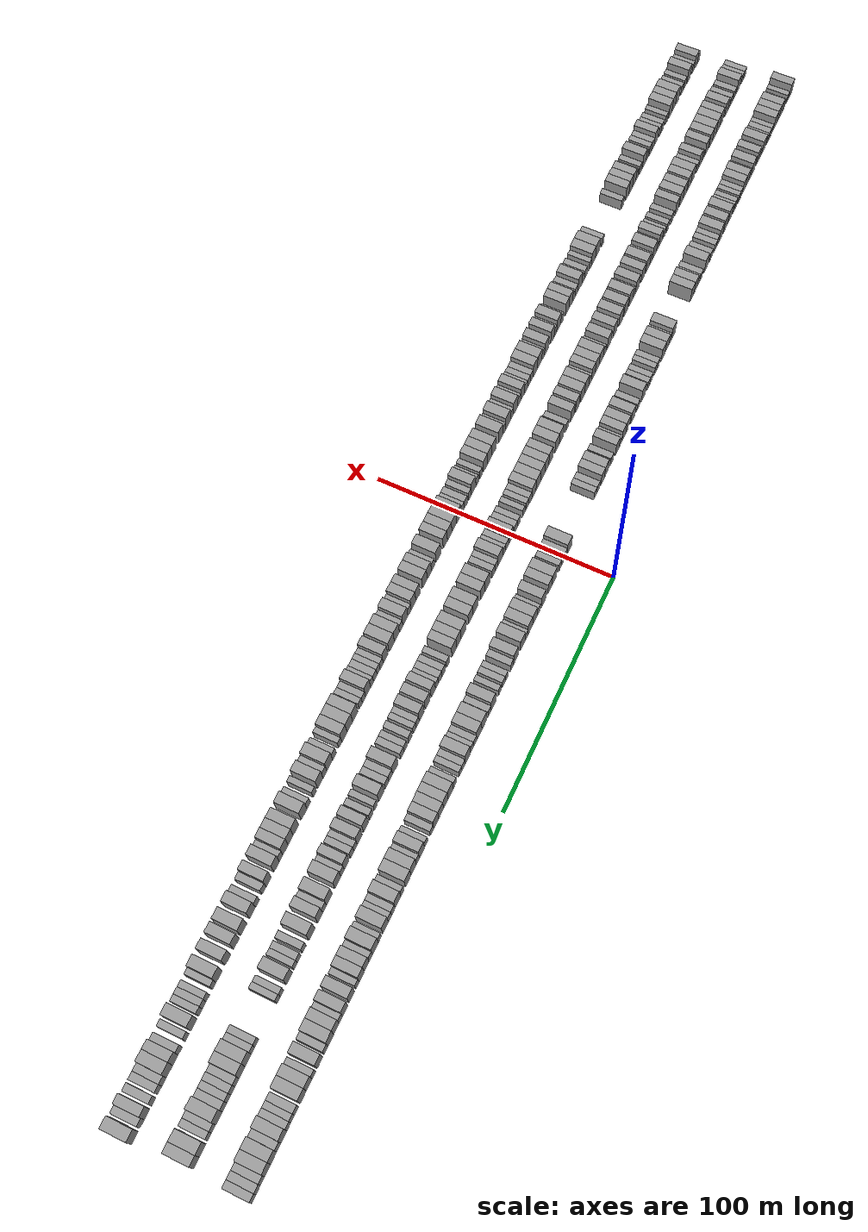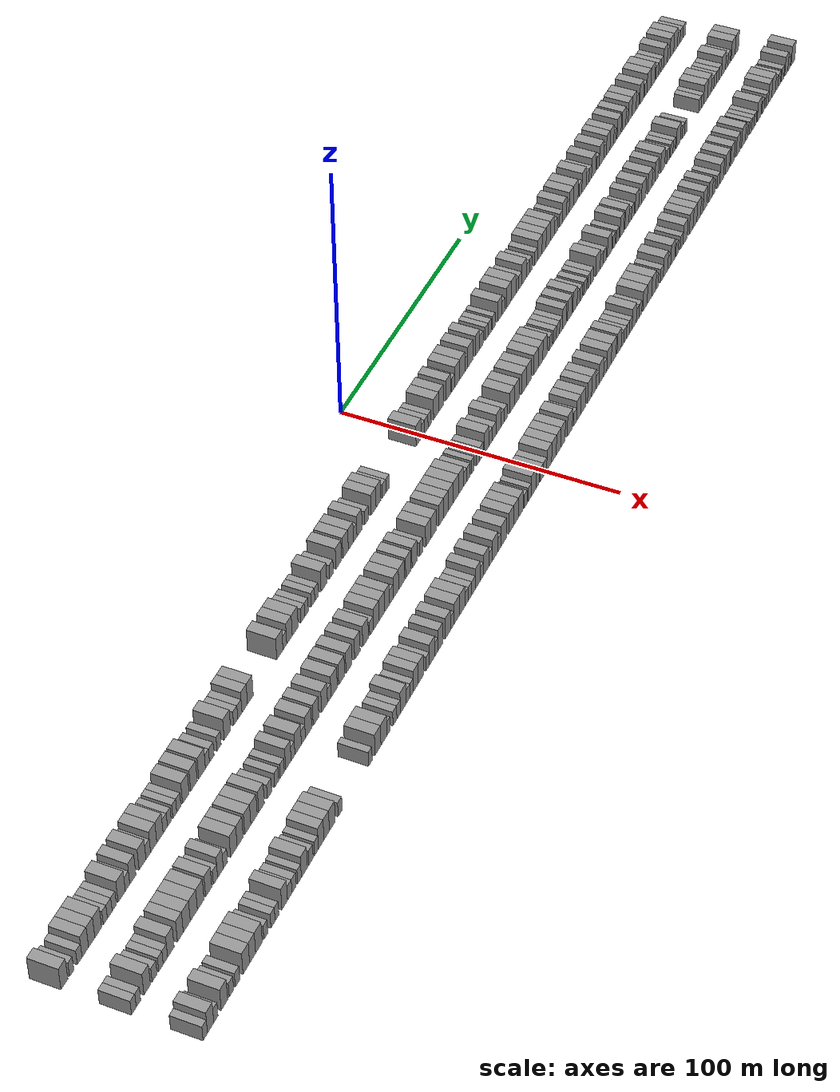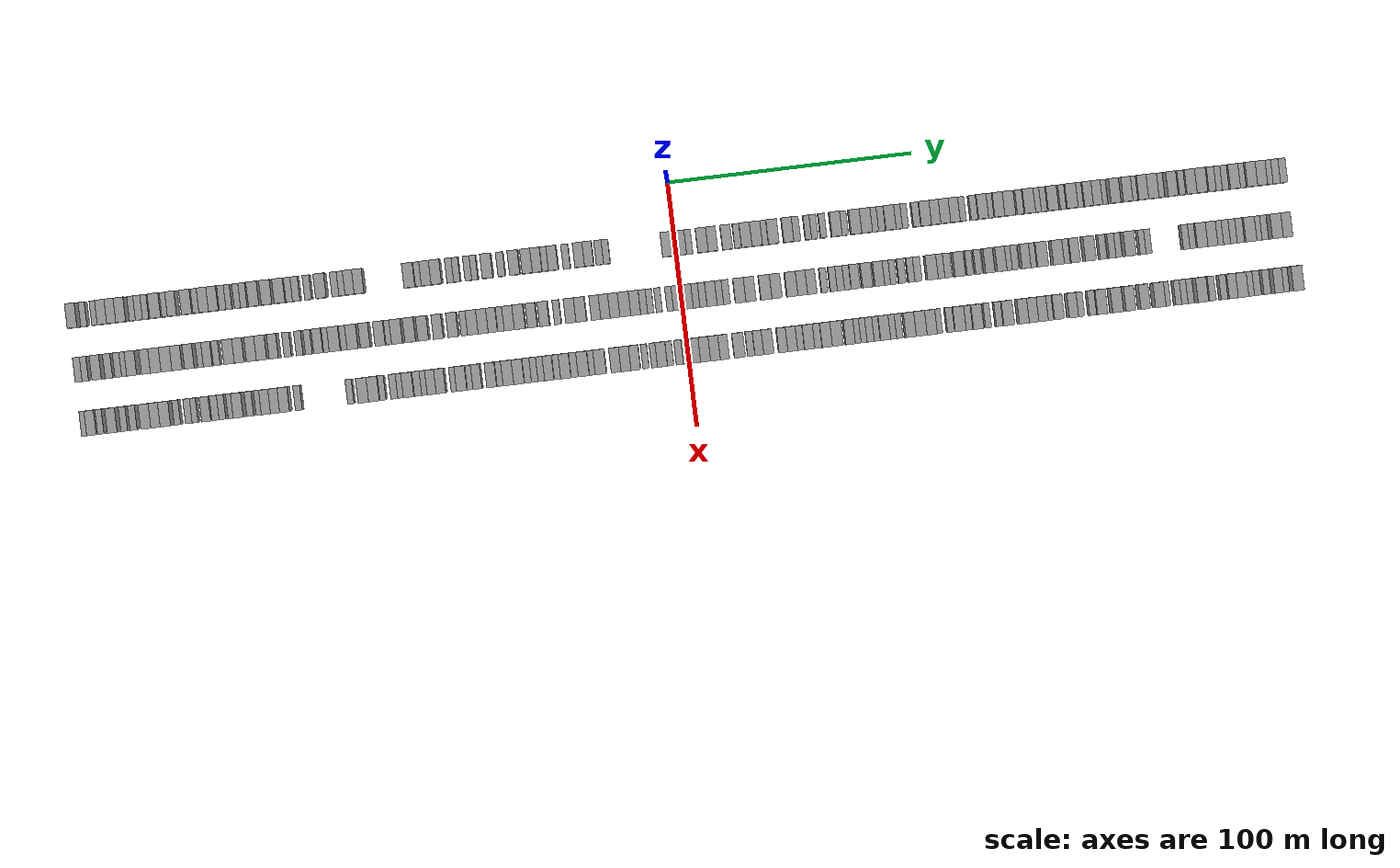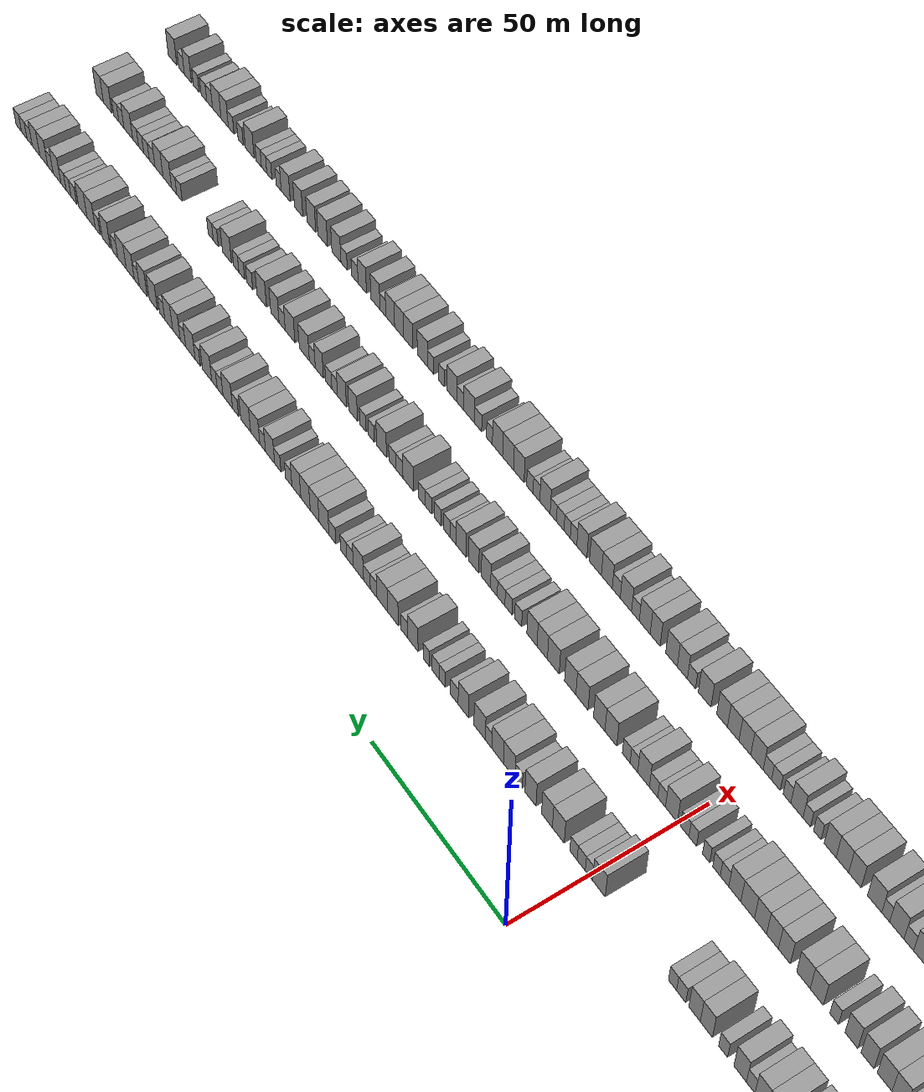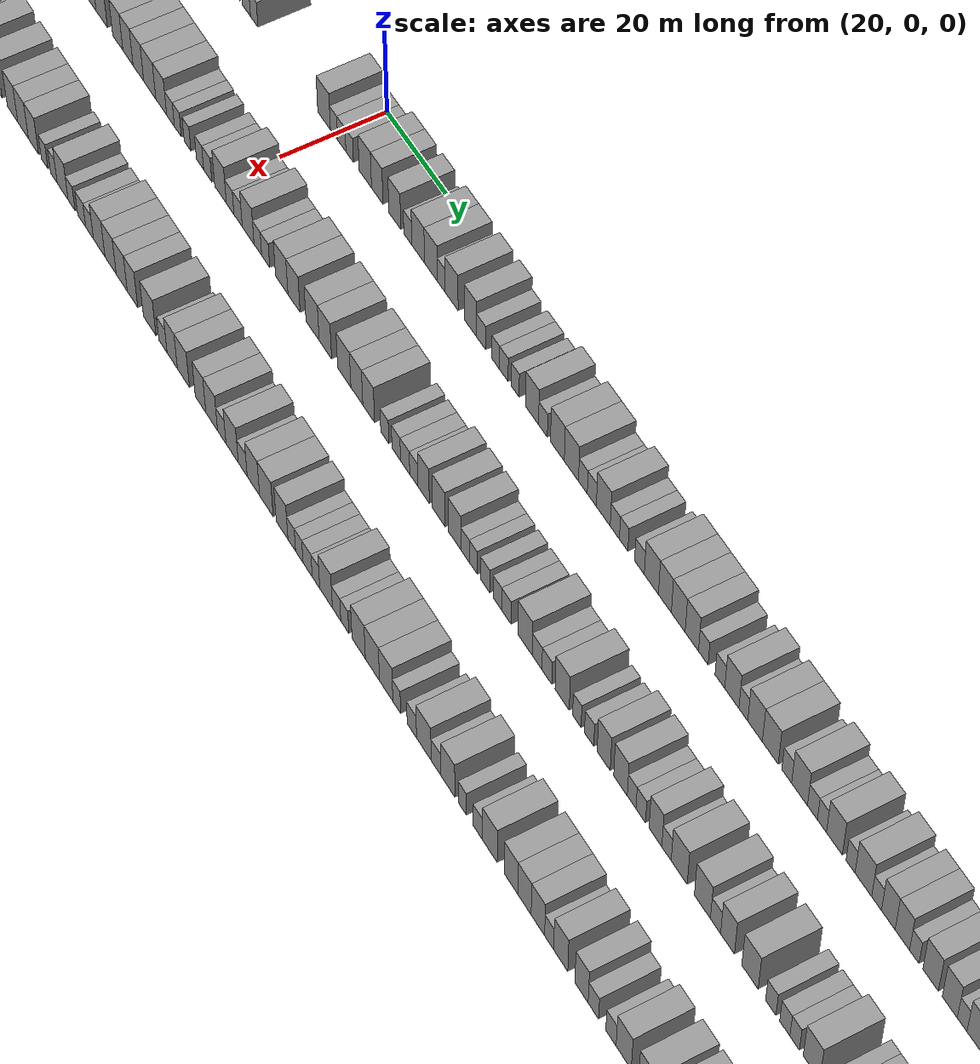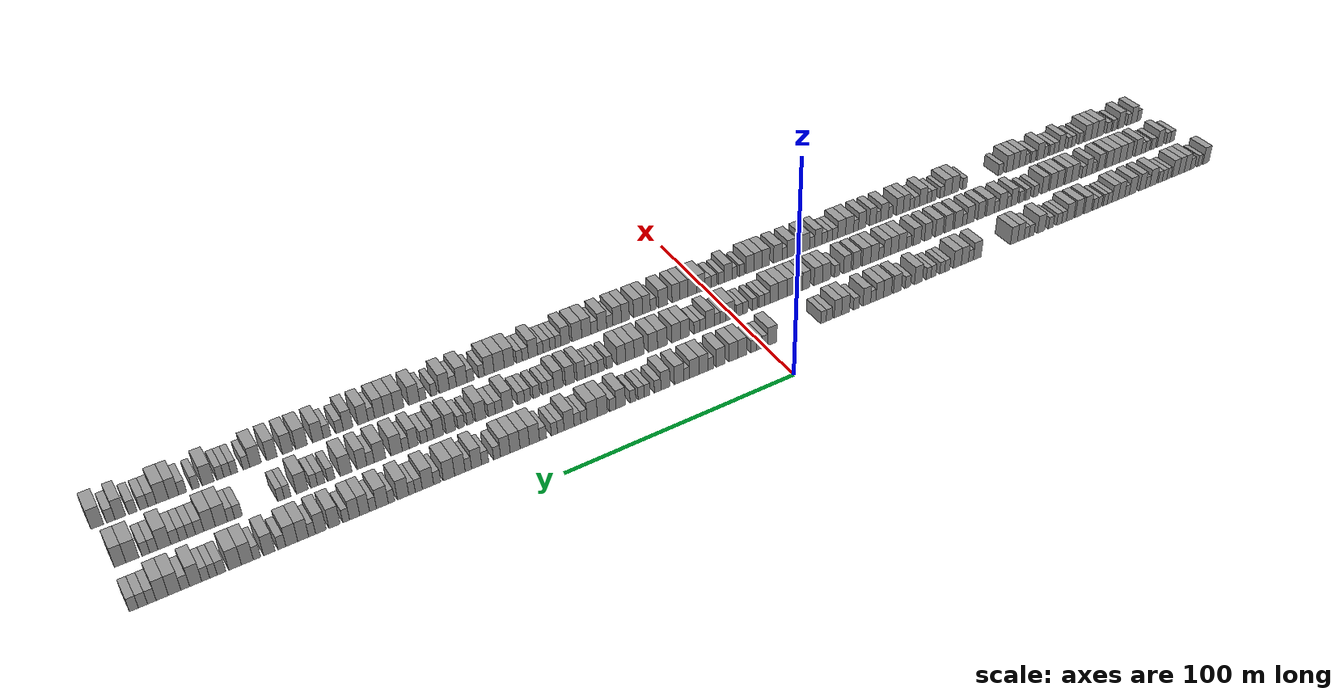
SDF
<sdf version="1.6">
 <world name="default">
  <scene>
   <sky><clouds><speed>12</speed></clouds></sky>
   <ambient>0.4 0.4 0.4 1</ambient>
   <background>0.7 0.7 0.7 1</background>
   <shadows>1</shadows>
  </scene>
  <gravity>0 0 -9.8066</gravity>
  <magnetic_field>6e-06 2.3e-05 -4.2e-05</magnetic_field>
  <physics default="0" name="default_physics" type="ode">
   <ode>
    <solver>
     <type>quick</type>
     <iters>10</iters>
     <sor>1.0</sor>
     <use_dynamic_moi_rescaling>0</use_dynamic_moi_rescaling>
    </solver>
    <constraints>
     <cfm>0</cfm>
     <erp>0.2</erp>
     <contact_max_correcting_vel>100</contact_max_correcting_vel>
     <contact_surface_layer>0.001</contact_surface_layer>
    </constraints>
   </ode>
   <max_step_size>0.004</max_step_size>
   <real_time_factor>1</real_time_factor>
   <real_time_update_rate>250</real_time_update_rate>
  </physics>
  <light name="sun" type="directional">
   <pose>0 0 10 0 0 0</pose>
   <diffuse>0.8 0.8 0.8 1</diffuse>
   <specular>0.2 0.2 0.2 1</specular>
   <attenuation>
    <range>1000</range>
    <constant>0.9</constant>
    <linear>0.01</linear>
    <quadratic>0.001</quadratic>
   </attenuation>
   <direction>-0.5 0.1 -0.9</direction>
  </light>
  <model name="building_1">
   <static>1</static>
   <pose>25.0000 -246.0256 0 0.000000 0.000000 0.000000</pose>
   <link name="link">
    <pose>0 0 4.50 0 0 0</pose>
    <collision name="collision"><geometry><box><size>10.0000 3.9487 9.0000</size></box></geometry></collision>
    <visual name="visual">
     <cast_shadows>0</cast_shadows>
     <geometry><box><size>10.0000 3.9487 9.0000</size></box></geometry>
     <material>
      <script>
       <uri>model://grey_wall/materials/scripts</uri>
       <uri>model://grey_wall/materials/textures</uri>
       <name>vrc/grey_wall</name>
      </script>
     </material>
    </visual>
   </link>
  </model>
  <model name="building_2">
   <static>1</static>
   <pose>25.0000 -241.8114 0 0.000000 0.000000 0.000000</pose>
   <link name="link">
    <pose>0 0 3.00 0 0 0</pose>
    <collision name="collision"><geometry><box><size>10.0000 2.4798 6.0000</size></box></geometry></collision>
    <visual name="visual">
     <cast_shadows>0</cast_shadows>
     <geometry><box><size>10.0000 2.4798 6.0000</size></box></geometry>
     <material>
      <script>
       <uri>model://grey_wall/materials/scripts</uri>
       <uri>model://grey_wall/materials/textures</uri>
       <name>vrc/grey_wall</name>
      </script>
     </material>
    </visual>
   </link>
  </model>
  <model name="building_3">
   <static>1</static>
   <pose>25.0000 -237.1694 0 0.000000 0.000000 0.000000</pose>
   <link name="link">
    <pose>0 0 3.00 0 0 0</pose>
    <collision name="collision"><geometry><box><size>10.0000 2.8042 6.0000</size></box></geometry></collision>
    <visual name="visual">
     <cast_shadows>0</cast_shadows>
     <geometry><box><size>10.0000 2.8042 6.0000</size></box></geometry>
     <material>
      <script>
       <uri>model://grey_wall/materials/scripts</uri>
       <uri>model://grey_wall/materials/textures</uri>
       <name>vrc/grey_wall</name>
      </script>
     </material>
    </visual>
   </link>
  </model>
  <model name="building_4">
   <static>1</static>
   <pose>25.0000 -233.8526 0 0.000000 0.000000 0.000000</pose>
   <link name="link">
    <pose>0 0 4.50 0 0 0</pose>
    <collision name="collision"><geometry><box><size>10.0000 3.8294 9.0000</size></box></geometry></collision>
    <visual name="visual">
     <cast_shadows>0</cast_shadows>
     <geometry><box><size>10.0000 3.8294 9.0000</size></box></geometry>
     <material>
      <script>
       <uri>model://grey_wall/materials/scripts</uri>
       <uri>model://grey_wall/materials/textures</uri>
       <name>vrc/grey_wall</name>
      </script>
     </material>
    </visual>
   </link>
  </model>
  <model name="building_5">
   <static>1</static>
   <pose>25.0000 -230.0821 0 0.000000 0.000000 0.000000</pose>
   <link name="link">
    <pose>0 0 4.50 0 0 0</pose>
    <collision name="collision"><geometry><box><size>10.0000 3.7115 9.0000</size></box></geometry></collision>
    <visual name="visual">
     <cast_shadows>0</cast_shadows>
     <geometry><box><size>10.0000 3.7115 9.0000</size></box></geometry>
     <material>
      <script>
       <uri>model://grey_wall/materials/scripts</uri>
       <uri>model://grey_wall/materials/textures</uri>
       <name>vrc/grey_wall</name>
      </script>
     </material>
    </visual>
   </link>
  </model>
  <model name="building_6">
   <static>1</static>
   <pose>25.0000 -226.2133 0 0.000000 0.000000 0.000000</pose>
   <link name="link">
    <pose>0 0 4.50 0 0 0</pose>
    <collision name="collision"><geometry><box><size>10.0000 4.0262 9.0000</size></box></geometry></collision>
    <visual name="visual">
     <cast_shadows>0</cast_shadows>
     <geometry><box><size>10.0000 4.0262 9.0000</size></box></geometry>
     <material>
      <script>
       <uri>model://grey_wall/materials/scripts</uri>
       <uri>model://grey_wall/materials/textures</uri>
       <name>vrc/grey_wall</name>
      </script>
     </material>
    </visual>
   </link>
  </model>
  <model name="building_7">
   <static>1</static>
   <pose>25.0000 -221.9935 0 0.000000 0.000000 0.000000</pose>
   <link name="link">
    <pose>0 0 3.00 0 0 0</pose>
    <collision name="collision"><geometry><box><size>10.0000 2.4132 6.0000</size></box></geometry></collision>
    <visual name="visual">
     <cast_shadows>0</cast_shadows>
     <geometry><box><size>10.0000 2.4132 6.0000</size></box></geometry>
     <material>
      <script>
       <uri>model://grey_wall/materials/scripts</uri>
       <uri>model://grey_wall/materials/textures</uri>
       <name>vrc/grey_wall</name>
      </script>
     </material>
    </visual>
   </link>
  </model>
  <model name="building_8">
   <static>1</static>
   <pose>25.0000 -219.3437 0 0.000000 0.000000 0.000000</pose>
   <link name="link">
    <pose>0 0 3.00 0 0 0</pose>
    <collision name="collision"><geometry><box><size>10.0000 2.8865 6.0000</size></box></geometry></collision>
    <visual name="visual">
     <cast_shadows>0</cast_shadows>
     <geometry><box><size>10.0000 2.8865 6.0000</size></box></geometry>
     <material>
      <script>
       <uri>model://grey_wall/materials/scripts</uri>
       <uri>model://grey_wall/materials/textures</uri>
       <name>vrc/grey_wall</name>
      </script>
     </material>
    </visual>
   </link>
  </model>
  <model name="building_9">
   <static>1</static>
   <pose>25.0000 -216.6256 0 0.000000 0.000000 0.000000</pose>
   <link name="link">
    <pose>0 0 3.00 0 0 0</pose>
    <collision name="collision"><geometry><box><size>10.0000 2.5496 6.0000</size></box></geometry></collision>
    <visual name="visual">
     <cast_shadows>0</cast_shadows>
     <geometry><box><size>10.0000 2.5496 6.0000</size></box></geometry>
     <material>
      <script>
       <uri>model://grey_wall/materials/scripts</uri>
       <uri>model://grey_wall/materials/textures</uri>
       <name>vrc/grey_wall</name>
      </script>
     </material>
    </visual>
   </link>
  </model>
  <model name="building_10">
   <static>1</static>
   <pose>25.0000 -212.1598 0 0.000000 0.000000 0.000000</pose>
   <link name="link">
    <pose>0 0 4.50 0 0 0</pose>
    <collision name="collision"><geometry><box><size>10.0000 4.3820 9.0000</size></box></geometry></collision>
    <visual name="visual">
     <cast_shadows>0</cast_shadows>
     <geometry><box><size>10.0000 4.3820 9.0000</size></box></geometry>
     <material>
      <script>
       <uri>model://grey_wall/materials/scripts</uri>
       <uri>model://grey_wall/materials/textures</uri>
       <name>vrc/grey_wall</name>
      </script>
     </material>
    </visual>
   </link>
  </model>
  <model name="building_11">
   <static>1</static>
   <pose>25.0000 -208.6031 0 0.000000 0.000000 0.000000</pose>
   <link name="link">
    <pose>0 0 3.00 0 0 0</pose>
    <collision name="collision"><geometry><box><size>10.0000 2.7313 6.0000</size></box></geometry></collision>
    <visual name="visual">
     <cast_shadows>0</cast_shadows>
     <geometry><box><size>10.0000 2.7313 6.0000</size></box></geometry>
     <material>
      <script>
       <uri>model://grey_wall/materials/scripts</uri>
       <uri>model://grey_wall/materials/textures</uri>
       <name>vrc/grey_wall</name>
      </script>
     </material>
    </visual>
   </link>
  </model>
  <model name="building_12">
   <static>1</static>
   <pose>25.0000 -205.3724 0 0.000000 0.000000 0.000000</pose>
   <link name="link">
    <pose>0 0 4.50 0 0 0</pose>
    <collision name="collision"><geometry><box><size>10.0000 3.7300 9.0000</size></box></geometry></collision>
    <visual name="visual">
     <cast_shadows>0</cast_shadows>
     <geometry><box><size>10.0000 3.7300 9.0000</size></box></geometry>
     <material>
      <script>
       <uri>model://grey_wall/materials/scripts</uri>
       <uri>model://grey_wall/materials/textures</uri>
       <name>vrc/grey_wall</name>
      </script>
     </material>
    </visual>
   </link>
  </model>
  <model name="building_13">
   <static>1</static>
   <pose>25.0000 -199.4030 0 0.000000 0.000000 0.000000</pose>
   <link name="link">
    <pose>0 0 4.50 0 0 0</pose>
    <collision name="collision"><geometry><box><size>10.0000 4.2089 9.0000</size></box></geometry></collision>
    <visual name="visual">
     <cast_shadows>0</cast_shadows>
     <geometry><box><size>10.0000 4.2089 9.0000</size></box></geometry>
     <material>
      <script>
       <uri>model://grey_wall/materials/scripts</uri>
       <uri>model://grey_wall/materials/textures</uri>
       <name>vrc/grey_wall</name>
      </script>
     </material>
    </visual>
   </link>
  </model>
  <model name="building_14">
   <static>1</static>
   <pose>25.0000 -195.8480 0 0.000000 0.000000 0.000000</pose>
   <link name="link">
    <pose>0 0 3.00 0 0 0</pose>
    <collision name="collision"><geometry><box><size>10.0000 2.9011 6.0000</size></box></geometry></collision>
    <visual name="visual">
     <cast_shadows>0</cast_shadows>
     <geometry><box><size>10.0000 2.9011 6.0000</size></box></geometry>
     <material>
      <script>
       <uri>model://grey_wall/materials/scripts</uri>
       <uri>model://grey_wall/materials/textures</uri>
       <name>vrc/grey_wall</name>
      </script>
     </material>
    </visual>
   </link>
  </model>
  <model name="building_15">
   <static>1</static>
   <pose>25.0000 -192.4488 0 0.000000 0.000000 0.000000</pose>
   <link name="link">
    <pose>0 0 4.50 0 0 0</pose>
    <collision name="collision"><geometry><box><size>10.0000 3.8974 9.0000</size></box></geometry></collision>
    <visual name="visual">
     <cast_shadows>0</cast_shadows>
     <geometry><box><size>10.0000 3.8974 9.0000</size></box></geometry>
     <material>
      <script>
       <uri>model://grey_wall/materials/scripts</uri>
       <uri>model://grey_wall/materials/textures</uri>
       <name>vrc/grey_wall</name>
      </script>
     </material>
    </visual>
   </link>
  </model>
  <model name="building_16">
   <static>1</static>
   <pose>25.0000 -188.5195 0 0.000000 0.000000 0.000000</pose>
   <link name="link">
    <pose>0 0 4.50 0 0 0</pose>
    <collision name="collision"><geometry><box><size>10.0000 3.9612 9.0000</size></box></geometry></collision>
    <visual name="visual">
     <cast_shadows>0</cast_shadows>
     <geometry><box><size>10.0000 3.9612 9.0000</size></box></geometry>
     <material>
      <script>
       <uri>model://grey_wall/materials/scripts</uri>
       <uri>model://grey_wall/materials/textures</uri>
       <name>vrc/grey_wall</name>
      </script>
     </material>
    </visual>
   </link>
  </model>
  <model name="building_17">
   <static>1</static>
   <pose>25.0000 -185.1757 0 0.000000 0.000000 0.000000</pose>
   <link name="link">
    <pose>0 0 3.00 0 0 0</pose>
    <collision name="collision"><geometry><box><size>10.0000 2.7264 6.0000</size></box></geometry></collision>
    <visual name="visual">
     <cast_shadows>0</cast_shadows>
     <geometry><box><size>10.0000 2.7264 6.0000</size></box></geometry>
     <material>
      <script>
       <uri>model://grey_wall/materials/scripts</uri>
       <uri>model://grey_wall/materials/textures</uri>
       <name>vrc/grey_wall</name>
      </script>
     </material>
    </visual>
   </link>
  </model>
  <model name="building_18">
   <static>1</static>
   <pose>25.0000 -182.6045 0 0.000000 0.000000 0.000000</pose>
   <link name="link">
    <pose>0 0 3.00 0 0 0</pose>
    <collision name="collision"><geometry><box><size>10.0000 2.4160 6.0000</size></box></geometry></collision>
    <visual name="visual">
     <cast_shadows>0</cast_shadows>
     <geometry><box><size>10.0000 2.4160 6.0000</size></box></geometry>
     <material>
      <script>
       <uri>model://grey_wall/materials/scripts</uri>
       <uri>model://grey_wall/materials/textures</uri>
       <name>vrc/grey_wall</name>
      </script>
     </material>
    </visual>
   </link>
  </model>
  <model name="building_19">
   <static>1</static>
   <pose>25.0000 -179.1431 0 0.000000 0.000000 0.000000</pose>
   <link name="link">
    <pose>0 0 3.00 0 0 0</pose>
    <collision name="collision"><geometry><box><size>10.0000 2.5067 6.0000</size></box></geometry></collision>
    <visual name="visual">
     <cast_shadows>0</cast_shadows>
     <geometry><box><size>10.0000 2.5067 6.0000</size></box></geometry>
     <material>
      <script>
       <uri>model://grey_wall/materials/scripts</uri>
       <uri>model://grey_wall/materials/textures</uri>
       <name>vrc/grey_wall</name>
      </script>
     </material>
    </visual>
   </link>
  </model>
  <model name="building_20">
   <static>1</static>
   <pose>25.0000 -176.5462 0 0.000000 0.000000 0.000000</pose>
   <link name="link">
    <pose>0 0 3.00 0 0 0</pose>
    <collision name="collision"><geometry><box><size>10.0000 2.6870 6.0000</size></box></geometry></collision>
    <visual name="visual">
     <cast_shadows>0</cast_shadows>
     <geometry><box><size>10.0000 2.6870 6.0000</size></box></geometry>
     <material>
      <script>
       <uri>model://grey_wall/materials/scripts</uri>
       <uri>model://grey_wall/materials/textures</uri>
       <name>vrc/grey_wall</name>
      </script>
     </material>
    </visual>
   </link>
  </model>
  <model name="building_21">
   <static>1</static>
   <pose>25.0000 -172.0759 0 0.000000 0.000000 0.000000</pose>
   <link name="link">
    <pose>0 0 4.50 0 0 0</pose>
    <collision name="collision"><geometry><box><size>10.0000 4.2536 9.0000</size></box></geometry></collision>
    <visual name="visual">
     <cast_shadows>0</cast_shadows>
     <geometry><box><size>10.0000 4.2536 9.0000</size></box></geometry>
     <material>
      <script>
       <uri>model://grey_wall/materials/scripts</uri>
       <uri>model://grey_wall/materials/textures</uri>
       <name>vrc/grey_wall</name>
      </script>
     </material>
    </visual>
   </link>
  </model>
  <model name="building_22">
   <static>1</static>
   <pose>25.0000 -166.8171 0 0.000000 0.000000 0.000000</pose>
   <link name="link">
    <pose>0 0 4.50 0 0 0</pose>
    <collision name="collision"><geometry><box><size>10.0000 4.2640 9.0000</size></box></geometry></collision>
    <visual name="visual">
     <cast_shadows>0</cast_shadows>
     <geometry><box><size>10.0000 4.2640 9.0000</size></box></geometry>
     <material>
      <script>
       <uri>model://grey_wall/materials/scripts</uri>
       <uri>model://grey_wall/materials/textures</uri>
       <name>vrc/grey_wall</name>
      </script>
     </material>
    </visual>
   </link>
  </model>
  <model name="building_23">
   <static>1</static>
   <pose>25.0000 -161.5045 0 0.000000 0.000000 0.000000</pose>
   <link name="link">
    <pose>0 0 4.50 0 0 0</pose>
    <collision name="collision"><geometry><box><size>10.0000 4.3612 9.0000</size></box></geometry></collision>
    <visual name="visual">
     <cast_shadows>0</cast_shadows>
     <geometry><box><size>10.0000 4.3612 9.0000</size></box></geometry>
     <material>
      <script>
       <uri>model://grey_wall/materials/scripts</uri>
       <uri>model://grey_wall/materials/textures</uri>
       <name>vrc/grey_wall</name>
      </script>
     </material>
    </visual>
   </link>
  </model>
  <model name="building_24">
   <static>1</static>
   <pose>25.0000 -157.9788 0 0.000000 0.000000 0.000000</pose>
   <link name="link">
    <pose>0 0 3.00 0 0 0</pose>
    <collision name="collision"><geometry><box><size>10.0000 2.6903 6.0000</size></box></geometry></collision>
    <visual name="visual">
     <cast_shadows>0</cast_shadows>
     <geometry><box><size>10.0000 2.6903 6.0000</size></box></geometry>
     <material>
      <script>
       <uri>model://grey_wall/materials/scripts</uri>
       <uri>model://grey_wall/materials/textures</uri>
       <name>vrc/grey_wall</name>
      </script>
     </material>
    </visual>
   </link>
  </model>
  <model name="building_25">
   <static>1</static>
   <pose>25.0000 -155.1481 0 0.000000 0.000000 0.000000</pose>
   <link name="link">
    <pose>0 0 3.00 0 0 0</pose>
    <collision name="collision"><geometry><box><size>10.0000 2.9709 6.0000</size></box></geometry></collision>
    <visual name="visual">
     <cast_shadows>0</cast_shadows>
     <geometry><box><size>10.0000 2.9709 6.0000</size></box></geometry>
     <material>
      <script>
       <uri>model://grey_wall/materials/scripts</uri>
       <uri>model://grey_wall/materials/textures</uri>
       <name>vrc/grey_wall</name>
      </script>
     </material>
    </visual>
   </link>
  </model>
  <model name="building_26">
   <static>1</static>
   <pose>25.0000 -150.2772 0 0.000000 0.000000 0.000000</pose>
   <link name="link">
    <pose>0 0 3.00 0 0 0</pose>
    <collision name="collision"><geometry><box><size>10.0000 2.7709 6.0000</size></box></geometry></collision>
    <visual name="visual">
     <cast_shadows>0</cast_shadows>
     <geometry><box><size>10.0000 2.7709 6.0000</size></box></geometry>
     <material>
      <script>
       <uri>model://grey_wall/materials/scripts</uri>
       <uri>model://grey_wall/materials/textures</uri>
       <name>vrc/grey_wall</name>
      </script>
     </material>
    </visual>
   </link>
  </model>
  <model name="building_27">
   <static>1</static>
   <pose>25.0000 -144.7286 0 0.000000 0.000000 0.000000</pose>
   <link name="link">
    <pose>0 0 4.50 0 0 0</pose>
    <collision name="collision"><geometry><box><size>10.0000 4.3263 9.0000</size></box></geometry></collision>
    <visual name="visual">
     <cast_shadows>0</cast_shadows>
     <geometry><box><size>10.0000 4.3263 9.0000</size></box></geometry>
     <material>
      <script>
       <uri>model://grey_wall/materials/scripts</uri>
       <uri>model://grey_wall/materials/textures</uri>
       <name>vrc/grey_wall</name>
      </script>
     </material>
    </visual>
   </link>
  </model>
  <model name="building_28">
   <static>1</static>
   <pose>25.0000 -139.1479 0 0.000000 0.000000 0.000000</pose>
   <link name="link">
    <pose>0 0 3.00 0 0 0</pose>
    <collision name="collision"><geometry><box><size>10.0000 2.8351 6.0000</size></box></geometry></collision>
    <visual name="visual">
     <cast_shadows>0</cast_shadows>
     <geometry><box><size>10.0000 2.8351 6.0000</size></box></geometry>
     <material>
      <script>
       <uri>model://grey_wall/materials/scripts</uri>
       <uri>model://grey_wall/materials/textures</uri>
       <name>vrc/grey_wall</name>
      </script>
     </material>
    </visual>
   </link>
  </model>
  <model name="building_29">
   <static>1</static>
   <pose>25.0000 -136.3206 0 0.000000 0.000000 0.000000</pose>
   <link name="link">
    <pose>0 0 3.00 0 0 0</pose>
    <collision name="collision"><geometry><box><size>10.0000 2.8196 6.0000</size></box></geometry></collision>
    <visual name="visual">
     <cast_shadows>0</cast_shadows>
     <geometry><box><size>10.0000 2.8196 6.0000</size></box></geometry>
     <material>
      <script>
       <uri>model://grey_wall/materials/scripts</uri>
       <uri>model://grey_wall/materials/textures</uri>
       <name>vrc/grey_wall</name>
      </script>
     </material>
    </visual>
   </link>
  </model>
  <model name="building_30">
   <static>1</static>
   <pose>25.0000 -133.0319 0 0.000000 0.000000 0.000000</pose>
   <link name="link">
    <pose>0 0 4.50 0 0 0</pose>
    <collision name="collision"><geometry><box><size>10.0000 3.7577 9.0000</size></box></geometry></collision>
    <visual name="visual">
     <cast_shadows>0</cast_shadows>
     <geometry><box><size>10.0000 3.7577 9.0000</size></box></geometry>
     <material>
      <script>
       <uri>model://grey_wall/materials/scripts</uri>
       <uri>model://grey_wall/materials/textures</uri>
       <name>vrc/grey_wall</name>
      </script>
     </material>
    </visual>
   </link>
  </model>
  <model name="building_31">
   <static>1</static>
   <pose>25.0000 -129.1753 0 0.000000 0.000000 0.000000</pose>
   <link name="link">
    <pose>0 0 4.50 0 0 0</pose>
    <collision name="collision"><geometry><box><size>10.0000 3.9555 9.0000</size></box></geometry></collision>
    <visual name="visual">
     <cast_shadows>0</cast_shadows>
     <geometry><box><size>10.0000 3.9555 9.0000</size></box></geometry>
     <material>
      <script>
       <uri>model://grey_wall/materials/scripts</uri>
       <uri>model://grey_wall/materials/textures</uri>
       <name>vrc/grey_wall</name>
      </script>
     </material>
    </visual>
   </link>
  </model>
  <model name="building_32">
   <static>1</static>
   <pose>25.0000 -108.6616 0 0.000000 0.000000 0.000000</pose>
   <link name="link">
    <pose>0 0 4.50 0 0 0</pose>
    <collision name="collision"><geometry><box><size>10.0000 4.3573 9.0000</size></box></geometry></collision>
    <visual name="visual">
     <cast_shadows>0</cast_shadows>
     <geometry><box><size>10.0000 4.3573 9.0000</size></box></geometry>
     <material>
      <script>
       <uri>model://grey_wall/materials/scripts</uri>
       <uri>model://grey_wall/materials/textures</uri>
       <name>vrc/grey_wall</name>
      </script>
     </material>
    </visual>
   </link>
  </model>
  <model name="building_33">
   <static>1</static>
   <pose>25.0000 -105.1436 0 0.000000 0.000000 0.000000</pose>
   <link name="link">
    <pose>0 0 3.00 0 0 0</pose>
    <collision name="collision"><geometry><box><size>10.0000 2.6787 6.0000</size></box></geometry></collision>
    <visual name="visual">
     <cast_shadows>0</cast_shadows>
     <geometry><box><size>10.0000 2.6787 6.0000</size></box></geometry>
     <material>
      <script>
       <uri>model://grey_wall/materials/scripts</uri>
       <uri>model://grey_wall/materials/textures</uri>
       <name>vrc/grey_wall</name>
      </script>
     </material>
    </visual>
   </link>
  </model>
  <model name="building_34">
   <static>1</static>
   <pose>25.0000 -101.8308 0 0.000000 0.000000 0.000000</pose>
   <link name="link">
    <pose>0 0 4.50 0 0 0</pose>
    <collision name="collision"><geometry><box><size>10.0000 3.9469 9.0000</size></box></geometry></collision>
    <visual name="visual">
     <cast_shadows>0</cast_shadows>
     <geometry><box><size>10.0000 3.9469 9.0000</size></box></geometry>
     <material>
      <script>
       <uri>model://grey_wall/materials/scripts</uri>
       <uri>model://grey_wall/materials/textures</uri>
       <name>vrc/grey_wall</name>
      </script>
     </material>
    </visual>
   </link>
  </model>
  <model name="building_35">
   <static>1</static>
   <pose>25.0000 -97.7363 0 0.000000 0.000000 0.000000</pose>
   <link name="link">
    <pose>0 0 4.50 0 0 0</pose>
    <collision name="collision"><geometry><box><size>10.0000 4.2420 9.0000</size></box></geometry></collision>
    <visual name="visual">
     <cast_shadows>0</cast_shadows>
     <geometry><box><size>10.0000 4.2420 9.0000</size></box></geometry>
     <material>
      <script>
       <uri>model://grey_wall/materials/scripts</uri>
       <uri>model://grey_wall/materials/textures</uri>
       <name>vrc/grey_wall</name>
      </script>
     </material>
    </visual>
   </link>
  </model>
  <model name="building_36">
   <static>1</static>
   <pose>25.0000 -92.2385 0 0.000000 0.000000 0.000000</pose>
   <link name="link">
    <pose>0 0 3.00 0 0 0</pose>
    <collision name="collision"><geometry><box><size>10.0000 2.7537 6.0000</size></box></geometry></collision>
    <visual name="visual">
     <cast_shadows>0</cast_shadows>
     <geometry><box><size>10.0000 2.7537 6.0000</size></box></geometry>
     <material>
      <script>
       <uri>model://grey_wall/materials/scripts</uri>
       <uri>model://grey_wall/materials/textures</uri>
       <name>vrc/grey_wall</name>
      </script>
     </material>
    </visual>
   </link>
  </model>
  <model name="building_37">
   <static>1</static>
   <pose>25.0000 -89.5527 0 0.000000 0.000000 0.000000</pose>
   <link name="link">
    <pose>0 0 3.00 0 0 0</pose>
    <collision name="collision"><geometry><box><size>10.0000 2.6178 6.0000</size></box></geometry></collision>
    <visual name="visual">
     <cast_shadows>0</cast_shadows>
     <geometry><box><size>10.0000 2.6178 6.0000</size></box></geometry>
     <material>
      <script>
       <uri>model://grey_wall/materials/scripts</uri>
       <uri>model://grey_wall/materials/textures</uri>
       <name>vrc/grey_wall</name>
      </script>
     </material>
    </visual>
   </link>
  </model>
  <model name="building_38">
   <static>1</static>
   <pose>25.0000 -84.8912 0 0.000000 0.000000 0.000000</pose>
   <link name="link">
    <pose>0 0 3.00 0 0 0</pose>
    <collision name="collision"><geometry><box><size>10.0000 2.7052 6.0000</size></box></geometry></collision>
    <visual name="visual">
     <cast_shadows>0</cast_shadows>
     <geometry><box><size>10.0000 2.7052 6.0000</size></box></geometry>
     <material>
      <script>
       <uri>model://grey_wall/materials/scripts</uri>
       <uri>model://grey_wall/materials/textures</uri>
       <name>vrc/grey_wall</name>
      </script>
     </material>
    </visual>
   </link>
  </model>
  <model name="building_39">
   <static>1</static>
   <pose>25.0000 -82.2758 0 0.000000 0.000000 0.000000</pose>
   <link name="link">
    <pose>0 0 3.00 0 0 0</pose>
    <collision name="collision"><geometry><box><size>10.0000 2.5258 6.0000</size></box></geometry></collision>
    <visual name="visual">
     <cast_shadows>0</cast_shadows>
     <geometry><box><size>10.0000 2.5258 6.0000</size></box></geometry>
     <material>
      <script>
       <uri>model://grey_wall/materials/scripts</uri>
       <uri>model://grey_wall/materials/textures</uri>
       <name>vrc/grey_wall</name>
      </script>
     </material>
    </visual>
   </link>
  </model>
  <model name="building_40">
   <static>1</static>
   <pose>25.0000 -76.8914 0 0.000000 0.000000 0.000000</pose>
   <link name="link">
    <pose>0 0 4.50 0 0 0</pose>
    <collision name="collision"><geometry><box><size>10.0000 4.2429 9.0000</size></box></geometry></collision>
    <visual name="visual">
     <cast_shadows>0</cast_shadows>
     <geometry><box><size>10.0000 4.2429 9.0000</size></box></geometry>
     <material>
      <script>
       <uri>model://grey_wall/materials/scripts</uri>
       <uri>model://grey_wall/materials/textures</uri>
       <name>vrc/grey_wall</name>
      </script>
     </material>
    </visual>
   </link>
  </model>
  <model name="building_41">
   <static>1</static>
   <pose>25.0000 -71.3309 0 0.000000 0.000000 0.000000</pose>
   <link name="link">
    <pose>0 0 3.00 0 0 0</pose>
    <collision name="collision"><geometry><box><size>10.0000 2.8782 6.0000</size></box></geometry></collision>
    <visual name="visual">
     <cast_shadows>0</cast_shadows>
     <geometry><box><size>10.0000 2.8782 6.0000</size></box></geometry>
     <material>
      <script>
       <uri>model://grey_wall/materials/scripts</uri>
       <uri>model://grey_wall/materials/textures</uri>
       <name>vrc/grey_wall</name>
      </script>
     </material>
    </visual>
   </link>
  </model>
  <model name="building_42">
   <static>1</static>
   <pose>25.0000 -65.8183 0 0.000000 0.000000 0.000000</pose>
   <link name="link">
    <pose>0 0 4.50 0 0 0</pose>
    <collision name="collision"><geometry><box><size>10.0000 4.1470 9.0000</size></box></geometry></collision>
    <visual name="visual">
     <cast_shadows>0</cast_shadows>
     <geometry><box><size>10.0000 4.1470 9.0000</size></box></geometry>
     <material>
      <script>
       <uri>model://grey_wall/materials/scripts</uri>
       <uri>model://grey_wall/materials/textures</uri>
       <name>vrc/grey_wall</name>
      </script>
     </material>
    </visual>
   </link>
  </model>
  <model name="building_43">
   <static>1</static>
   <pose>25.0000 -60.6888 0 0.000000 0.000000 0.000000</pose>
   <link name="link">
    <pose>0 0 4.50 0 0 0</pose>
    <collision name="collision"><geometry><box><size>10.0000 4.1120 9.0000</size></box></geometry></collision>
    <visual name="visual">
     <cast_shadows>0</cast_shadows>
     <geometry><box><size>10.0000 4.1120 9.0000</size></box></geometry>
     <material>
      <script>
       <uri>model://grey_wall/materials/scripts</uri>
       <uri>model://grey_wall/materials/textures</uri>
       <name>vrc/grey_wall</name>
      </script>
     </material>
    </visual>
   </link>
  </model>
  <model name="building_44">
   <static>1</static>
   <pose>25.0000 -56.6895 0 0.000000 0.000000 0.000000</pose>
   <link name="link">
    <pose>0 0 4.50 0 0 0</pose>
    <collision name="collision"><geometry><box><size>10.0000 3.8864 9.0000</size></box></geometry></collision>
    <visual name="visual">
     <cast_shadows>0</cast_shadows>
     <geometry><box><size>10.0000 3.8864 9.0000</size></box></geometry>
     <material>
      <script>
       <uri>model://grey_wall/materials/scripts</uri>
       <uri>model://grey_wall/materials/textures</uri>
       <name>vrc/grey_wall</name>
      </script>
     </material>
    </visual>
   </link>
  </model>
  <model name="building_45">
   <static>1</static>
   <pose>25.0000 -53.4133 0 0.000000 0.000000 0.000000</pose>
   <link name="link">
    <pose>0 0 3.00 0 0 0</pose>
    <collision name="collision"><geometry><box><size>10.0000 2.6660 6.0000</size></box></geometry></collision>
    <visual name="visual">
     <cast_shadows>0</cast_shadows>
     <geometry><box><size>10.0000 2.6660 6.0000</size></box></geometry>
     <material>
      <script>
       <uri>model://grey_wall/materials/scripts</uri>
       <uri>model://grey_wall/materials/textures</uri>
       <name>vrc/grey_wall</name>
      </script>
     </material>
    </visual>
   </link>
  </model>
  <model name="building_46">
   <static>1</static>
   <pose>25.0000 -50.1086 0 0.000000 0.000000 0.000000</pose>
   <link name="link">
    <pose>0 0 4.50 0 0 0</pose>
    <collision name="collision"><geometry><box><size>10.0000 3.9434 9.0000</size></box></geometry></collision>
    <visual name="visual">
     <cast_shadows>0</cast_shadows>
     <geometry><box><size>10.0000 3.9434 9.0000</size></box></geometry>
     <material>
      <script>
       <uri>model://grey_wall/materials/scripts</uri>
       <uri>model://grey_wall/materials/textures</uri>
       <name>vrc/grey_wall</name>
      </script>
     </material>
    </visual>
   </link>
  </model>
  <model name="building_47">
   <static>1</static>
   <pose>25.0000 -44.7140 0 0.000000 0.000000 0.000000</pose>
   <link name="link">
    <pose>0 0 3.00 0 0 0</pose>
    <collision name="collision"><geometry><box><size>10.0000 2.8458 6.0000</size></box></geometry></collision>
    <visual name="visual">
     <cast_shadows>0</cast_shadows>
     <geometry><box><size>10.0000 2.8458 6.0000</size></box></geometry>
     <material>
      <script>
       <uri>model://grey_wall/materials/scripts</uri>
       <uri>model://grey_wall/materials/textures</uri>
       <name>vrc/grey_wall</name>
      </script>
     </material>
    </visual>
   </link>
  </model>
  <model name="building_48">
   <static>1</static>
   <pose>25.0000 -39.3300 0 0.000000 0.000000 0.000000</pose>
   <link name="link">
    <pose>0 0 4.50 0 0 0</pose>
    <collision name="collision"><geometry><box><size>10.0000 3.9221 9.0000</size></box></geometry></collision>
    <visual name="visual">
     <cast_shadows>0</cast_shadows>
     <geometry><box><size>10.0000 3.9221 9.0000</size></box></geometry>
     <material>
      <script>
       <uri>model://grey_wall/materials/scripts</uri>
       <uri>model://grey_wall/materials/textures</uri>
       <name>vrc/grey_wall</name>
      </script>
     </material>
    </visual>
   </link>
  </model>
  <model name="building_49">
   <static>1</static>
   <pose>25.0000 -35.5136 0 0.000000 0.000000 0.000000</pose>
   <link name="link">
    <pose>0 0 4.50 0 0 0</pose>
    <collision name="collision"><geometry><box><size>10.0000 3.7106 9.0000</size></box></geometry></collision>
    <visual name="visual">
     <cast_shadows>0</cast_shadows>
     <geometry><box><size>10.0000 3.7106 9.0000</size></box></geometry>
     <material>
      <script>
       <uri>model://grey_wall/materials/scripts</uri>
       <uri>model://grey_wall/materials/textures</uri>
       <name>vrc/grey_wall</name>
      </script>
     </material>
    </visual>
   </link>
  </model>
  <model name="building_50">
   <static>1</static>
   <pose>25.0000 -31.1652 0 0.000000 0.000000 0.000000</pose>
   <link name="link">
    <pose>0 0 3.00 0 0 0</pose>
    <collision name="collision"><geometry><box><size>10.0000 2.9862 6.0000</size></box></geometry></collision>
    <visual name="visual">
     <cast_shadows>0</cast_shadows>
     <geometry><box><size>10.0000 2.9862 6.0000</size></box></geometry>
     <material>
      <script>
       <uri>model://grey_wall/materials/scripts</uri>
       <uri>model://grey_wall/materials/textures</uri>
       <name>vrc/grey_wall</name>
      </script>
     </material>
    </visual>
   </link>
  </model>
  <model name="building_51">
   <static>1</static>
   <pose>25.0000 -28.3309 0 0.000000 0.000000 0.000000</pose>
   <link name="link">
    <pose>0 0 3.00 0 0 0</pose>
    <collision name="collision"><geometry><box><size>10.0000 2.6824 6.0000</size></box></geometry></collision>
    <visual name="visual">
     <cast_shadows>0</cast_shadows>
     <geometry><box><size>10.0000 2.6824 6.0000</size></box></geometry>
     <material>
      <script>
       <uri>model://grey_wall/materials/scripts</uri>
       <uri>model://grey_wall/materials/textures</uri>
       <name>vrc/grey_wall</name>
      </script>
     </material>
    </visual>
   </link>
  </model>
  <model name="building_52">
   <static>1</static>
   <pose>25.0000 -3.3988 0 0.000000 0.000000 0.000000</pose>
   <link name="link">
    <pose>0 0 4.50 0 0 0</pose>
    <collision name="collision"><geometry><box><size>10.0000 4.3940 9.0000</size></box></geometry></collision>
    <visual name="visual">
     <cast_shadows>0</cast_shadows>
     <geometry><box><size>10.0000 4.3940 9.0000</size></box></geometry>
     <material>
      <script>
       <uri>model://grey_wall/materials/scripts</uri>
       <uri>model://grey_wall/materials/textures</uri>
       <name>vrc/grey_wall</name>
      </script>
     </material>
    </visual>
   </link>
  </model>
  <model name="building_53">
   <static>1</static>
   <pose>25.0000 0.0634 0 0.000000 0.000000 0.000000</pose>
   <link name="link">
    <pose>0 0 3.00 0 0 0</pose>
    <collision name="collision"><geometry><box><size>10.0000 2.5305 6.0000</size></box></geometry></collision>
    <visual name="visual">
     <cast_shadows>0</cast_shadows>
     <geometry><box><size>10.0000 2.5305 6.0000</size></box></geometry>
     <material>
      <script>
       <uri>model://grey_wall/materials/scripts</uri>
       <uri>model://grey_wall/materials/textures</uri>
       <name>vrc/grey_wall</name>
      </script>
     </material>
    </visual>
   </link>
  </model>
  <model name="building_54">
   <static>1</static>
   <pose>25.0000 2.7517 0 0.000000 0.000000 0.000000</pose>
   <link name="link">
    <pose>0 0 3.00 0 0 0</pose>
    <collision name="collision"><geometry><box><size>10.0000 2.8460 6.0000</size></box></geometry></collision>
    <visual name="visual">
     <cast_shadows>0</cast_shadows>
     <geometry><box><size>10.0000 2.8460 6.0000</size></box></geometry>
     <material>
      <script>
       <uri>model://grey_wall/materials/scripts</uri>
       <uri>model://grey_wall/materials/textures</uri>
       <name>vrc/grey_wall</name>
      </script>
     </material>
    </visual>
   </link>
  </model>
  <model name="building_55">
   <static>1</static>
   <pose>25.0000 5.4729 0 0.000000 0.000000 0.000000</pose>
   <link name="link">
    <pose>0 0 3.00 0 0 0</pose>
    <collision name="collision"><geometry><box><size>10.0000 2.5965 6.0000</size></box></geometry></collision>
    <visual name="visual">
     <cast_shadows>0</cast_shadows>
     <geometry><box><size>10.0000 2.5965 6.0000</size></box></geometry>
     <material>
      <script>
       <uri>model://grey_wall/materials/scripts</uri>
       <uri>model://grey_wall/materials/textures</uri>
       <name>vrc/grey_wall</name>
      </script>
     </material>
    </visual>
   </link>
  </model>
  <model name="building_56">
   <static>1</static>
   <pose>25.0000 10.8747 0 0.000000 0.000000 0.000000</pose>
   <link name="link">
    <pose>0 0 4.50 0 0 0</pose>
    <collision name="collision"><geometry><box><size>10.0000 4.2069 9.0000</size></box></geometry></collision>
    <visual name="visual">
     <cast_shadows>0</cast_shadows>
     <geometry><box><size>10.0000 4.2069 9.0000</size></box></geometry>
     <material>
      <script>
       <uri>model://grey_wall/materials/scripts</uri>
       <uri>model://grey_wall/materials/textures</uri>
       <name>vrc/grey_wall</name>
      </script>
     </material>
    </visual>
   </link>
  </model>
  <model name="building_57">
   <static>1</static>
   <pose>25.0000 14.9296 0 0.000000 0.000000 0.000000</pose>
   <link name="link">
    <pose>0 0 4.50 0 0 0</pose>
    <collision name="collision"><geometry><box><size>10.0000 3.9028 9.0000</size></box></geometry></collision>
    <visual name="visual">
     <cast_shadows>0</cast_shadows>
     <geometry><box><size>10.0000 3.9028 9.0000</size></box></geometry>
     <material>
      <script>
       <uri>model://grey_wall/materials/scripts</uri>
       <uri>model://grey_wall/materials/textures</uri>
       <name>vrc/grey_wall</name>
      </script>
     </material>
    </visual>
   </link>
  </model>
  <model name="building_58">
   <static>1</static>
   <pose>25.0000 20.8843 0 0.000000 0.000000 0.000000</pose>
   <link name="link">
    <pose>0 0 4.50 0 0 0</pose>
    <collision name="collision"><geometry><box><size>10.0000 4.0067 9.0000</size></box></geometry></collision>
    <visual name="visual">
     <cast_shadows>0</cast_shadows>
     <geometry><box><size>10.0000 4.0067 9.0000</size></box></geometry>
     <material>
      <script>
       <uri>model://grey_wall/materials/scripts</uri>
       <uri>model://grey_wall/materials/textures</uri>
       <name>vrc/grey_wall</name>
      </script>
     </material>
    </visual>
   </link>
  </model>
  <model name="building_59">
   <static>1</static>
   <pose>25.0000 25.2368 0 0.000000 0.000000 0.000000</pose>
   <link name="link">
    <pose>0 0 3.00 0 0 0</pose>
    <collision name="collision"><geometry><box><size>10.0000 2.6983 6.0000</size></box></geometry></collision>
    <visual name="visual">
     <cast_shadows>0</cast_shadows>
     <geometry><box><size>10.0000 2.6983 6.0000</size></box></geometry>
     <material>
      <script>
       <uri>model://grey_wall/materials/scripts</uri>
       <uri>model://grey_wall/materials/textures</uri>
       <name>vrc/grey_wall</name>
      </script>
     </material>
    </visual>
   </link>
  </model>
  <model name="building_60">
   <static>1</static>
   <pose>25.0000 28.6939 0 0.000000 0.000000 0.000000</pose>
   <link name="link">
    <pose>0 0 4.50 0 0 0</pose>
    <collision name="collision"><geometry><box><size>10.0000 4.2159 9.0000</size></box></geometry></collision>
    <visual name="visual">
     <cast_shadows>0</cast_shadows>
     <geometry><box><size>10.0000 4.2159 9.0000</size></box></geometry>
     <material>
      <script>
       <uri>model://grey_wall/materials/scripts</uri>
       <uri>model://grey_wall/materials/textures</uri>
       <name>vrc/grey_wall</name>
      </script>
     </material>
    </visual>
   </link>
  </model>
  <model name="building_61">
   <static>1</static>
   <pose>25.0000 32.9397 0 0.000000 0.000000 0.000000</pose>
   <link name="link">
    <pose>0 0 4.50 0 0 0</pose>
    <collision name="collision"><geometry><box><size>10.0000 4.2757 9.0000</size></box></geometry></collision>
    <visual name="visual">
     <cast_shadows>0</cast_shadows>
     <geometry><box><size>10.0000 4.2757 9.0000</size></box></geometry>
     <material>
      <script>
       <uri>model://grey_wall/materials/scripts</uri>
       <uri>model://grey_wall/materials/textures</uri>
       <name>vrc/grey_wall</name>
      </script>
     </material>
    </visual>
   </link>
  </model>
  <model name="building_62">
   <static>1</static>
   <pose>25.0000 36.3103 0 0.000000 0.000000 0.000000</pose>
   <link name="link">
    <pose>0 0 3.00 0 0 0</pose>
    <collision name="collision"><geometry><box><size>10.0000 2.4657 6.0000</size></box></geometry></collision>
    <visual name="visual">
     <cast_shadows>0</cast_shadows>
     <geometry><box><size>10.0000 2.4657 6.0000</size></box></geometry>
     <material>
      <script>
       <uri>model://grey_wall/materials/scripts</uri>
       <uri>model://grey_wall/materials/textures</uri>
       <name>vrc/grey_wall</name>
      </script>
     </material>
    </visual>
   </link>
  </model>
  <model name="building_63">
   <static>1</static>
   <pose>25.0000 39.6957 0 0.000000 0.000000 0.000000</pose>
   <link name="link">
    <pose>0 0 4.50 0 0 0</pose>
    <collision name="collision"><geometry><box><size>10.0000 4.3051 9.0000</size></box></geometry></collision>
    <visual name="visual">
     <cast_shadows>0</cast_shadows>
     <geometry><box><size>10.0000 4.3051 9.0000</size></box></geometry>
     <material>
      <script>
       <uri>model://grey_wall/materials/scripts</uri>
       <uri>model://grey_wall/materials/textures</uri>
       <name>vrc/grey_wall</name>
      </script>
     </material>
    </visual>
   </link>
  </model>
  <model name="building_64">
   <static>1</static>
   <pose>25.0000 45.8557 0 0.000000 0.000000 0.000000</pose>
   <link name="link">
    <pose>0 0 4.50 0 0 0</pose>
    <collision name="collision"><geometry><box><size>10.0000 4.0149 9.0000</size></box></geometry></collision>
    <visual name="visual">
     <cast_shadows>0</cast_shadows>
     <geometry><box><size>10.0000 4.0149 9.0000</size></box></geometry>
     <material>
      <script>
       <uri>model://grey_wall/materials/scripts</uri>
       <uri>model://grey_wall/materials/textures</uri>
       <name>vrc/grey_wall</name>
      </script>
     </material>
    </visual>
   </link>
  </model>
  <model name="building_65">
   <static>1</static>
   <pose>25.0000 49.3188 0 0.000000 0.000000 0.000000</pose>
   <link name="link">
    <pose>0 0 3.00 0 0 0</pose>
    <collision name="collision"><geometry><box><size>10.0000 2.9112 6.0000</size></box></geometry></collision>
    <visual name="visual">
     <cast_shadows>0</cast_shadows>
     <geometry><box><size>10.0000 2.9112 6.0000</size></box></geometry>
     <material>
      <script>
       <uri>model://grey_wall/materials/scripts</uri>
       <uri>model://grey_wall/materials/textures</uri>
       <name>vrc/grey_wall</name>
      </script>
     </material>
    </visual>
   </link>
  </model>
  <model name="building_66">
   <static>1</static>
   <pose>25.0000 53.9981 0 0.000000 0.000000 0.000000</pose>
   <link name="link">
    <pose>0 0 3.00 0 0 0</pose>
    <collision name="collision"><geometry><box><size>10.0000 2.4474 6.0000</size></box></geometry></collision>
    <visual name="visual">
     <cast_shadows>0</cast_shadows>
     <geometry><box><size>10.0000 2.4474 6.0000</size></box></geometry>
     <material>
      <script>
       <uri>model://grey_wall/materials/scripts</uri>
       <uri>model://grey_wall/materials/textures</uri>
       <name>vrc/grey_wall</name>
      </script>
     </material>
    </visual>
   </link>
  </model>
  <model name="building_67">
   <static>1</static>
   <pose>25.0000 56.5836 0 0.000000 0.000000 0.000000</pose>
   <link name="link">
    <pose>0 0 3.00 0 0 0</pose>
    <collision name="collision"><geometry><box><size>10.0000 2.7238 6.0000</size></box></geometry></collision>
    <visual name="visual">
     <cast_shadows>0</cast_shadows>
     <geometry><box><size>10.0000 2.7238 6.0000</size></box></geometry>
     <material>
      <script>
       <uri>model://grey_wall/materials/scripts</uri>
       <uri>model://grey_wall/materials/textures</uri>
       <name>vrc/grey_wall</name>
      </script>
     </material>
    </visual>
   </link>
  </model>
  <model name="building_68">
   <static>1</static>
   <pose>25.0000 60.1847 0 0.000000 0.000000 0.000000</pose>
   <link name="link">
    <pose>0 0 3.00 0 0 0</pose>
    <collision name="collision"><geometry><box><size>10.0000 2.4783 6.0000</size></box></geometry></collision>
    <visual name="visual">
     <cast_shadows>0</cast_shadows>
     <geometry><box><size>10.0000 2.4783 6.0000</size></box></geometry>
     <material>
      <script>
       <uri>model://grey_wall/materials/scripts</uri>
       <uri>model://grey_wall/materials/textures</uri>
       <name>vrc/grey_wall</name>
      </script>
     </material>
    </visual>
   </link>
  </model>
  <model name="building_69">
   <static>1</static>
   <pose>25.0000 65.4804 0 0.000000 0.000000 0.000000</pose>
   <link name="link">
    <pose>0 0 4.50 0 0 0</pose>
    <collision name="collision"><geometry><box><size>10.0000 4.1131 9.0000</size></box></geometry></collision>
    <visual name="visual">
     <cast_shadows>0</cast_shadows>
     <geometry><box><size>10.0000 4.1131 9.0000</size></box></geometry>
     <material>
      <script>
       <uri>model://grey_wall/materials/scripts</uri>
       <uri>model://grey_wall/materials/textures</uri>
       <name>vrc/grey_wall</name>
      </script>
     </material>
    </visual>
   </link>
  </model>
  <model name="building_70">
   <static>1</static>
   <pose>25.0000 68.8967 0 0.000000 0.000000 0.000000</pose>
   <link name="link">
    <pose>0 0 3.00 0 0 0</pose>
    <collision name="collision"><geometry><box><size>10.0000 2.7195 6.0000</size></box></geometry></collision>
    <visual name="visual">
     <cast_shadows>0</cast_shadows>
     <geometry><box><size>10.0000 2.7195 6.0000</size></box></geometry>
     <material>
      <script>
       <uri>model://grey_wall/materials/scripts</uri>
       <uri>model://grey_wall/materials/textures</uri>
       <name>vrc/grey_wall</name>
      </script>
     </material>
    </visual>
   </link>
  </model>
  <model name="building_71">
   <static>1</static>
   <pose>25.0000 73.3955 0 0.000000 0.000000 0.000000</pose>
   <link name="link">
    <pose>0 0 4.50 0 0 0</pose>
    <collision name="collision"><geometry><box><size>10.0000 4.2781 9.0000</size></box></geometry></collision>
    <visual name="visual">
     <cast_shadows>0</cast_shadows>
     <geometry><box><size>10.0000 4.2781 9.0000</size></box></geometry>
     <material>
      <script>
       <uri>model://grey_wall/materials/scripts</uri>
       <uri>model://grey_wall/materials/textures</uri>
       <name>vrc/grey_wall</name>
      </script>
     </material>
    </visual>
   </link>
  </model>
  <model name="building_72">
   <static>1</static>
   <pose>25.0000 77.7174 0 0.000000 0.000000 0.000000</pose>
   <link name="link">
    <pose>0 0 4.50 0 0 0</pose>
    <collision name="collision"><geometry><box><size>10.0000 4.3655 9.0000</size></box></geometry></collision>
    <visual name="visual">
     <cast_shadows>0</cast_shadows>
     <geometry><box><size>10.0000 4.3655 9.0000</size></box></geometry>
     <material>
      <script>
       <uri>model://grey_wall/materials/scripts</uri>
       <uri>model://grey_wall/materials/textures</uri>
       <name>vrc/grey_wall</name>
      </script>
     </material>
    </visual>
   </link>
  </model>
  <model name="building_73">
   <static>1</static>
   <pose>25.0000 81.2436 0 0.000000 0.000000 0.000000</pose>
   <link name="link">
    <pose>0 0 3.00 0 0 0</pose>
    <collision name="collision"><geometry><box><size>10.0000 2.6871 6.0000</size></box></geometry></collision>
    <visual name="visual">
     <cast_shadows>0</cast_shadows>
     <geometry><box><size>10.0000 2.6871 6.0000</size></box></geometry>
     <material>
      <script>
       <uri>model://grey_wall/materials/scripts</uri>
       <uri>model://grey_wall/materials/textures</uri>
       <name>vrc/grey_wall</name>
      </script>
     </material>
    </visual>
   </link>
  </model>
  <model name="building_74">
   <static>1</static>
   <pose>25.0000 83.9647 0 0.000000 0.000000 0.000000</pose>
   <link name="link">
    <pose>0 0 3.00 0 0 0</pose>
    <collision name="collision"><geometry><box><size>10.0000 2.7551 6.0000</size></box></geometry></collision>
    <visual name="visual">
     <cast_shadows>0</cast_shadows>
     <geometry><box><size>10.0000 2.7551 6.0000</size></box></geometry>
     <material>
      <script>
       <uri>model://grey_wall/materials/scripts</uri>
       <uri>model://grey_wall/materials/textures</uri>
       <name>vrc/grey_wall</name>
      </script>
     </material>
    </visual>
   </link>
  </model>
  <model name="building_75">
   <static>1</static>
   <pose>25.0000 87.4468 0 0.000000 0.000000 0.000000</pose>
   <link name="link">
    <pose>0 0 4.50 0 0 0</pose>
    <collision name="collision"><geometry><box><size>10.0000 4.2091 9.0000</size></box></geometry></collision>
    <visual name="visual">
     <cast_shadows>0</cast_shadows>
     <geometry><box><size>10.0000 4.2091 9.0000</size></box></geometry>
     <material>
      <script>
       <uri>model://grey_wall/materials/scripts</uri>
       <uri>model://grey_wall/materials/textures</uri>
       <name>vrc/grey_wall</name>
      </script>
     </material>
    </visual>
   </link>
  </model>
  <model name="building_76">
   <static>1</static>
   <pose>25.0000 90.9316 0 0.000000 0.000000 0.000000</pose>
   <link name="link">
    <pose>0 0 3.00 0 0 0</pose>
    <collision name="collision"><geometry><box><size>10.0000 2.7605 6.0000</size></box></geometry></collision>
    <visual name="visual">
     <cast_shadows>0</cast_shadows>
     <geometry><box><size>10.0000 2.7605 6.0000</size></box></geometry>
     <material>
      <script>
       <uri>model://grey_wall/materials/scripts</uri>
       <uri>model://grey_wall/materials/textures</uri>
       <name>vrc/grey_wall</name>
      </script>
     </material>
    </visual>
   </link>
  </model>
  <model name="building_77">
   <static>1</static>
   <pose>25.0000 93.5852 0 0.000000 0.000000 0.000000</pose>
   <link name="link">
    <pose>0 0 3.00 0 0 0</pose>
    <collision name="collision"><geometry><box><size>10.0000 2.5466 6.0000</size></box></geometry></collision>
    <visual name="visual">
     <cast_shadows>0</cast_shadows>
     <geometry><box><size>10.0000 2.5466 6.0000</size></box></geometry>
     <material>
      <script>
       <uri>model://grey_wall/materials/scripts</uri>
       <uri>model://grey_wall/materials/textures</uri>
       <name>vrc/grey_wall</name>
      </script>
     </material>
    </visual>
   </link>
  </model>
  <model name="building_78">
   <static>1</static>
   <pose>25.0000 98.3024 0 0.000000 0.000000 0.000000</pose>
   <link name="link">
    <pose>0 0 3.00 0 0 0</pose>
    <collision name="collision"><geometry><box><size>10.0000 2.8877 6.0000</size></box></geometry></collision>
    <visual name="visual">
     <cast_shadows>0</cast_shadows>
     <geometry><box><size>10.0000 2.8877 6.0000</size></box></geometry>
     <material>
      <script>
       <uri>model://grey_wall/materials/scripts</uri>
       <uri>model://grey_wall/materials/textures</uri>
       <name>vrc/grey_wall</name>
      </script>
     </material>
    </visual>
   </link>
  </model>
  <model name="building_79">
   <static>1</static>
   <pose>25.0000 101.8312 0 0.000000 0.000000 0.000000</pose>
   <link name="link">
    <pose>0 0 4.50 0 0 0</pose>
    <collision name="collision"><geometry><box><size>10.0000 4.1699 9.0000</size></box></geometry></collision>
    <visual name="visual">
     <cast_shadows>0</cast_shadows>
     <geometry><box><size>10.0000 4.1699 9.0000</size></box></geometry>
     <material>
      <script>
       <uri>model://grey_wall/materials/scripts</uri>
       <uri>model://grey_wall/materials/textures</uri>
       <name>vrc/grey_wall</name>
      </script>
     </material>
    </visual>
   </link>
  </model>
  <model name="building_80">
   <static>1</static>
   <pose>25.0000 105.8096 0 0.000000 0.000000 0.000000</pose>
   <link name="link">
    <pose>0 0 4.50 0 0 0</pose>
    <collision name="collision"><geometry><box><size>10.0000 3.7871 9.0000</size></box></geometry></collision>
    <visual name="visual">
     <cast_shadows>0</cast_shadows>
     <geometry><box><size>10.0000 3.7871 9.0000</size></box></geometry>
     <material>
      <script>
       <uri>model://grey_wall/materials/scripts</uri>
       <uri>model://grey_wall/materials/textures</uri>
       <name>vrc/grey_wall</name>
      </script>
     </material>
    </visual>
   </link>
  </model>
  <model name="building_81">
   <static>1</static>
   <pose>25.0000 109.7176 0 0.000000 0.000000 0.000000</pose>
   <link name="link">
    <pose>0 0 4.50 0 0 0</pose>
    <collision name="collision"><geometry><box><size>10.0000 4.0288 9.0000</size></box></geometry></collision>
    <visual name="visual">
     <cast_shadows>0</cast_shadows>
     <geometry><box><size>10.0000 4.0288 9.0000</size></box></geometry>
     <material>
      <script>
       <uri>model://grey_wall/materials/scripts</uri>
       <uri>model://grey_wall/materials/textures</uri>
       <name>vrc/grey_wall</name>
      </script>
     </material>
    </visual>
   </link>
  </model>
  <model name="building_82">
   <static>1</static>
   <pose>25.0000 113.6681 0 0.000000 0.000000 0.000000</pose>
   <link name="link">
    <pose>0 0 4.50 0 0 0</pose>
    <collision name="collision"><geometry><box><size>10.0000 3.8722 9.0000</size></box></geometry></collision>
    <visual name="visual">
     <cast_shadows>0</cast_shadows>
     <geometry><box><size>10.0000 3.8722 9.0000</size></box></geometry>
     <material>
      <script>
       <uri>model://grey_wall/materials/scripts</uri>
       <uri>model://grey_wall/materials/textures</uri>
       <name>vrc/grey_wall</name>
      </script>
     </material>
    </visual>
   </link>
  </model>
  <model name="building_83">
   <static>1</static>
   <pose>25.0000 116.9877 0 0.000000 0.000000 0.000000</pose>
   <link name="link">
    <pose>0 0 3.00 0 0 0</pose>
    <collision name="collision"><geometry><box><size>10.0000 2.7671 6.0000</size></box></geometry></collision>
    <visual name="visual">
     <cast_shadows>0</cast_shadows>
     <geometry><box><size>10.0000 2.7671 6.0000</size></box></geometry>
     <material>
      <script>
       <uri>model://grey_wall/materials/scripts</uri>
       <uri>model://grey_wall/materials/textures</uri>
       <name>vrc/grey_wall</name>
      </script>
     </material>
    </visual>
   </link>
  </model>
  <model name="building_84">
   <static>1</static>
   <pose>25.0000 121.7481 0 0.000000 0.000000 0.000000</pose>
   <link name="link">
    <pose>0 0 3.00 0 0 0</pose>
    <collision name="collision"><geometry><box><size>10.0000 2.7537 6.0000</size></box></geometry></collision>
    <visual name="visual">
     <cast_shadows>0</cast_shadows>
     <geometry><box><size>10.0000 2.7537 6.0000</size></box></geometry>
     <material>
      <script>
       <uri>model://grey_wall/materials/scripts</uri>
       <uri>model://grey_wall/materials/textures</uri>
       <name>vrc/grey_wall</name>
      </script>
     </material>
    </visual>
   </link>
  </model>
  <model name="building_85">
   <static>1</static>
   <pose>25.0000 125.1392 0 0.000000 0.000000 0.000000</pose>
   <link name="link">
    <pose>0 0 4.50 0 0 0</pose>
    <collision name="collision"><geometry><box><size>10.0000 4.0284 9.0000</size></box></geometry></collision>
    <visual name="visual">
     <cast_shadows>0</cast_shadows>
     <geometry><box><size>10.0000 4.0284 9.0000</size></box></geometry>
     <material>
      <script>
       <uri>model://grey_wall/materials/scripts</uri>
       <uri>model://grey_wall/materials/textures</uri>
       <name>vrc/grey_wall</name>
      </script>
     </material>
    </visual>
   </link>
  </model>
  <model name="building_86">
   <static>1</static>
   <pose>25.0000 128.4091 0 0.000000 0.000000 0.000000</pose>
   <link name="link">
    <pose>0 0 3.00 0 0 0</pose>
    <collision name="collision"><geometry><box><size>10.0000 2.5114 6.0000</size></box></geometry></collision>
    <visual name="visual">
     <cast_shadows>0</cast_shadows>
     <geometry><box><size>10.0000 2.5114 6.0000</size></box></geometry>
     <material>
      <script>
       <uri>model://grey_wall/materials/scripts</uri>
       <uri>model://grey_wall/materials/textures</uri>
       <name>vrc/grey_wall</name>
      </script>
     </material>
    </visual>
   </link>
  </model>
  <model name="building_87">
   <static>1</static>
   <pose>25.0000 131.7208 0 0.000000 0.000000 0.000000</pose>
   <link name="link">
    <pose>0 0 4.50 0 0 0</pose>
    <collision name="collision"><geometry><box><size>10.0000 4.1119 9.0000</size></box></geometry></collision>
    <visual name="visual">
     <cast_shadows>0</cast_shadows>
     <geometry><box><size>10.0000 4.1119 9.0000</size></box></geometry>
     <material>
      <script>
       <uri>model://grey_wall/materials/scripts</uri>
       <uri>model://grey_wall/materials/textures</uri>
       <name>vrc/grey_wall</name>
      </script>
     </material>
    </visual>
   </link>
  </model>
  <model name="building_88">
   <static>1</static>
   <pose>25.0000 135.9934 0 0.000000 0.000000 0.000000</pose>
   <link name="link">
    <pose>0 0 4.50 0 0 0</pose>
    <collision name="collision"><geometry><box><size>10.0000 4.4335 9.0000</size></box></geometry></collision>
    <visual name="visual">
     <cast_shadows>0</cast_shadows>
     <geometry><box><size>10.0000 4.4335 9.0000</size></box></geometry>
     <material>
      <script>
       <uri>model://grey_wall/materials/scripts</uri>
       <uri>model://grey_wall/materials/textures</uri>
       <name>vrc/grey_wall</name>
      </script>
     </material>
    </visual>
   </link>
  </model>
  <model name="building_89">
   <static>1</static>
   <pose>25.0000 140.5621 0 0.000000 0.000000 0.000000</pose>
   <link name="link">
    <pose>0 0 3.00 0 0 0</pose>
    <collision name="collision"><geometry><box><size>10.0000 2.7039 6.0000</size></box></geometry></collision>
    <visual name="visual">
     <cast_shadows>0</cast_shadows>
     <geometry><box><size>10.0000 2.7039 6.0000</size></box></geometry>
     <material>
      <script>
       <uri>model://grey_wall/materials/scripts</uri>
       <uri>model://grey_wall/materials/textures</uri>
       <name>vrc/grey_wall</name>
      </script>
     </material>
    </visual>
   </link>
  </model>
  <model name="building_90">
   <static>1</static>
   <pose>25.0000 144.0928 0 0.000000 0.000000 0.000000</pose>
   <link name="link">
    <pose>0 0 4.50 0 0 0</pose>
    <collision name="collision"><geometry><box><size>10.0000 4.3573 9.0000</size></box></geometry></collision>
    <visual name="visual">
     <cast_shadows>0</cast_shadows>
     <geometry><box><size>10.0000 4.3573 9.0000</size></box></geometry>
     <material>
      <script>
       <uri>model://grey_wall/materials/scripts</uri>
       <uri>model://grey_wall/materials/textures</uri>
       <name>vrc/grey_wall</name>
      </script>
     </material>
    </visual>
   </link>
  </model>
  <model name="building_91">
   <static>1</static>
   <pose>25.0000 147.6331 0 0.000000 0.000000 0.000000</pose>
   <link name="link">
    <pose>0 0 3.00 0 0 0</pose>
    <collision name="collision"><geometry><box><size>10.0000 2.7234 6.0000</size></box></geometry></collision>
    <visual name="visual">
     <cast_shadows>0</cast_shadows>
     <geometry><box><size>10.0000 2.7234 6.0000</size></box></geometry>
     <material>
      <script>
       <uri>model://grey_wall/materials/scripts</uri>
       <uri>model://grey_wall/materials/textures</uri>
       <name>vrc/grey_wall</name>
      </script>
     </material>
    </visual>
   </link>
  </model>
  <model name="building_92">
   <static>1</static>
   <pose>25.0000 150.2247 0 0.000000 0.000000 0.000000</pose>
   <link name="link">
    <pose>0 0 3.00 0 0 0</pose>
    <collision name="collision"><geometry><box><size>10.0000 2.4598 6.0000</size></box></geometry></collision>
    <visual name="visual">
     <cast_shadows>0</cast_shadows>
     <geometry><box><size>10.0000 2.4598 6.0000</size></box></geometry>
     <material>
      <script>
       <uri>model://grey_wall/materials/scripts</uri>
       <uri>model://grey_wall/materials/textures</uri>
       <name>vrc/grey_wall</name>
      </script>
     </material>
    </visual>
   </link>
  </model>
  <model name="building_93">
   <static>1</static>
   <pose>25.0000 153.6073 0 0.000000 0.000000 0.000000</pose>
   <link name="link">
    <pose>0 0 4.50 0 0 0</pose>
    <collision name="collision"><geometry><box><size>10.0000 4.3053 9.0000</size></box></geometry></collision>
    <visual name="visual">
     <cast_shadows>0</cast_shadows>
     <geometry><box><size>10.0000 4.3053 9.0000</size></box></geometry>
     <material>
      <script>
       <uri>model://grey_wall/materials/scripts</uri>
       <uri>model://grey_wall/materials/textures</uri>
       <name>vrc/grey_wall</name>
      </script>
     </material>
    </visual>
   </link>
  </model>
  <model name="building_94">
   <static>1</static>
   <pose>25.0000 157.9676 0 0.000000 0.000000 0.000000</pose>
   <link name="link">
    <pose>0 0 3.00 0 0 0</pose>
    <collision name="collision"><geometry><box><size>10.0000 2.4155 6.0000</size></box></geometry></collision>
    <visual name="visual">
     <cast_shadows>0</cast_shadows>
     <geometry><box><size>10.0000 2.4155 6.0000</size></box></geometry>
     <material>
      <script>
       <uri>model://grey_wall/materials/scripts</uri>
       <uri>model://grey_wall/materials/textures</uri>
       <name>vrc/grey_wall</name>
      </script>
     </material>
    </visual>
   </link>
  </model>
  <model name="building_95">
   <static>1</static>
   <pose>25.0000 161.3960 0 0.000000 0.000000 0.000000</pose>
   <link name="link">
    <pose>0 0 4.50 0 0 0</pose>
    <collision name="collision"><geometry><box><size>10.0000 4.4412 9.0000</size></box></geometry></collision>
    <visual name="visual">
     <cast_shadows>0</cast_shadows>
     <geometry><box><size>10.0000 4.4412 9.0000</size></box></geometry>
     <material>
      <script>
       <uri>model://grey_wall/materials/scripts</uri>
       <uri>model://grey_wall/materials/textures</uri>
       <name>vrc/grey_wall</name>
      </script>
     </material>
    </visual>
   </link>
  </model>
  <model name="building_96">
   <static>1</static>
   <pose>25.0000 164.9149 0 0.000000 0.000000 0.000000</pose>
   <link name="link">
    <pose>0 0 3.00 0 0 0</pose>
    <collision name="collision"><geometry><box><size>10.0000 2.5966 6.0000</size></box></geometry></collision>
    <visual name="visual">
     <cast_shadows>0</cast_shadows>
     <geometry><box><size>10.0000 2.5966 6.0000</size></box></geometry>
     <material>
      <script>
       <uri>model://grey_wall/materials/scripts</uri>
       <uri>model://grey_wall/materials/textures</uri>
       <name>vrc/grey_wall</name>
      </script>
     </material>
    </visual>
   </link>
  </model>
  <model name="building_97">
   <static>1</static>
   <pose>25.0000 168.0224 0 0.000000 0.000000 0.000000</pose>
   <link name="link">
    <pose>0 0 4.50 0 0 0</pose>
    <collision name="collision"><geometry><box><size>10.0000 3.6184 9.0000</size></box></geometry></collision>
    <visual name="visual">
     <cast_shadows>0</cast_shadows>
     <geometry><box><size>10.0000 3.6184 9.0000</size></box></geometry>
     <material>
      <script>
       <uri>model://grey_wall/materials/scripts</uri>
       <uri>model://grey_wall/materials/textures</uri>
       <name>vrc/grey_wall</name>
      </script>
     </material>
    </visual>
   </link>
  </model>
  <model name="building_98">
   <static>1</static>
   <pose>25.0000 171.7162 0 0.000000 0.000000 0.000000</pose>
   <link name="link">
    <pose>0 0 4.50 0 0 0</pose>
    <collision name="collision"><geometry><box><size>10.0000 3.7693 9.0000</size></box></geometry></collision>
    <visual name="visual">
     <cast_shadows>0</cast_shadows>
     <geometry><box><size>10.0000 3.7693 9.0000</size></box></geometry>
     <material>
      <script>
       <uri>model://grey_wall/materials/scripts</uri>
       <uri>model://grey_wall/materials/textures</uri>
       <name>vrc/grey_wall</name>
      </script>
     </material>
    </visual>
   </link>
  </model>
  <model name="building_99">
   <static>1</static>
   <pose>25.0000 174.8299 0 0.000000 0.000000 0.000000</pose>
   <link name="link">
    <pose>0 0 3.00 0 0 0</pose>
    <collision name="collision"><geometry><box><size>10.0000 2.4581 6.0000</size></box></geometry></collision>
    <visual name="visual">
     <cast_shadows>0</cast_shadows>
     <geometry><box><size>10.0000 2.4581 6.0000</size></box></geometry>
     <material>
      <script>
       <uri>model://grey_wall/materials/scripts</uri>
       <uri>model://grey_wall/materials/textures</uri>
       <name>vrc/grey_wall</name>
      </script>
     </material>
    </visual>
   </link>
  </model>
  <model name="building_100">
   <static>1</static>
   <pose>25.0000 179.0702 0 0.000000 0.000000 0.000000</pose>
   <link name="link">
    <pose>0 0 4.50 0 0 0</pose>
    <collision name="collision"><geometry><box><size>10.0000 4.0226 9.0000</size></box></geometry></collision>
    <visual name="visual">
     <cast_shadows>0</cast_shadows>
     <geometry><box><size>10.0000 4.0226 9.0000</size></box></geometry>
     <material>
      <script>
       <uri>model://grey_wall/materials/scripts</uri>
       <uri>model://grey_wall/materials/textures</uri>
       <name>vrc/grey_wall</name>
      </script>
     </material>
    </visual>
   </link>
  </model>
  <model name="building_101">
   <static>1</static>
   <pose>25.0000 184.0114 0 0.000000 0.000000 0.000000</pose>
   <link name="link">
    <pose>0 0 4.50 0 0 0</pose>
    <collision name="collision"><geometry><box><size>10.0000 3.8598 9.0000</size></box></geometry></collision>
    <visual name="visual">
     <cast_shadows>0</cast_shadows>
     <geometry><box><size>10.0000 3.8598 9.0000</size></box></geometry>
     <material>
      <script>
       <uri>model://grey_wall/materials/scripts</uri>
       <uri>model://grey_wall/materials/textures</uri>
       <name>vrc/grey_wall</name>
      </script>
     </material>
    </visual>
   </link>
  </model>
  <model name="building_102">
   <static>1</static>
   <pose>25.0000 187.1695 0 0.000000 0.000000 0.000000</pose>
   <link name="link">
    <pose>0 0 3.00 0 0 0</pose>
    <collision name="collision"><geometry><box><size>10.0000 2.4564 6.0000</size></box></geometry></collision>
    <visual name="visual">
     <cast_shadows>0</cast_shadows>
     <geometry><box><size>10.0000 2.4564 6.0000</size></box></geometry>
     <material>
      <script>
       <uri>model://grey_wall/materials/scripts</uri>
       <uri>model://grey_wall/materials/textures</uri>
       <name>vrc/grey_wall</name>
      </script>
     </material>
    </visual>
   </link>
  </model>
  <model name="building_103">
   <static>1</static>
   <pose>25.0000 190.3546 0 0.000000 0.000000 0.000000</pose>
   <link name="link">
    <pose>0 0 4.50 0 0 0</pose>
    <collision name="collision"><geometry><box><size>10.0000 3.9138 9.0000</size></box></geometry></collision>
    <visual name="visual">
     <cast_shadows>0</cast_shadows>
     <geometry><box><size>10.0000 3.9138 9.0000</size></box></geometry>
     <material>
      <script>
       <uri>model://grey_wall/materials/scripts</uri>
       <uri>model://grey_wall/materials/textures</uri>
       <name>vrc/grey_wall</name>
      </script>
     </material>
    </visual>
   </link>
  </model>
  <model name="building_104">
   <static>1</static>
   <pose>25.0000 194.4330 0 0.000000 0.000000 0.000000</pose>
   <link name="link">
    <pose>0 0 4.50 0 0 0</pose>
    <collision name="collision"><geometry><box><size>10.0000 4.2428 9.0000</size></box></geometry></collision>
    <visual name="visual">
     <cast_shadows>0</cast_shadows>
     <geometry><box><size>10.0000 4.2428 9.0000</size></box></geometry>
     <material>
      <script>
       <uri>model://grey_wall/materials/scripts</uri>
       <uri>model://grey_wall/materials/textures</uri>
       <name>vrc/grey_wall</name>
      </script>
     </material>
    </visual>
   </link>
  </model>
  <model name="building_105">
   <static>1</static>
   <pose>25.0000 197.9500 0 0.000000 0.000000 0.000000</pose>
   <link name="link">
    <pose>0 0 3.00 0 0 0</pose>
    <collision name="collision"><geometry><box><size>10.0000 2.7911 6.0000</size></box></geometry></collision>
    <visual name="visual">
     <cast_shadows>0</cast_shadows>
     <geometry><box><size>10.0000 2.7911 6.0000</size></box></geometry>
     <material>
      <script>
       <uri>model://grey_wall/materials/scripts</uri>
       <uri>model://grey_wall/materials/textures</uri>
       <name>vrc/grey_wall</name>
      </script>
     </material>
    </visual>
   </link>
  </model>
  <model name="building_106">
   <static>1</static>
   <pose>25.0000 202.3600 0 0.000000 0.000000 0.000000</pose>
   <link name="link">
    <pose>0 0 4.50 0 0 0</pose>
    <collision name="collision"><geometry><box><size>10.0000 4.0289 9.0000</size></box></geometry></collision>
    <visual name="visual">
     <cast_shadows>0</cast_shadows>
     <geometry><box><size>10.0000 4.0289 9.0000</size></box></geometry>
     <material>
      <script>
       <uri>model://grey_wall/materials/scripts</uri>
       <uri>model://grey_wall/materials/textures</uri>
       <name>vrc/grey_wall</name>
      </script>
     </material>
    </visual>
   </link>
  </model>
  <model name="building_107">
   <static>1</static>
   <pose>25.0000 206.6499 0 0.000000 0.000000 0.000000</pose>
   <link name="link">
    <pose>0 0 3.00 0 0 0</pose>
    <collision name="collision"><geometry><box><size>10.0000 2.5511 6.0000</size></box></geometry></collision>
    <visual name="visual">
     <cast_shadows>0</cast_shadows>
     <geometry><box><size>10.0000 2.5511 6.0000</size></box></geometry>
     <material>
      <script>
       <uri>model://grey_wall/materials/scripts</uri>
       <uri>model://grey_wall/materials/textures</uri>
       <name>vrc/grey_wall</name>
      </script>
     </material>
    </visual>
   </link>
  </model>
  <model name="building_108">
   <static>1</static>
   <pose>25.0000 209.9910 0 0.000000 0.000000 0.000000</pose>
   <link name="link">
    <pose>0 0 4.50 0 0 0</pose>
    <collision name="collision"><geometry><box><size>10.0000 4.1310 9.0000</size></box></geometry></collision>
    <visual name="visual">
     <cast_shadows>0</cast_shadows>
     <geometry><box><size>10.0000 4.1310 9.0000</size></box></geometry>
     <material>
      <script>
       <uri>model://grey_wall/materials/scripts</uri>
       <uri>model://grey_wall/materials/textures</uri>
       <name>vrc/grey_wall</name>
      </script>
     </material>
    </visual>
   </link>
  </model>
  <model name="building_109">
   <static>1</static>
   <pose>25.0000 214.2285 0 0.000000 0.000000 0.000000</pose>
   <link name="link">
    <pose>0 0 4.50 0 0 0</pose>
    <collision name="collision"><geometry><box><size>10.0000 4.3439 9.0000</size></box></geometry></collision>
    <visual name="visual">
     <cast_shadows>0</cast_shadows>
     <geometry><box><size>10.0000 4.3439 9.0000</size></box></geometry>
     <material>
      <script>
       <uri>model://grey_wall/materials/scripts</uri>
       <uri>model://grey_wall/materials/textures</uri>
       <name>vrc/grey_wall</name>
      </script>
     </material>
    </visual>
   </link>
  </model>
  <model name="building_110">
   <static>1</static>
   <pose>25.0000 218.8751 0 0.000000 0.000000 0.000000</pose>
   <link name="link">
    <pose>0 0 3.00 0 0 0</pose>
    <collision name="collision"><geometry><box><size>10.0000 2.9495 6.0000</size></box></geometry></collision>
    <visual name="visual">
     <cast_shadows>0</cast_shadows>
     <geometry><box><size>10.0000 2.9495 6.0000</size></box></geometry>
     <material>
      <script>
       <uri>model://grey_wall/materials/scripts</uri>
       <uri>model://grey_wall/materials/textures</uri>
       <name>vrc/grey_wall</name>
      </script>
     </material>
    </visual>
   </link>
  </model>
  <model name="building_111">
   <static>1</static>
   <pose>25.0000 221.6177 0 0.000000 0.000000 0.000000</pose>
   <link name="link">
    <pose>0 0 3.00 0 0 0</pose>
    <collision name="collision"><geometry><box><size>10.0000 2.5356 6.0000</size></box></geometry></collision>
    <visual name="visual">
     <cast_shadows>0</cast_shadows>
     <geometry><box><size>10.0000 2.5356 6.0000</size></box></geometry>
     <material>
      <script>
       <uri>model://grey_wall/materials/scripts</uri>
       <uri>model://grey_wall/materials/textures</uri>
       <name>vrc/grey_wall</name>
      </script>
     </material>
    </visual>
   </link>
  </model>
  <model name="building_112">
   <static>1</static>
   <pose>25.0000 224.2377 0 0.000000 0.000000 0.000000</pose>
   <link name="link">
    <pose>0 0 3.00 0 0 0</pose>
    <collision name="collision"><geometry><box><size>10.0000 2.7045 6.0000</size></box></geometry></collision>
    <visual name="visual">
     <cast_shadows>0</cast_shadows>
     <geometry><box><size>10.0000 2.7045 6.0000</size></box></geometry>
     <material>
      <script>
       <uri>model://grey_wall/materials/scripts</uri>
       <uri>model://grey_wall/materials/textures</uri>
       <name>vrc/grey_wall</name>
      </script>
     </material>
    </visual>
   </link>
  </model>
  <model name="building_113">
   <static>1</static>
   <pose>25.0000 227.6396 0 0.000000 0.000000 0.000000</pose>
   <link name="link">
    <pose>0 0 4.50 0 0 0</pose>
    <collision name="collision"><geometry><box><size>10.0000 4.0994 9.0000</size></box></geometry></collision>
    <visual name="visual">
     <cast_shadows>0</cast_shadows>
     <geometry><box><size>10.0000 4.0994 9.0000</size></box></geometry>
     <material>
      <script>
       <uri>model://grey_wall/materials/scripts</uri>
       <uri>model://grey_wall/materials/textures</uri>
       <name>vrc/grey_wall</name>
      </script>
     </material>
    </visual>
   </link>
  </model>
  <model name="building_114">
   <static>1</static>
   <pose>25.0000 231.1255 0 0.000000 0.000000 0.000000</pose>
   <link name="link">
    <pose>0 0 3.00 0 0 0</pose>
    <collision name="collision"><geometry><box><size>10.0000 2.8724 6.0000</size></box></geometry></collision>
    <visual name="visual">
     <cast_shadows>0</cast_shadows>
     <geometry><box><size>10.0000 2.8724 6.0000</size></box></geometry>
     <material>
      <script>
       <uri>model://grey_wall/materials/scripts</uri>
       <uri>model://grey_wall/materials/textures</uri>
       <name>vrc/grey_wall</name>
      </script>
     </material>
    </visual>
   </link>
  </model>
  <model name="building_115">
   <static>1</static>
   <pose>25.0000 234.6354 0 0.000000 0.000000 0.000000</pose>
   <link name="link">
    <pose>0 0 4.50 0 0 0</pose>
    <collision name="collision"><geometry><box><size>10.0000 4.1475 9.0000</size></box></geometry></collision>
    <visual name="visual">
     <cast_shadows>0</cast_shadows>
     <geometry><box><size>10.0000 4.1475 9.0000</size></box></geometry>
     <material>
      <script>
       <uri>model://grey_wall/materials/scripts</uri>
       <uri>model://grey_wall/materials/textures</uri>
       <name>vrc/grey_wall</name>
      </script>
     </material>
    </visual>
   </link>
  </model>
  <model name="building_116">
   <static>1</static>
   <pose>25.0000 238.7324 0 0.000000 0.000000 0.000000</pose>
   <link name="link">
    <pose>0 0 4.50 0 0 0</pose>
    <collision name="collision"><geometry><box><size>10.0000 4.0464 9.0000</size></box></geometry></collision>
    <visual name="visual">
     <cast_shadows>0</cast_shadows>
     <geometry><box><size>10.0000 4.0464 9.0000</size></box></geometry>
     <material>
      <script>
       <uri>model://grey_wall/materials/scripts</uri>
       <uri>model://grey_wall/materials/textures</uri>
       <name>vrc/grey_wall</name>
      </script>
     </material>
    </visual>
   </link>
  </model>
  <model name="building_117">
   <static>1</static>
   <pose>25.0000 242.1766 0 0.000000 0.000000 0.000000</pose>
   <link name="link">
    <pose>0 0 3.00 0 0 0</pose>
    <collision name="collision"><geometry><box><size>10.0000 2.8420 6.0000</size></box></geometry></collision>
    <visual name="visual">
     <cast_shadows>0</cast_shadows>
     <geometry><box><size>10.0000 2.8420 6.0000</size></box></geometry>
     <material>
      <script>
       <uri>model://grey_wall/materials/scripts</uri>
       <uri>model://grey_wall/materials/textures</uri>
       <name>vrc/grey_wall</name>
      </script>
     </material>
    </visual>
   </link>
  </model>
  <model name="building_118">
   <static>1</static>
   <pose>25.0000 245.0969 0 0.000000 0.000000 0.000000</pose>
   <link name="link">
    <pose>0 0 3.00 0 0 0</pose>
    <collision name="collision"><geometry><box><size>10.0000 2.9987 6.0000</size></box></geometry></collision>
    <visual name="visual">
     <cast_shadows>0</cast_shadows>
     <geometry><box><size>10.0000 2.9987 6.0000</size></box></geometry>
     <material>
      <script>
       <uri>model://grey_wall/materials/scripts</uri>
       <uri>model://grey_wall/materials/textures</uri>
       <name>vrc/grey_wall</name>
      </script>
     </material>
    </visual>
   </link>
  </model>
  <model name="building_119">
   <static>1</static>
   <pose>25.0000 248.0613 0 0.000000 0.000000 0.000000</pose>
   <link name="link">
    <pose>0 0 3.00 0 0 0</pose>
    <collision name="collision"><geometry><box><size>10.0000 2.9300 6.0000</size></box></geometry></collision>
    <visual name="visual">
     <cast_shadows>0</cast_shadows>
     <geometry><box><size>10.0000 2.9300 6.0000</size></box></geometry>
     <material>
      <script>
       <uri>model://grey_wall/materials/scripts</uri>
       <uri>model://grey_wall/materials/textures</uri>
       <name>vrc/grey_wall</name>
      </script>
     </material>
    </visual>
   </link>
  </model>
  <model name="building_120">
   <static>1</static>
   <pose>47.0000 -246.5973 0 0.000000 0.000000 0.000000</pose>
   <link name="link">
    <pose>0 0 3.00 0 0 0</pose>
    <collision name="collision"><geometry><box><size>10.0000 2.8053 6.0000</size></box></geometry></collision>
    <visual name="visual">
     <cast_shadows>0</cast_shadows>
     <geometry><box><size>10.0000 2.8053 6.0000</size></box></geometry>
     <material>
      <script>
       <uri>model://grey_wall/materials/scripts</uri>
       <uri>model://grey_wall/materials/textures</uri>
       <name>vrc/grey_wall</name>
      </script>
     </material>
    </visual>
   </link>
  </model>
  <model name="building_121">
   <static>1</static>
   <pose>47.0000 -243.8879 0 0.000000 0.000000 0.000000</pose>
   <link name="link">
    <pose>0 0 3.00 0 0 0</pose>
    <collision name="collision"><geometry><box><size>10.0000 2.6136 6.0000</size></box></geometry></collision>
    <visual name="visual">
     <cast_shadows>0</cast_shadows>
     <geometry><box><size>10.0000 2.6136 6.0000</size></box></geometry>
     <material>
      <script>
       <uri>model://grey_wall/materials/scripts</uri>
       <uri>model://grey_wall/materials/textures</uri>
       <name>vrc/grey_wall</name>
      </script>
     </material>
    </visual>
   </link>
  </model>
  <model name="building_122">
   <static>1</static>
   <pose>47.0000 -238.6606 0 0.000000 0.000000 0.000000</pose>
   <link name="link">
    <pose>0 0 4.50 0 0 0</pose>
    <collision name="collision"><geometry><box><size>10.0000 3.8409 9.0000</size></box></geometry></collision>
    <visual name="visual">
     <cast_shadows>0</cast_shadows>
     <geometry><box><size>10.0000 3.8409 9.0000</size></box></geometry>
     <material>
      <script>
       <uri>model://grey_wall/materials/scripts</uri>
       <uri>model://grey_wall/materials/textures</uri>
       <name>vrc/grey_wall</name>
      </script>
     </material>
    </visual>
   </link>
  </model>
  <model name="building_123">
   <static>1</static>
   <pose>47.0000 -234.2449 0 0.000000 0.000000 0.000000</pose>
   <link name="link">
    <pose>0 0 3.00 0 0 0</pose>
    <collision name="collision"><geometry><box><size>10.0000 2.9906 6.0000</size></box></geometry></collision>
    <visual name="visual">
     <cast_shadows>0</cast_shadows>
     <geometry><box><size>10.0000 2.9906 6.0000</size></box></geometry>
     <material>
      <script>
       <uri>model://grey_wall/materials/scripts</uri>
       <uri>model://grey_wall/materials/textures</uri>
       <name>vrc/grey_wall</name>
      </script>
     </material>
    </visual>
   </link>
  </model>
  <model name="building_124">
   <static>1</static>
   <pose>47.0000 -230.3975 0 0.000000 0.000000 0.000000</pose>
   <link name="link">
    <pose>0 0 3.00 0 0 0</pose>
    <collision name="collision"><geometry><box><size>10.0000 2.7042 6.0000</size></box></geometry></collision>
    <visual name="visual">
     <cast_shadows>0</cast_shadows>
     <geometry><box><size>10.0000 2.7042 6.0000</size></box></geometry>
     <material>
      <script>
       <uri>model://grey_wall/materials/scripts</uri>
       <uri>model://grey_wall/materials/textures</uri>
       <name>vrc/grey_wall</name>
      </script>
     </material>
    </visual>
   </link>
  </model>
  <model name="building_125">
   <static>1</static>
   <pose>47.0000 -227.7187 0 0.000000 0.000000 0.000000</pose>
   <link name="link">
    <pose>0 0 3.00 0 0 0</pose>
    <collision name="collision"><geometry><box><size>10.0000 2.6535 6.0000</size></box></geometry></collision>
    <visual name="visual">
     <cast_shadows>0</cast_shadows>
     <geometry><box><size>10.0000 2.6535 6.0000</size></box></geometry>
     <material>
      <script>
       <uri>model://grey_wall/materials/scripts</uri>
       <uri>model://grey_wall/materials/textures</uri>
       <name>vrc/grey_wall</name>
      </script>
     </material>
    </visual>
   </link>
  </model>
  <model name="building_126">
   <static>1</static>
   <pose>47.0000 -224.3856 0 0.000000 0.000000 0.000000</pose>
   <link name="link">
    <pose>0 0 4.50 0 0 0</pose>
    <collision name="collision"><geometry><box><size>10.0000 4.0126 9.0000</size></box></geometry></collision>
    <visual name="visual">
     <cast_shadows>0</cast_shadows>
     <geometry><box><size>10.0000 4.0126 9.0000</size></box></geometry>
     <material>
      <script>
       <uri>model://grey_wall/materials/scripts</uri>
       <uri>model://grey_wall/materials/textures</uri>
       <name>vrc/grey_wall</name>
      </script>
     </material>
    </visual>
   </link>
  </model>
  <model name="building_127">
   <static>1</static>
   <pose>47.0000 -218.5664 0 0.000000 0.000000 0.000000</pose>
   <link name="link">
    <pose>0 0 4.50 0 0 0</pose>
    <collision name="collision"><geometry><box><size>10.0000 3.6259 9.0000</size></box></geometry></collision>
    <visual name="visual">
     <cast_shadows>0</cast_shadows>
     <geometry><box><size>10.0000 3.6259 9.0000</size></box></geometry>
     <material>
      <script>
       <uri>model://grey_wall/materials/scripts</uri>
       <uri>model://grey_wall/materials/textures</uri>
       <name>vrc/grey_wall</name>
      </script>
     </material>
    </visual>
   </link>
  </model>
  <model name="building_128">
   <static>1</static>
   <pose>47.0000 -214.5919 0 0.000000 0.000000 0.000000</pose>
   <link name="link">
    <pose>0 0 4.50 0 0 0</pose>
    <collision name="collision"><geometry><box><size>10.0000 4.3229 9.0000</size></box></geometry></collision>
    <visual name="visual">
     <cast_shadows>0</cast_shadows>
     <geometry><box><size>10.0000 4.3229 9.0000</size></box></geometry>
     <material>
      <script>
       <uri>model://grey_wall/materials/scripts</uri>
       <uri>model://grey_wall/materials/textures</uri>
       <name>vrc/grey_wall</name>
      </script>
     </material>
    </visual>
   </link>
  </model>
  <model name="building_129">
   <static>1</static>
   <pose>47.0000 -210.2173 0 0.000000 0.000000 0.000000</pose>
   <link name="link">
    <pose>0 0 4.50 0 0 0</pose>
    <collision name="collision"><geometry><box><size>10.0000 4.4264 9.0000</size></box></geometry></collision>
    <visual name="visual">
     <cast_shadows>0</cast_shadows>
     <geometry><box><size>10.0000 4.4264 9.0000</size></box></geometry>
     <material>
      <script>
       <uri>model://grey_wall/materials/scripts</uri>
       <uri>model://grey_wall/materials/textures</uri>
       <name>vrc/grey_wall</name>
      </script>
     </material>
    </visual>
   </link>
  </model>
  <model name="building_130">
   <static>1</static>
   <pose>47.0000 -205.9118 0 0.000000 0.000000 0.000000</pose>
   <link name="link">
    <pose>0 0 4.50 0 0 0</pose>
    <collision name="collision"><geometry><box><size>10.0000 4.1845 9.0000</size></box></geometry></collision>
    <visual name="visual">
     <cast_shadows>0</cast_shadows>
     <geometry><box><size>10.0000 4.1845 9.0000</size></box></geometry>
     <material>
      <script>
       <uri>model://grey_wall/materials/scripts</uri>
       <uri>model://grey_wall/materials/textures</uri>
       <name>vrc/grey_wall</name>
      </script>
     </material>
    </visual>
   </link>
  </model>
  <model name="building_131">
   <static>1</static>
   <pose>47.0000 -200.8740 0 0.000000 0.000000 0.000000</pose>
   <link name="link">
    <pose>0 0 4.50 0 0 0</pose>
    <collision name="collision"><geometry><box><size>10.0000 3.8911 9.0000</size></box></geometry></collision>
    <visual name="visual">
     <cast_shadows>0</cast_shadows>
     <geometry><box><size>10.0000 3.8911 9.0000</size></box></geometry>
     <material>
      <script>
       <uri>model://grey_wall/materials/scripts</uri>
       <uri>model://grey_wall/materials/textures</uri>
       <name>vrc/grey_wall</name>
      </script>
     </material>
    </visual>
   </link>
  </model>
  <model name="building_132">
   <static>1</static>
   <pose>47.0000 -196.5638 0 0.000000 0.000000 0.000000</pose>
   <link name="link">
    <pose>0 0 3.00 0 0 0</pose>
    <collision name="collision"><geometry><box><size>10.0000 2.7294 6.0000</size></box></geometry></collision>
    <visual name="visual">
     <cast_shadows>0</cast_shadows>
     <geometry><box><size>10.0000 2.7294 6.0000</size></box></geometry>
     <material>
      <script>
       <uri>model://grey_wall/materials/scripts</uri>
       <uri>model://grey_wall/materials/textures</uri>
       <name>vrc/grey_wall</name>
      </script>
     </material>
    </visual>
   </link>
  </model>
  <model name="building_133">
   <static>1</static>
   <pose>47.0000 -193.3882 0 0.000000 0.000000 0.000000</pose>
   <link name="link">
    <pose>0 0 4.50 0 0 0</pose>
    <collision name="collision"><geometry><box><size>10.0000 3.6219 9.0000</size></box></geometry></collision>
    <visual name="visual">
     <cast_shadows>0</cast_shadows>
     <geometry><box><size>10.0000 3.6219 9.0000</size></box></geometry>
     <material>
      <script>
       <uri>model://grey_wall/materials/scripts</uri>
       <uri>model://grey_wall/materials/textures</uri>
       <name>vrc/grey_wall</name>
      </script>
     </material>
    </visual>
   </link>
  </model>
  <model name="building_134">
   <static>1</static>
   <pose>47.0000 -190.2150 0 0.000000 0.000000 0.000000</pose>
   <link name="link">
    <pose>0 0 3.00 0 0 0</pose>
    <collision name="collision"><geometry><box><size>10.0000 2.7245 6.0000</size></box></geometry></collision>
    <visual name="visual">
     <cast_shadows>0</cast_shadows>
     <geometry><box><size>10.0000 2.7245 6.0000</size></box></geometry>
     <material>
      <script>
       <uri>model://grey_wall/materials/scripts</uri>
       <uri>model://grey_wall/materials/textures</uri>
       <name>vrc/grey_wall</name>
      </script>
     </material>
    </visual>
   </link>
  </model>
  <model name="building_135">
   <static>1</static>
   <pose>47.0000 -184.7335 0 0.000000 0.000000 0.000000</pose>
   <link name="link">
    <pose>0 0 4.50 0 0 0</pose>
    <collision name="collision"><geometry><box><size>10.0000 4.2385 9.0000</size></box></geometry></collision>
    <visual name="visual">
     <cast_shadows>0</cast_shadows>
     <geometry><box><size>10.0000 4.2385 9.0000</size></box></geometry>
     <material>
      <script>
       <uri>model://grey_wall/materials/scripts</uri>
       <uri>model://grey_wall/materials/textures</uri>
       <name>vrc/grey_wall</name>
      </script>
     </material>
    </visual>
   </link>
  </model>
  <model name="building_136">
   <static>1</static>
   <pose>47.0000 -180.6348 0 0.000000 0.000000 0.000000</pose>
   <link name="link">
    <pose>0 0 4.50 0 0 0</pose>
    <collision name="collision"><geometry><box><size>10.0000 3.9591 9.0000</size></box></geometry></collision>
    <visual name="visual">
     <cast_shadows>0</cast_shadows>
     <geometry><box><size>10.0000 3.9591 9.0000</size></box></geometry>
     <material>
      <script>
       <uri>model://grey_wall/materials/scripts</uri>
       <uri>model://grey_wall/materials/textures</uri>
       <name>vrc/grey_wall</name>
      </script>
     </material>
    </visual>
   </link>
  </model>
  <model name="building_137">
   <static>1</static>
   <pose>47.0000 -175.6432 0 0.000000 0.000000 0.000000</pose>
   <link name="link">
    <pose>0 0 4.50 0 0 0</pose>
    <collision name="collision"><geometry><box><size>10.0000 4.0241 9.0000</size></box></geometry></collision>
    <visual name="visual">
     <cast_shadows>0</cast_shadows>
     <geometry><box><size>10.0000 4.0241 9.0000</size></box></geometry>
     <material>
      <script>
       <uri>model://grey_wall/materials/scripts</uri>
       <uri>model://grey_wall/materials/textures</uri>
       <name>vrc/grey_wall</name>
      </script>
     </material>
    </visual>
   </link>
  </model>
  <model name="building_138">
   <static>1</static>
   <pose>47.0000 -171.5209 0 0.000000 0.000000 0.000000</pose>
   <link name="link">
    <pose>0 0 4.50 0 0 0</pose>
    <collision name="collision"><geometry><box><size>10.0000 4.2204 9.0000</size></box></geometry></collision>
    <visual name="visual">
     <cast_shadows>0</cast_shadows>
     <geometry><box><size>10.0000 4.2204 9.0000</size></box></geometry>
     <material>
      <script>
       <uri>model://grey_wall/materials/scripts</uri>
       <uri>model://grey_wall/materials/textures</uri>
       <name>vrc/grey_wall</name>
      </script>
     </material>
    </visual>
   </link>
  </model>
  <model name="building_139">
   <static>1</static>
   <pose>47.0000 -166.5504 0 0.000000 0.000000 0.000000</pose>
   <link name="link">
    <pose>0 0 4.50 0 0 0</pose>
    <collision name="collision"><geometry><box><size>10.0000 3.7206 9.0000</size></box></geometry></collision>
    <visual name="visual">
     <cast_shadows>0</cast_shadows>
     <geometry><box><size>10.0000 3.7206 9.0000</size></box></geometry>
     <material>
      <script>
       <uri>model://grey_wall/materials/scripts</uri>
       <uri>model://grey_wall/materials/textures</uri>
       <name>vrc/grey_wall</name>
      </script>
     </material>
    </visual>
   </link>
  </model>
  <model name="building_140">
   <static>1</static>
   <pose>47.0000 -161.2259 0 0.000000 0.000000 0.000000</pose>
   <link name="link">
    <pose>0 0 3.00 0 0 0</pose>
    <collision name="collision"><geometry><box><size>10.0000 2.9285 6.0000</size></box></geometry></collision>
    <visual name="visual">
     <cast_shadows>0</cast_shadows>
     <geometry><box><size>10.0000 2.9285 6.0000</size></box></geometry>
     <material>
      <script>
       <uri>model://grey_wall/materials/scripts</uri>
       <uri>model://grey_wall/materials/textures</uri>
       <name>vrc/grey_wall</name>
      </script>
     </material>
    </visual>
   </link>
  </model>
  <model name="building_141">
   <static>1</static>
   <pose>47.0000 -156.3736 0 0.000000 0.000000 0.000000</pose>
   <link name="link">
    <pose>0 0 3.00 0 0 0</pose>
    <collision name="collision"><geometry><box><size>10.0000 2.7760 6.0000</size></box></geometry></collision>
    <visual name="visual">
     <cast_shadows>0</cast_shadows>
     <geometry><box><size>10.0000 2.7760 6.0000</size></box></geometry>
     <material>
      <script>
       <uri>model://grey_wall/materials/scripts</uri>
       <uri>model://grey_wall/materials/textures</uri>
       <name>vrc/grey_wall</name>
      </script>
     </material>
    </visual>
   </link>
  </model>
  <model name="building_142">
   <static>1</static>
   <pose>47.0000 -152.6157 0 0.000000 0.000000 0.000000</pose>
   <link name="link">
    <pose>0 0 3.00 0 0 0</pose>
    <collision name="collision"><geometry><box><size>10.0000 2.7397 6.0000</size></box></geometry></collision>
    <visual name="visual">
     <cast_shadows>0</cast_shadows>
     <geometry><box><size>10.0000 2.7397 6.0000</size></box></geometry>
     <material>
      <script>
       <uri>model://grey_wall/materials/scripts</uri>
       <uri>model://grey_wall/materials/textures</uri>
       <name>vrc/grey_wall</name>
      </script>
     </material>
    </visual>
   </link>
  </model>
  <model name="building_143">
   <static>1</static>
   <pose>47.0000 -148.4020 0 0.000000 0.000000 0.000000</pose>
   <link name="link">
    <pose>0 0 4.50 0 0 0</pose>
    <collision name="collision"><geometry><box><size>10.0000 3.6877 9.0000</size></box></geometry></collision>
    <visual name="visual">
     <cast_shadows>0</cast_shadows>
     <geometry><box><size>10.0000 3.6877 9.0000</size></box></geometry>
     <material>
      <script>
       <uri>model://grey_wall/materials/scripts</uri>
       <uri>model://grey_wall/materials/textures</uri>
       <name>vrc/grey_wall</name>
      </script>
     </material>
    </visual>
   </link>
  </model>
  <model name="building_144">
   <static>1</static>
   <pose>47.0000 -145.2480 0 0.000000 0.000000 0.000000</pose>
   <link name="link">
    <pose>0 0 3.00 0 0 0</pose>
    <collision name="collision"><geometry><box><size>10.0000 2.6203 6.0000</size></box></geometry></collision>
    <visual name="visual">
     <cast_shadows>0</cast_shadows>
     <geometry><box><size>10.0000 2.6203 6.0000</size></box></geometry>
     <material>
      <script>
       <uri>model://grey_wall/materials/scripts</uri>
       <uri>model://grey_wall/materials/textures</uri>
       <name>vrc/grey_wall</name>
      </script>
     </material>
    </visual>
   </link>
  </model>
  <model name="building_145">
   <static>1</static>
   <pose>47.0000 -141.7014 0 0.000000 0.000000 0.000000</pose>
   <link name="link">
    <pose>0 0 4.50 0 0 0</pose>
    <collision name="collision"><geometry><box><size>10.0000 4.4728 9.0000</size></box></geometry></collision>
    <visual name="visual">
     <cast_shadows>0</cast_shadows>
     <geometry><box><size>10.0000 4.4728 9.0000</size></box></geometry>
     <material>
      <script>
       <uri>model://grey_wall/materials/scripts</uri>
       <uri>model://grey_wall/materials/textures</uri>
       <name>vrc/grey_wall</name>
      </script>
     </material>
    </visual>
   </link>
  </model>
  <model name="building_146">
   <static>1</static>
   <pose>47.0000 -138.0748 0 0.000000 0.000000 0.000000</pose>
   <link name="link">
    <pose>0 0 3.00 0 0 0</pose>
    <collision name="collision"><geometry><box><size>10.0000 2.7804 6.0000</size></box></geometry></collision>
    <visual name="visual">
     <cast_shadows>0</cast_shadows>
     <geometry><box><size>10.0000 2.7804 6.0000</size></box></geometry>
     <material>
      <script>
       <uri>model://grey_wall/materials/scripts</uri>
       <uri>model://grey_wall/materials/textures</uri>
       <name>vrc/grey_wall</name>
      </script>
     </material>
    </visual>
   </link>
  </model>
  <model name="building_147">
   <static>1</static>
   <pose>47.0000 -134.4587 0 0.000000 0.000000 0.000000</pose>
   <link name="link">
    <pose>0 0 4.50 0 0 0</pose>
    <collision name="collision"><geometry><box><size>10.0000 4.4516 9.0000</size></box></geometry></collision>
    <visual name="visual">
     <cast_shadows>0</cast_shadows>
     <geometry><box><size>10.0000 4.4516 9.0000</size></box></geometry>
     <material>
      <script>
       <uri>model://grey_wall/materials/scripts</uri>
       <uri>model://grey_wall/materials/textures</uri>
       <name>vrc/grey_wall</name>
      </script>
     </material>
    </visual>
   </link>
  </model>
  <model name="building_148">
   <static>1</static>
   <pose>47.0000 -129.2588 0 0.000000 0.000000 0.000000</pose>
   <link name="link">
    <pose>0 0 4.50 0 0 0</pose>
    <collision name="collision"><geometry><box><size>10.0000 3.9483 9.0000</size></box></geometry></collision>
    <visual name="visual">
     <cast_shadows>0</cast_shadows>
     <geometry><box><size>10.0000 3.9483 9.0000</size></box></geometry>
     <material>
      <script>
       <uri>model://grey_wall/materials/scripts</uri>
       <uri>model://grey_wall/materials/textures</uri>
       <name>vrc/grey_wall</name>
      </script>
     </material>
    </visual>
   </link>
  </model>
  <model name="building_149">
   <static>1</static>
   <pose>47.0000 -123.2059 0 0.000000 0.000000 0.000000</pose>
   <link name="link">
    <pose>0 0 4.50 0 0 0</pose>
    <collision name="collision"><geometry><box><size>10.0000 4.1573 9.0000</size></box></geometry></collision>
    <visual name="visual">
     <cast_shadows>0</cast_shadows>
     <geometry><box><size>10.0000 4.1573 9.0000</size></box></geometry>
     <material>
      <script>
       <uri>model://grey_wall/materials/scripts</uri>
       <uri>model://grey_wall/materials/textures</uri>
       <name>vrc/grey_wall</name>
      </script>
     </material>
    </visual>
   </link>
  </model>
  <model name="building_150">
   <static>1</static>
   <pose>47.0000 -119.8516 0 0.000000 0.000000 0.000000</pose>
   <link name="link">
    <pose>0 0 3.00 0 0 0</pose>
    <collision name="collision"><geometry><box><size>10.0000 2.5515 6.0000</size></box></geometry></collision>
    <visual name="visual">
     <cast_shadows>0</cast_shadows>
     <geometry><box><size>10.0000 2.5515 6.0000</size></box></geometry>
     <material>
      <script>
       <uri>model://grey_wall/materials/scripts</uri>
       <uri>model://grey_wall/materials/textures</uri>
       <name>vrc/grey_wall</name>
      </script>
     </material>
    </visual>
   </link>
  </model>
  <model name="building_151">
   <static>1</static>
   <pose>47.0000 -116.3615 0 0.000000 0.000000 0.000000</pose>
   <link name="link">
    <pose>0 0 4.50 0 0 0</pose>
    <collision name="collision"><geometry><box><size>10.0000 4.4286 9.0000</size></box></geometry></collision>
    <visual name="visual">
     <cast_shadows>0</cast_shadows>
     <geometry><box><size>10.0000 4.4286 9.0000</size></box></geometry>
     <material>
      <script>
       <uri>model://grey_wall/materials/scripts</uri>
       <uri>model://grey_wall/materials/textures</uri>
       <name>vrc/grey_wall</name>
      </script>
     </material>
    </visual>
   </link>
  </model>
  <model name="building_152">
   <static>1</static>
   <pose>47.0000 -110.9708 0 0.000000 0.000000 0.000000</pose>
   <link name="link">
    <pose>0 0 4.50 0 0 0</pose>
    <collision name="collision"><geometry><box><size>10.0000 4.3528 9.0000</size></box></geometry></collision>
    <visual name="visual">
     <cast_shadows>0</cast_shadows>
     <geometry><box><size>10.0000 4.3528 9.0000</size></box></geometry>
     <material>
      <script>
       <uri>model://grey_wall/materials/scripts</uri>
       <uri>model://grey_wall/materials/textures</uri>
       <name>vrc/grey_wall</name>
      </script>
     </material>
    </visual>
   </link>
  </model>
  <model name="building_153">
   <static>1</static>
   <pose>47.0000 -105.6445 0 0.000000 0.000000 0.000000</pose>
   <link name="link">
    <pose>0 0 4.50 0 0 0</pose>
    <collision name="collision"><geometry><box><size>10.0000 4.2999 9.0000</size></box></geometry></collision>
    <visual name="visual">
     <cast_shadows>0</cast_shadows>
     <geometry><box><size>10.0000 4.2999 9.0000</size></box></geometry>
     <material>
      <script>
       <uri>model://grey_wall/materials/scripts</uri>
       <uri>model://grey_wall/materials/textures</uri>
       <name>vrc/grey_wall</name>
      </script>
     </material>
    </visual>
   </link>
  </model>
  <model name="building_154">
   <static>1</static>
   <pose>47.0000 -99.5149 0 0.000000 0.000000 0.000000</pose>
   <link name="link">
    <pose>0 0 4.50 0 0 0</pose>
    <collision name="collision"><geometry><box><size>10.0000 3.9592 9.0000</size></box></geometry></collision>
    <visual name="visual">
     <cast_shadows>0</cast_shadows>
     <geometry><box><size>10.0000 3.9592 9.0000</size></box></geometry>
     <material>
      <script>
       <uri>model://grey_wall/materials/scripts</uri>
       <uri>model://grey_wall/materials/textures</uri>
       <name>vrc/grey_wall</name>
      </script>
     </material>
    </visual>
   </link>
  </model>
  <model name="building_155">
   <static>1</static>
   <pose>47.0000 -93.4706 0 0.000000 0.000000 0.000000</pose>
   <link name="link">
    <pose>0 0 4.50 0 0 0</pose>
    <collision name="collision"><geometry><box><size>10.0000 4.1294 9.0000</size></box></geometry></collision>
    <visual name="visual">
     <cast_shadows>0</cast_shadows>
     <geometry><box><size>10.0000 4.1294 9.0000</size></box></geometry>
     <material>
      <script>
       <uri>model://grey_wall/materials/scripts</uri>
       <uri>model://grey_wall/materials/textures</uri>
       <name>vrc/grey_wall</name>
      </script>
     </material>
    </visual>
   </link>
  </model>
  <model name="building_156">
   <static>1</static>
   <pose>47.0000 -89.0085 0 0.000000 0.000000 0.000000</pose>
   <link name="link">
    <pose>0 0 3.00 0 0 0</pose>
    <collision name="collision"><geometry><box><size>10.0000 2.7948 6.0000</size></box></geometry></collision>
    <visual name="visual">
     <cast_shadows>0</cast_shadows>
     <geometry><box><size>10.0000 2.7948 6.0000</size></box></geometry>
     <material>
      <script>
       <uri>model://grey_wall/materials/scripts</uri>
       <uri>model://grey_wall/materials/textures</uri>
       <name>vrc/grey_wall</name>
      </script>
     </material>
    </visual>
   </link>
  </model>
  <model name="building_157">
   <static>1</static>
   <pose>47.0000 -85.4688 0 0.000000 0.000000 0.000000</pose>
   <link name="link">
    <pose>0 0 4.50 0 0 0</pose>
    <collision name="collision"><geometry><box><size>10.0000 4.2846 9.0000</size></box></geometry></collision>
    <visual name="visual">
     <cast_shadows>0</cast_shadows>
     <geometry><box><size>10.0000 4.2846 9.0000</size></box></geometry>
     <material>
      <script>
       <uri>model://grey_wall/materials/scripts</uri>
       <uri>model://grey_wall/materials/textures</uri>
       <name>vrc/grey_wall</name>
      </script>
     </material>
    </visual>
   </link>
  </model>
  <model name="building_158">
   <static>1</static>
   <pose>47.0000 -81.2710 0 0.000000 0.000000 0.000000</pose>
   <link name="link">
    <pose>0 0 4.50 0 0 0</pose>
    <collision name="collision"><geometry><box><size>10.0000 4.1111 9.0000</size></box></geometry></collision>
    <visual name="visual">
     <cast_shadows>0</cast_shadows>
     <geometry><box><size>10.0000 4.1111 9.0000</size></box></geometry>
     <material>
      <script>
       <uri>model://grey_wall/materials/scripts</uri>
       <uri>model://grey_wall/materials/textures</uri>
       <name>vrc/grey_wall</name>
      </script>
     </material>
    </visual>
   </link>
  </model>
  <model name="building_159">
   <static>1</static>
   <pose>47.0000 -77.3482 0 0.000000 0.000000 0.000000</pose>
   <link name="link">
    <pose>0 0 4.50 0 0 0</pose>
    <collision name="collision"><geometry><box><size>10.0000 3.7344 9.0000</size></box></geometry></collision>
    <visual name="visual">
     <cast_shadows>0</cast_shadows>
     <geometry><box><size>10.0000 3.7344 9.0000</size></box></geometry>
     <material>
      <script>
       <uri>model://grey_wall/materials/scripts</uri>
       <uri>model://grey_wall/materials/textures</uri>
       <name>vrc/grey_wall</name>
      </script>
     </material>
    </visual>
   </link>
  </model>
  <model name="building_160">
   <static>1</static>
   <pose>47.0000 -74.0999 0 0.000000 0.000000 0.000000</pose>
   <link name="link">
    <pose>0 0 3.00 0 0 0</pose>
    <collision name="collision"><geometry><box><size>10.0000 2.7622 6.0000</size></box></geometry></collision>
    <visual name="visual">
     <cast_shadows>0</cast_shadows>
     <geometry><box><size>10.0000 2.7622 6.0000</size></box></geometry>
     <material>
      <script>
       <uri>model://grey_wall/materials/scripts</uri>
       <uri>model://grey_wall/materials/textures</uri>
       <name>vrc/grey_wall</name>
      </script>
     </material>
    </visual>
   </link>
  </model>
  <model name="building_161">
   <static>1</static>
   <pose>47.0000 -70.6413 0 0.000000 0.000000 0.000000</pose>
   <link name="link">
    <pose>0 0 4.50 0 0 0</pose>
    <collision name="collision"><geometry><box><size>10.0000 4.1549 9.0000</size></box></geometry></collision>
    <visual name="visual">
     <cast_shadows>0</cast_shadows>
     <geometry><box><size>10.0000 4.1549 9.0000</size></box></geometry>
     <material>
      <script>
       <uri>model://grey_wall/materials/scripts</uri>
       <uri>model://grey_wall/materials/textures</uri>
       <name>vrc/grey_wall</name>
      </script>
     </material>
    </visual>
   </link>
  </model>
  <model name="building_162">
   <static>1</static>
   <pose>47.0000 -66.3569 0 0.000000 0.000000 0.000000</pose>
   <link name="link">
    <pose>0 0 4.50 0 0 0</pose>
    <collision name="collision"><geometry><box><size>10.0000 4.4139 9.0000</size></box></geometry></collision>
    <visual name="visual">
     <cast_shadows>0</cast_shadows>
     <geometry><box><size>10.0000 4.4139 9.0000</size></box></geometry>
     <material>
      <script>
       <uri>model://grey_wall/materials/scripts</uri>
       <uri>model://grey_wall/materials/textures</uri>
       <name>vrc/grey_wall</name>
      </script>
     </material>
    </visual>
   </link>
  </model>
  <model name="building_163">
   <static>1</static>
   <pose>47.0000 -61.2045 0 0.000000 0.000000 0.000000</pose>
   <link name="link">
    <pose>0 0 4.50 0 0 0</pose>
    <collision name="collision"><geometry><box><size>10.0000 3.8911 9.0000</size></box></geometry></collision>
    <visual name="visual">
     <cast_shadows>0</cast_shadows>
     <geometry><box><size>10.0000 3.8911 9.0000</size></box></geometry>
     <material>
      <script>
       <uri>model://grey_wall/materials/scripts</uri>
       <uri>model://grey_wall/materials/textures</uri>
       <name>vrc/grey_wall</name>
      </script>
     </material>
    </visual>
   </link>
  </model>
  <model name="building_164">
   <static>1</static>
   <pose>47.0000 -56.2914 0 0.000000 0.000000 0.000000</pose>
   <link name="link">
    <pose>0 0 4.50 0 0 0</pose>
    <collision name="collision"><geometry><box><size>10.0000 3.9350 9.0000</size></box></geometry></collision>
    <visual name="visual">
     <cast_shadows>0</cast_shadows>
     <geometry><box><size>10.0000 3.9350 9.0000</size></box></geometry>
     <material>
      <script>
       <uri>model://grey_wall/materials/scripts</uri>
       <uri>model://grey_wall/materials/textures</uri>
       <name>vrc/grey_wall</name>
      </script>
     </material>
    </visual>
   </link>
  </model>
  <model name="building_165">
   <static>1</static>
   <pose>47.0000 -50.9749 0 0.000000 0.000000 0.000000</pose>
   <link name="link">
    <pose>0 0 3.00 0 0 0</pose>
    <collision name="collision"><geometry><box><size>10.0000 2.6981 6.0000</size></box></geometry></collision>
    <visual name="visual">
     <cast_shadows>0</cast_shadows>
     <geometry><box><size>10.0000 2.6981 6.0000</size></box></geometry>
     <material>
      <script>
       <uri>model://grey_wall/materials/scripts</uri>
       <uri>model://grey_wall/materials/textures</uri>
       <name>vrc/grey_wall</name>
      </script>
     </material>
    </visual>
   </link>
  </model>
  <model name="building_166">
   <static>1</static>
   <pose>47.0000 -45.5575 0 0.000000 0.000000 0.000000</pose>
   <link name="link">
    <pose>0 0 4.50 0 0 0</pose>
    <collision name="collision"><geometry><box><size>10.0000 4.1367 9.0000</size></box></geometry></collision>
    <visual name="visual">
     <cast_shadows>0</cast_shadows>
     <geometry><box><size>10.0000 4.1367 9.0000</size></box></geometry>
     <material>
      <script>
       <uri>model://grey_wall/materials/scripts</uri>
       <uri>model://grey_wall/materials/textures</uri>
       <name>vrc/grey_wall</name>
      </script>
     </material>
    </visual>
   </link>
  </model>
  <model name="building_167">
   <static>1</static>
   <pose>47.0000 -41.3402 0 0.000000 0.000000 0.000000</pose>
   <link name="link">
    <pose>0 0 4.50 0 0 0</pose>
    <collision name="collision"><geometry><box><size>10.0000 4.2979 9.0000</size></box></geometry></collision>
    <visual name="visual">
     <cast_shadows>0</cast_shadows>
     <geometry><box><size>10.0000 4.2979 9.0000</size></box></geometry>
     <material>
      <script>
       <uri>model://grey_wall/materials/scripts</uri>
       <uri>model://grey_wall/materials/textures</uri>
       <name>vrc/grey_wall</name>
      </script>
     </material>
    </visual>
   </link>
  </model>
  <model name="building_168">
   <static>1</static>
   <pose>47.0000 -35.2771 0 0.000000 0.000000 0.000000</pose>
   <link name="link">
    <pose>0 0 4.50 0 0 0</pose>
    <collision name="collision"><geometry><box><size>10.0000 3.8282 9.0000</size></box></geometry></collision>
    <visual name="visual">
     <cast_shadows>0</cast_shadows>
     <geometry><box><size>10.0000 3.8282 9.0000</size></box></geometry>
     <material>
      <script>
       <uri>model://grey_wall/materials/scripts</uri>
       <uri>model://grey_wall/materials/textures</uri>
       <name>vrc/grey_wall</name>
      </script>
     </material>
    </visual>
   </link>
  </model>
  <model name="building_169">
   <static>1</static>
   <pose>47.0000 -31.4655 0 0.000000 0.000000 0.000000</pose>
   <link name="link">
    <pose>0 0 4.50 0 0 0</pose>
    <collision name="collision"><geometry><box><size>10.0000 3.7950 9.0000</size></box></geometry></collision>
    <visual name="visual">
     <cast_shadows>0</cast_shadows>
     <geometry><box><size>10.0000 3.7950 9.0000</size></box></geometry>
     <material>
      <script>
       <uri>model://grey_wall/materials/scripts</uri>
       <uri>model://grey_wall/materials/textures</uri>
       <name>vrc/grey_wall</name>
      </script>
     </material>
    </visual>
   </link>
  </model>
  <model name="building_170">
   <static>1</static>
   <pose>47.0000 -27.5836 0 0.000000 0.000000 0.000000</pose>
   <link name="link">
    <pose>0 0 4.50 0 0 0</pose>
    <collision name="collision"><geometry><box><size>10.0000 3.9688 9.0000</size></box></geometry></collision>
    <visual name="visual">
     <cast_shadows>0</cast_shadows>
     <geometry><box><size>10.0000 3.9688 9.0000</size></box></geometry>
     <material>
      <script>
       <uri>model://grey_wall/materials/scripts</uri>
       <uri>model://grey_wall/materials/textures</uri>
       <name>vrc/grey_wall</name>
      </script>
     </material>
    </visual>
   </link>
  </model>
  <model name="building_171">
   <static>1</static>
   <pose>47.0000 -23.3705 0 0.000000 0.000000 0.000000</pose>
   <link name="link">
    <pose>0 0 4.50 0 0 0</pose>
    <collision name="collision"><geometry><box><size>10.0000 4.4574 9.0000</size></box></geometry></collision>
    <visual name="visual">
     <cast_shadows>0</cast_shadows>
     <geometry><box><size>10.0000 4.4574 9.0000</size></box></geometry>
     <material>
      <script>
       <uri>model://grey_wall/materials/scripts</uri>
       <uri>model://grey_wall/materials/textures</uri>
       <name>vrc/grey_wall</name>
      </script>
     </material>
    </visual>
   </link>
  </model>
  <model name="building_172">
   <static>1</static>
   <pose>47.0000 -19.1465 0 0.000000 0.000000 0.000000</pose>
   <link name="link">
    <pose>0 0 4.50 0 0 0</pose>
    <collision name="collision"><geometry><box><size>10.0000 3.9905 9.0000</size></box></geometry></collision>
    <visual name="visual">
     <cast_shadows>0</cast_shadows>
     <geometry><box><size>10.0000 3.9905 9.0000</size></box></geometry>
     <material>
      <script>
       <uri>model://grey_wall/materials/scripts</uri>
       <uri>model://grey_wall/materials/textures</uri>
       <name>vrc/grey_wall</name>
      </script>
     </material>
    </visual>
   </link>
  </model>
  <model name="building_173">
   <static>1</static>
   <pose>47.0000 -15.7396 0 0.000000 0.000000 0.000000</pose>
   <link name="link">
    <pose>0 0 3.00 0 0 0</pose>
    <collision name="collision"><geometry><box><size>10.0000 2.8233 6.0000</size></box></geometry></collision>
    <visual name="visual">
     <cast_shadows>0</cast_shadows>
     <geometry><box><size>10.0000 2.8233 6.0000</size></box></geometry>
     <material>
      <script>
       <uri>model://grey_wall/materials/scripts</uri>
       <uri>model://grey_wall/materials/textures</uri>
       <name>vrc/grey_wall</name>
      </script>
     </material>
    </visual>
   </link>
  </model>
  <model name="building_174">
   <static>1</static>
   <pose>47.0000 -13.0631 0 0.000000 0.000000 0.000000</pose>
   <link name="link">
    <pose>0 0 3.00 0 0 0</pose>
    <collision name="collision"><geometry><box><size>10.0000 2.5297 6.0000</size></box></geometry></collision>
    <visual name="visual">
     <cast_shadows>0</cast_shadows>
     <geometry><box><size>10.0000 2.5297 6.0000</size></box></geometry>
     <material>
      <script>
       <uri>model://grey_wall/materials/scripts</uri>
       <uri>model://grey_wall/materials/textures</uri>
       <name>vrc/grey_wall</name>
      </script>
     </material>
    </visual>
   </link>
  </model>
  <model name="building_175">
   <static>1</static>
   <pose>47.0000 -9.5764 0 0.000000 0.000000 0.000000</pose>
   <link name="link">
    <pose>0 0 3.00 0 0 0</pose>
    <collision name="collision"><geometry><box><size>10.0000 2.4437 6.0000</size></box></geometry></collision>
    <visual name="visual">
     <cast_shadows>0</cast_shadows>
     <geometry><box><size>10.0000 2.4437 6.0000</size></box></geometry>
     <material>
      <script>
       <uri>model://grey_wall/materials/scripts</uri>
       <uri>model://grey_wall/materials/textures</uri>
       <name>vrc/grey_wall</name>
      </script>
     </material>
    </visual>
   </link>
  </model>
  <model name="building_176">
   <static>1</static>
   <pose>47.0000 -5.0606 0 0.000000 0.000000 0.000000</pose>
   <link name="link">
    <pose>0 0 3.00 0 0 0</pose>
    <collision name="collision"><geometry><box><size>10.0000 2.5880 6.0000</size></box></geometry></collision>
    <visual name="visual">
     <cast_shadows>0</cast_shadows>
     <geometry><box><size>10.0000 2.5880 6.0000</size></box></geometry>
     <material>
      <script>
       <uri>model://grey_wall/materials/scripts</uri>
       <uri>model://grey_wall/materials/textures</uri>
       <name>vrc/grey_wall</name>
      </script>
     </material>
    </visual>
   </link>
  </model>
  <model name="building_177">
   <static>1</static>
   <pose>47.0000 -2.2888 0 0.000000 0.000000 0.000000</pose>
   <link name="link">
    <pose>0 0 3.00 0 0 0</pose>
    <collision name="collision"><geometry><box><size>10.0000 2.9557 6.0000</size></box></geometry></collision>
    <visual name="visual">
     <cast_shadows>0</cast_shadows>
     <geometry><box><size>10.0000 2.9557 6.0000</size></box></geometry>
     <material>
      <script>
       <uri>model://grey_wall/materials/scripts</uri>
       <uri>model://grey_wall/materials/textures</uri>
       <name>vrc/grey_wall</name>
      </script>
     </material>
    </visual>
   </link>
  </model>
  <model name="building_178">
   <static>1</static>
   <pose>47.0000 2.2483 0 0.000000 0.000000 0.000000</pose>
   <link name="link">
    <pose>0 0 4.50 0 0 0</pose>
    <collision name="collision"><geometry><box><size>10.0000 4.1184 9.0000</size></box></geometry></collision>
    <visual name="visual">
     <cast_shadows>0</cast_shadows>
     <geometry><box><size>10.0000 4.1184 9.0000</size></box></geometry>
     <material>
      <script>
       <uri>model://grey_wall/materials/scripts</uri>
       <uri>model://grey_wall/materials/textures</uri>
       <name>vrc/grey_wall</name>
      </script>
     </material>
    </visual>
   </link>
  </model>
  <model name="building_179">
   <static>1</static>
   <pose>47.0000 5.6561 0 0.000000 0.000000 0.000000</pose>
   <link name="link">
    <pose>0 0 3.00 0 0 0</pose>
    <collision name="collision"><geometry><box><size>10.0000 2.6973 6.0000</size></box></geometry></collision>
    <visual name="visual">
     <cast_shadows>0</cast_shadows>
     <geometry><box><size>10.0000 2.6973 6.0000</size></box></geometry>
     <material>
      <script>
       <uri>model://grey_wall/materials/scripts</uri>
       <uri>model://grey_wall/materials/textures</uri>
       <name>vrc/grey_wall</name>
      </script>
     </material>
    </visual>
   </link>
  </model>
  <model name="building_180">
   <static>1</static>
   <pose>47.0000 8.4662 0 0.000000 0.000000 0.000000</pose>
   <link name="link">
    <pose>0 0 3.00 0 0 0</pose>
    <collision name="collision"><geometry><box><size>10.0000 2.9229 6.0000</size></box></geometry></collision>
    <visual name="visual">
     <cast_shadows>0</cast_shadows>
     <geometry><box><size>10.0000 2.9229 6.0000</size></box></geometry>
     <material>
      <script>
       <uri>model://grey_wall/materials/scripts</uri>
       <uri>model://grey_wall/materials/textures</uri>
       <name>vrc/grey_wall</name>
      </script>
     </material>
    </visual>
   </link>
  </model>
  <model name="building_181">
   <static>1</static>
   <pose>47.0000 11.9756 0 0.000000 0.000000 0.000000</pose>
   <link name="link">
    <pose>0 0 4.50 0 0 0</pose>
    <collision name="collision"><geometry><box><size>10.0000 4.0960 9.0000</size></box></geometry></collision>
    <visual name="visual">
     <cast_shadows>0</cast_shadows>
     <geometry><box><size>10.0000 4.0960 9.0000</size></box></geometry>
     <material>
      <script>
       <uri>model://grey_wall/materials/scripts</uri>
       <uri>model://grey_wall/materials/textures</uri>
       <name>vrc/grey_wall</name>
      </script>
     </material>
    </visual>
   </link>
  </model>
  <model name="building_182">
   <static>1</static>
   <pose>47.0000 15.3592 0 0.000000 0.000000 0.000000</pose>
   <link name="link">
    <pose>0 0 3.00 0 0 0</pose>
    <collision name="collision"><geometry><box><size>10.0000 2.6712 6.0000</size></box></geometry></collision>
    <visual name="visual">
     <cast_shadows>0</cast_shadows>
     <geometry><box><size>10.0000 2.6712 6.0000</size></box></geometry>
     <material>
      <script>
       <uri>model://grey_wall/materials/scripts</uri>
       <uri>model://grey_wall/materials/textures</uri>
       <name>vrc/grey_wall</name>
      </script>
     </material>
    </visual>
   </link>
  </model>
  <model name="building_183">
   <static>1</static>
   <pose>47.0000 18.0819 0 0.000000 0.000000 0.000000</pose>
   <link name="link">
    <pose>0 0 3.00 0 0 0</pose>
    <collision name="collision"><geometry><box><size>10.0000 2.7742 6.0000</size></box></geometry></collision>
    <visual name="visual">
     <cast_shadows>0</cast_shadows>
     <geometry><box><size>10.0000 2.7742 6.0000</size></box></geometry>
     <material>
      <script>
       <uri>model://grey_wall/materials/scripts</uri>
       <uri>model://grey_wall/materials/textures</uri>
       <name>vrc/grey_wall</name>
      </script>
     </material>
    </visual>
   </link>
  </model>
  <model name="building_184">
   <static>1</static>
   <pose>47.0000 23.5979 0 0.000000 0.000000 0.000000</pose>
   <link name="link">
    <pose>0 0 4.50 0 0 0</pose>
    <collision name="collision"><geometry><box><size>10.0000 4.2579 9.0000</size></box></geometry></collision>
    <visual name="visual">
     <cast_shadows>0</cast_shadows>
     <geometry><box><size>10.0000 4.2579 9.0000</size></box></geometry>
     <material>
      <script>
       <uri>model://grey_wall/materials/scripts</uri>
       <uri>model://grey_wall/materials/textures</uri>
       <name>vrc/grey_wall</name>
      </script>
     </material>
    </visual>
   </link>
  </model>
  <model name="building_185">
   <static>1</static>
   <pose>47.0000 27.7989 0 0.000000 0.000000 0.000000</pose>
   <link name="link">
    <pose>0 0 4.50 0 0 0</pose>
    <collision name="collision"><geometry><box><size>10.0000 4.1440 9.0000</size></box></geometry></collision>
    <visual name="visual">
     <cast_shadows>0</cast_shadows>
     <geometry><box><size>10.0000 4.1440 9.0000</size></box></geometry>
     <material>
      <script>
       <uri>model://grey_wall/materials/scripts</uri>
       <uri>model://grey_wall/materials/textures</uri>
       <name>vrc/grey_wall</name>
      </script>
     </material>
    </visual>
   </link>
  </model>
  <model name="building_186">
   <static>1</static>
   <pose>47.0000 34.0922 0 0.000000 0.000000 0.000000</pose>
   <link name="link">
    <pose>0 0 4.50 0 0 0</pose>
    <collision name="collision"><geometry><box><size>10.0000 4.4426 9.0000</size></box></geometry></collision>
    <visual name="visual">
     <cast_shadows>0</cast_shadows>
     <geometry><box><size>10.0000 4.4426 9.0000</size></box></geometry>
     <material>
      <script>
       <uri>model://grey_wall/materials/scripts</uri>
       <uri>model://grey_wall/materials/textures</uri>
       <name>vrc/grey_wall</name>
      </script>
     </material>
    </visual>
   </link>
  </model>
  <model name="building_187">
   <static>1</static>
   <pose>47.0000 38.4061 0 0.000000 0.000000 0.000000</pose>
   <link name="link">
    <pose>0 0 4.50 0 0 0</pose>
    <collision name="collision"><geometry><box><size>10.0000 4.1854 9.0000</size></box></geometry></collision>
    <visual name="visual">
     <cast_shadows>0</cast_shadows>
     <geometry><box><size>10.0000 4.1854 9.0000</size></box></geometry>
     <material>
      <script>
       <uri>model://grey_wall/materials/scripts</uri>
       <uri>model://grey_wall/materials/textures</uri>
       <name>vrc/grey_wall</name>
      </script>
     </material>
    </visual>
   </link>
  </model>
  <model name="building_188">
   <static>1</static>
   <pose>47.0000 44.6927 0 0.000000 0.000000 0.000000</pose>
   <link name="link">
    <pose>0 0 4.50 0 0 0</pose>
    <collision name="collision"><geometry><box><size>10.0000 4.3877 9.0000</size></box></geometry></collision>
    <visual name="visual">
     <cast_shadows>0</cast_shadows>
     <geometry><box><size>10.0000 4.3877 9.0000</size></box></geometry>
     <material>
      <script>
       <uri>model://grey_wall/materials/scripts</uri>
       <uri>model://grey_wall/materials/textures</uri>
       <name>vrc/grey_wall</name>
      </script>
     </material>
    </visual>
   </link>
  </model>
  <model name="building_189">
   <static>1</static>
   <pose>47.0000 48.8534 0 0.000000 0.000000 0.000000</pose>
   <link name="link">
    <pose>0 0 4.50 0 0 0</pose>
    <collision name="collision"><geometry><box><size>10.0000 3.9337 9.0000</size></box></geometry></collision>
    <visual name="visual">
     <cast_shadows>0</cast_shadows>
     <geometry><box><size>10.0000 3.9337 9.0000</size></box></geometry>
     <material>
      <script>
       <uri>model://grey_wall/materials/scripts</uri>
       <uri>model://grey_wall/materials/textures</uri>
       <name>vrc/grey_wall</name>
      </script>
     </material>
    </visual>
   </link>
  </model>
  <model name="building_190">
   <static>1</static>
   <pose>47.0000 52.7515 0 0.000000 0.000000 0.000000</pose>
   <link name="link">
    <pose>0 0 4.50 0 0 0</pose>
    <collision name="collision"><geometry><box><size>10.0000 3.8626 9.0000</size></box></geometry></collision>
    <visual name="visual">
     <cast_shadows>0</cast_shadows>
     <geometry><box><size>10.0000 3.8626 9.0000</size></box></geometry>
     <material>
      <script>
       <uri>model://grey_wall/materials/scripts</uri>
       <uri>model://grey_wall/materials/textures</uri>
       <name>vrc/grey_wall</name>
      </script>
     </material>
    </visual>
   </link>
  </model>
  <model name="building_191">
   <static>1</static>
   <pose>47.0000 58.0063 0 0.000000 0.000000 0.000000</pose>
   <link name="link">
    <pose>0 0 3.00 0 0 0</pose>
    <collision name="collision"><geometry><box><size>10.0000 2.6468 6.0000</size></box></geometry></collision>
    <visual name="visual">
     <cast_shadows>0</cast_shadows>
     <geometry><box><size>10.0000 2.6468 6.0000</size></box></geometry>
     <material>
      <script>
       <uri>model://grey_wall/materials/scripts</uri>
       <uri>model://grey_wall/materials/textures</uri>
       <name>vrc/grey_wall</name>
      </script>
     </material>
    </visual>
   </link>
  </model>
  <model name="building_192">
   <static>1</static>
   <pose>47.0000 61.7141 0 0.000000 0.000000 0.000000</pose>
   <link name="link">
    <pose>0 0 3.00 0 0 0</pose>
    <collision name="collision"><geometry><box><size>10.0000 2.7689 6.0000</size></box></geometry></collision>
    <visual name="visual">
     <cast_shadows>0</cast_shadows>
     <geometry><box><size>10.0000 2.7689 6.0000</size></box></geometry>
     <material>
      <script>
       <uri>model://grey_wall/materials/scripts</uri>
       <uri>model://grey_wall/materials/textures</uri>
       <name>vrc/grey_wall</name>
      </script>
     </material>
    </visual>
   </link>
  </model>
  <model name="building_193">
   <static>1</static>
   <pose>47.0000 64.5737 0 0.000000 0.000000 0.000000</pose>
   <link name="link">
    <pose>0 0 3.00 0 0 0</pose>
    <collision name="collision"><geometry><box><size>10.0000 2.9502 6.0000</size></box></geometry></collision>
    <visual name="visual">
     <cast_shadows>0</cast_shadows>
     <geometry><box><size>10.0000 2.9502 6.0000</size></box></geometry>
     <material>
      <script>
       <uri>model://grey_wall/materials/scripts</uri>
       <uri>model://grey_wall/materials/textures</uri>
       <name>vrc/grey_wall</name>
      </script>
     </material>
    </visual>
   </link>
  </model>
  <model name="building_194">
   <static>1</static>
   <pose>47.0000 67.3678 0 0.000000 0.000000 0.000000</pose>
   <link name="link">
    <pose>0 0 3.00 0 0 0</pose>
    <collision name="collision"><geometry><box><size>10.0000 2.6379 6.0000</size></box></geometry></collision>
    <visual name="visual">
     <cast_shadows>0</cast_shadows>
     <geometry><box><size>10.0000 2.6379 6.0000</size></box></geometry>
     <material>
      <script>
       <uri>model://grey_wall/materials/scripts</uri>
       <uri>model://grey_wall/materials/textures</uri>
       <name>vrc/grey_wall</name>
      </script>
     </material>
    </visual>
   </link>
  </model>
  <model name="building_195">
   <static>1</static>
   <pose>47.0000 70.4929 0 0.000000 0.000000 0.000000</pose>
   <link name="link">
    <pose>0 0 4.50 0 0 0</pose>
    <collision name="collision"><geometry><box><size>10.0000 3.6125 9.0000</size></box></geometry></collision>
    <visual name="visual">
     <cast_shadows>0</cast_shadows>
     <geometry><box><size>10.0000 3.6125 9.0000</size></box></geometry>
     <material>
      <script>
       <uri>model://grey_wall/materials/scripts</uri>
       <uri>model://grey_wall/materials/textures</uri>
       <name>vrc/grey_wall</name>
      </script>
     </material>
    </visual>
   </link>
  </model>
  <model name="building_196">
   <static>1</static>
   <pose>47.0000 75.3109 0 0.000000 0.000000 0.000000</pose>
   <link name="link">
    <pose>0 0 4.50 0 0 0</pose>
    <collision name="collision"><geometry><box><size>10.0000 4.0234 9.0000</size></box></geometry></collision>
    <visual name="visual">
     <cast_shadows>0</cast_shadows>
     <geometry><box><size>10.0000 4.0234 9.0000</size></box></geometry>
     <material>
      <script>
       <uri>model://grey_wall/materials/scripts</uri>
       <uri>model://grey_wall/materials/textures</uri>
       <name>vrc/grey_wall</name>
      </script>
     </material>
    </visual>
   </link>
  </model>
  <model name="building_197">
   <static>1</static>
   <pose>47.0000 80.2809 0 0.000000 0.000000 0.000000</pose>
   <link name="link">
    <pose>0 0 4.50 0 0 0</pose>
    <collision name="collision"><geometry><box><size>10.0000 3.9167 9.0000</size></box></geometry></collision>
    <visual name="visual">
     <cast_shadows>0</cast_shadows>
     <geometry><box><size>10.0000 3.9167 9.0000</size></box></geometry>
     <material>
      <script>
       <uri>model://grey_wall/materials/scripts</uri>
       <uri>model://grey_wall/materials/textures</uri>
       <name>vrc/grey_wall</name>
      </script>
     </material>
    </visual>
   </link>
  </model>
  <model name="building_198">
   <static>1</static>
   <pose>47.0000 83.5421 0 0.000000 0.000000 0.000000</pose>
   <link name="link">
    <pose>0 0 3.00 0 0 0</pose>
    <collision name="collision"><geometry><box><size>10.0000 2.6057 6.0000</size></box></geometry></collision>
    <visual name="visual">
     <cast_shadows>0</cast_shadows>
     <geometry><box><size>10.0000 2.6057 6.0000</size></box></geometry>
     <material>
      <script>
       <uri>model://grey_wall/materials/scripts</uri>
       <uri>model://grey_wall/materials/textures</uri>
       <name>vrc/grey_wall</name>
      </script>
     </material>
    </visual>
   </link>
  </model>
  <model name="building_199">
   <static>1</static>
   <pose>47.0000 86.0800 0 0.000000 0.000000 0.000000</pose>
   <link name="link">
    <pose>0 0 3.00 0 0 0</pose>
    <collision name="collision"><geometry><box><size>10.0000 2.4700 6.0000</size></box></geometry></collision>
    <visual name="visual">
     <cast_shadows>0</cast_shadows>
     <geometry><box><size>10.0000 2.4700 6.0000</size></box></geometry>
     <material>
      <script>
       <uri>model://grey_wall/materials/scripts</uri>
       <uri>model://grey_wall/materials/textures</uri>
       <name>vrc/grey_wall</name>
      </script>
     </material>
    </visual>
   </link>
  </model>
  <model name="building_200">
   <static>1</static>
   <pose>47.0000 89.7513 0 0.000000 0.000000 0.000000</pose>
   <link name="link">
    <pose>0 0 3.00 0 0 0</pose>
    <collision name="collision"><geometry><box><size>10.0000 2.8726 6.0000</size></box></geometry></collision>
    <visual name="visual">
     <cast_shadows>0</cast_shadows>
     <geometry><box><size>10.0000 2.8726 6.0000</size></box></geometry>
     <material>
      <script>
       <uri>model://grey_wall/materials/scripts</uri>
       <uri>model://grey_wall/materials/textures</uri>
       <name>vrc/grey_wall</name>
      </script>
     </material>
    </visual>
   </link>
  </model>
  <model name="building_201">
   <static>1</static>
   <pose>47.0000 93.4786 0 0.000000 0.000000 0.000000</pose>
   <link name="link">
    <pose>0 0 3.00 0 0 0</pose>
    <collision name="collision"><geometry><box><size>10.0000 2.5819 6.0000</size></box></geometry></collision>
    <visual name="visual">
     <cast_shadows>0</cast_shadows>
     <geometry><box><size>10.0000 2.5819 6.0000</size></box></geometry>
     <material>
      <script>
       <uri>model://grey_wall/materials/scripts</uri>
       <uri>model://grey_wall/materials/textures</uri>
       <name>vrc/grey_wall</name>
      </script>
     </material>
    </visual>
   </link>
  </model>
  <model name="building_202">
   <static>1</static>
   <pose>47.0000 96.2320 0 0.000000 0.000000 0.000000</pose>
   <link name="link">
    <pose>0 0 3.00 0 0 0</pose>
    <collision name="collision"><geometry><box><size>10.0000 2.9250 6.0000</size></box></geometry></collision>
    <visual name="visual">
     <cast_shadows>0</cast_shadows>
     <geometry><box><size>10.0000 2.9250 6.0000</size></box></geometry>
     <material>
      <script>
       <uri>model://grey_wall/materials/scripts</uri>
       <uri>model://grey_wall/materials/textures</uri>
       <name>vrc/grey_wall</name>
      </script>
     </material>
    </visual>
   </link>
  </model>
  <model name="building_203">
   <static>1</static>
   <pose>47.0000 101.8746 0 0.000000 0.000000 0.000000</pose>
   <link name="link">
    <pose>0 0 4.50 0 0 0</pose>
    <collision name="collision"><geometry><box><size>10.0000 4.3601 9.0000</size></box></geometry></collision>
    <visual name="visual">
     <cast_shadows>0</cast_shadows>
     <geometry><box><size>10.0000 4.3601 9.0000</size></box></geometry>
     <material>
      <script>
       <uri>model://grey_wall/materials/scripts</uri>
       <uri>model://grey_wall/materials/textures</uri>
       <name>vrc/grey_wall</name>
      </script>
     </material>
    </visual>
   </link>
  </model>
  <model name="building_204">
   <static>1</static>
   <pose>47.0000 105.5355 0 0.000000 0.000000 0.000000</pose>
   <link name="link">
    <pose>0 0 3.00 0 0 0</pose>
    <collision name="collision"><geometry><box><size>10.0000 2.9616 6.0000</size></box></geometry></collision>
    <visual name="visual">
     <cast_shadows>0</cast_shadows>
     <geometry><box><size>10.0000 2.9616 6.0000</size></box></geometry>
     <material>
      <script>
       <uri>model://grey_wall/materials/scripts</uri>
       <uri>model://grey_wall/materials/textures</uri>
       <name>vrc/grey_wall</name>
      </script>
     </material>
    </visual>
   </link>
  </model>
  <model name="building_205">
   <static>1</static>
   <pose>47.0000 108.4718 0 0.000000 0.000000 0.000000</pose>
   <link name="link">
    <pose>0 0 3.00 0 0 0</pose>
    <collision name="collision"><geometry><box><size>10.0000 2.9110 6.0000</size></box></geometry></collision>
    <visual name="visual">
     <cast_shadows>0</cast_shadows>
     <geometry><box><size>10.0000 2.9110 6.0000</size></box></geometry>
     <material>
      <script>
       <uri>model://grey_wall/materials/scripts</uri>
       <uri>model://grey_wall/materials/textures</uri>
       <name>vrc/grey_wall</name>
      </script>
     </material>
    </visual>
   </link>
  </model>
  <model name="building_206">
   <static>1</static>
   <pose>47.0000 113.0243 0 0.000000 0.000000 0.000000</pose>
   <link name="link">
    <pose>0 0 4.50 0 0 0</pose>
    <collision name="collision"><geometry><box><size>10.0000 4.1940 9.0000</size></box></geometry></collision>
    <visual name="visual">
     <cast_shadows>0</cast_shadows>
     <geometry><box><size>10.0000 4.1940 9.0000</size></box></geometry>
     <material>
      <script>
       <uri>model://grey_wall/materials/scripts</uri>
       <uri>model://grey_wall/materials/textures</uri>
       <name>vrc/grey_wall</name>
      </script>
     </material>
    </visual>
   </link>
  </model>
  <model name="building_207">
   <static>1</static>
   <pose>47.0000 117.3621 0 0.000000 0.000000 0.000000</pose>
   <link name="link">
    <pose>0 0 3.00 0 0 0</pose>
    <collision name="collision"><geometry><box><size>10.0000 2.4817 6.0000</size></box></geometry></collision>
    <visual name="visual">
     <cast_shadows>0</cast_shadows>
     <geometry><box><size>10.0000 2.4817 6.0000</size></box></geometry>
     <material>
      <script>
       <uri>model://grey_wall/materials/scripts</uri>
       <uri>model://grey_wall/materials/textures</uri>
       <name>vrc/grey_wall</name>
      </script>
     </material>
    </visual>
   </link>
  </model>
  <model name="building_208">
   <static>1</static>
   <pose>47.0000 120.9545 0 0.000000 0.000000 0.000000</pose>
   <link name="link">
    <pose>0 0 3.00 0 0 0</pose>
    <collision name="collision"><geometry><box><size>10.0000 2.7032 6.0000</size></box></geometry></collision>
    <visual name="visual">
     <cast_shadows>0</cast_shadows>
     <geometry><box><size>10.0000 2.7032 6.0000</size></box></geometry>
     <material>
      <script>
       <uri>model://grey_wall/materials/scripts</uri>
       <uri>model://grey_wall/materials/textures</uri>
       <name>vrc/grey_wall</name>
      </script>
     </material>
    </visual>
   </link>
  </model>
  <model name="building_209">
   <static>1</static>
   <pose>47.0000 125.2023 0 0.000000 0.000000 0.000000</pose>
   <link name="link">
    <pose>0 0 4.50 0 0 0</pose>
    <collision name="collision"><geometry><box><size>10.0000 3.7923 9.0000</size></box></geometry></collision>
    <visual name="visual">
     <cast_shadows>0</cast_shadows>
     <geometry><box><size>10.0000 3.7923 9.0000</size></box></geometry>
     <material>
      <script>
       <uri>model://grey_wall/materials/scripts</uri>
       <uri>model://grey_wall/materials/textures</uri>
       <name>vrc/grey_wall</name>
      </script>
     </material>
    </visual>
   </link>
  </model>
  <model name="building_210">
   <static>1</static>
   <pose>47.0000 130.0582 0 0.000000 0.000000 0.000000</pose>
   <link name="link">
    <pose>0 0 4.50 0 0 0</pose>
    <collision name="collision"><geometry><box><size>10.0000 3.9194 9.0000</size></box></geometry></collision>
    <visual name="visual">
     <cast_shadows>0</cast_shadows>
     <geometry><box><size>10.0000 3.9194 9.0000</size></box></geometry>
     <material>
      <script>
       <uri>model://grey_wall/materials/scripts</uri>
       <uri>model://grey_wall/materials/textures</uri>
       <name>vrc/grey_wall</name>
      </script>
     </material>
    </visual>
   </link>
  </model>
  <model name="building_211">
   <static>1</static>
   <pose>47.0000 133.2602 0 0.000000 0.000000 0.000000</pose>
   <link name="link">
    <pose>0 0 3.00 0 0 0</pose>
    <collision name="collision"><geometry><box><size>10.0000 2.4846 6.0000</size></box></geometry></collision>
    <visual name="visual">
     <cast_shadows>0</cast_shadows>
     <geometry><box><size>10.0000 2.4846 6.0000</size></box></geometry>
     <material>
      <script>
       <uri>model://grey_wall/materials/scripts</uri>
       <uri>model://grey_wall/materials/textures</uri>
       <name>vrc/grey_wall</name>
      </script>
     </material>
    </visual>
   </link>
  </model>
  <model name="building_212">
   <static>1</static>
   <pose>47.0000 135.8570 0 0.000000 0.000000 0.000000</pose>
   <link name="link">
    <pose>0 0 3.00 0 0 0</pose>
    <collision name="collision"><geometry><box><size>10.0000 2.7092 6.0000</size></box></geometry></collision>
    <visual name="visual">
     <cast_shadows>0</cast_shadows>
     <geometry><box><size>10.0000 2.7092 6.0000</size></box></geometry>
     <material>
      <script>
       <uri>model://grey_wall/materials/scripts</uri>
       <uri>model://grey_wall/materials/textures</uri>
       <name>vrc/grey_wall</name>
      </script>
     </material>
    </visual>
   </link>
  </model>
  <model name="building_213">
   <static>1</static>
   <pose>47.0000 140.0168 0 0.000000 0.000000 0.000000</pose>
   <link name="link">
    <pose>0 0 4.50 0 0 0</pose>
    <collision name="collision"><geometry><box><size>10.0000 3.6104 9.0000</size></box></geometry></collision>
    <visual name="visual">
     <cast_shadows>0</cast_shadows>
     <geometry><box><size>10.0000 3.6104 9.0000</size></box></geometry>
     <material>
      <script>
       <uri>model://grey_wall/materials/scripts</uri>
       <uri>model://grey_wall/materials/textures</uri>
       <name>vrc/grey_wall</name>
      </script>
     </material>
    </visual>
   </link>
  </model>
  <model name="building_214">
   <static>1</static>
   <pose>47.0000 143.1481 0 0.000000 0.000000 0.000000</pose>
   <link name="link">
    <pose>0 0 3.00 0 0 0</pose>
    <collision name="collision"><geometry><box><size>10.0000 2.6522 6.0000</size></box></geometry></collision>
    <visual name="visual">
     <cast_shadows>0</cast_shadows>
     <geometry><box><size>10.0000 2.6522 6.0000</size></box></geometry>
     <material>
      <script>
       <uri>model://grey_wall/materials/scripts</uri>
       <uri>model://grey_wall/materials/textures</uri>
       <name>vrc/grey_wall</name>
      </script>
     </material>
    </visual>
   </link>
  </model>
  <model name="building_215">
   <static>1</static>
   <pose>47.0000 146.7120 0 0.000000 0.000000 0.000000</pose>
   <link name="link">
    <pose>0 0 4.50 0 0 0</pose>
    <collision name="collision"><geometry><box><size>10.0000 4.4756 9.0000</size></box></geometry></collision>
    <visual name="visual">
     <cast_shadows>0</cast_shadows>
     <geometry><box><size>10.0000 4.4756 9.0000</size></box></geometry>
     <material>
      <script>
       <uri>model://grey_wall/materials/scripts</uri>
       <uri>model://grey_wall/materials/textures</uri>
       <name>vrc/grey_wall</name>
      </script>
     </material>
    </visual>
   </link>
  </model>
  <model name="building_216">
   <static>1</static>
   <pose>47.0000 153.1598 0 0.000000 0.000000 0.000000</pose>
   <link name="link">
    <pose>0 0 4.50 0 0 0</pose>
    <collision name="collision"><geometry><box><size>10.0000 4.4201 9.0000</size></box></geometry></collision>
    <visual name="visual">
     <cast_shadows>0</cast_shadows>
     <geometry><box><size>10.0000 4.4201 9.0000</size></box></geometry>
     <material>
      <script>
       <uri>model://grey_wall/materials/scripts</uri>
       <uri>model://grey_wall/materials/textures</uri>
       <name>vrc/grey_wall</name>
      </script>
     </material>
    </visual>
   </link>
  </model>
  <model name="building_217">
   <static>1</static>
   <pose>47.0000 156.7697 0 0.000000 0.000000 0.000000</pose>
   <link name="link">
    <pose>0 0 3.00 0 0 0</pose>
    <collision name="collision"><geometry><box><size>10.0000 2.7998 6.0000</size></box></geometry></collision>
    <visual name="visual">
     <cast_shadows>0</cast_shadows>
     <geometry><box><size>10.0000 2.7998 6.0000</size></box></geometry>
     <material>
      <script>
       <uri>model://grey_wall/materials/scripts</uri>
       <uri>model://grey_wall/materials/textures</uri>
       <name>vrc/grey_wall</name>
      </script>
     </material>
    </visual>
   </link>
  </model>
  <model name="building_218">
   <static>1</static>
   <pose>47.0000 160.0620 0 0.000000 0.000000 0.000000</pose>
   <link name="link">
    <pose>0 0 4.50 0 0 0</pose>
    <collision name="collision"><geometry><box><size>10.0000 3.7848 9.0000</size></box></geometry></collision>
    <visual name="visual">
     <cast_shadows>0</cast_shadows>
     <geometry><box><size>10.0000 3.7848 9.0000</size></box></geometry>
     <material>
      <script>
       <uri>model://grey_wall/materials/scripts</uri>
       <uri>model://grey_wall/materials/textures</uri>
       <name>vrc/grey_wall</name>
      </script>
     </material>
    </visual>
   </link>
  </model>
  <model name="building_219">
   <static>1</static>
   <pose>47.0000 166.1638 0 0.000000 0.000000 0.000000</pose>
   <link name="link">
    <pose>0 0 4.50 0 0 0</pose>
    <collision name="collision"><geometry><box><size>10.0000 4.4187 9.0000</size></box></geometry></collision>
    <visual name="visual">
     <cast_shadows>0</cast_shadows>
     <geometry><box><size>10.0000 4.4187 9.0000</size></box></geometry>
     <material>
      <script>
       <uri>model://grey_wall/materials/scripts</uri>
       <uri>model://grey_wall/materials/textures</uri>
       <name>vrc/grey_wall</name>
      </script>
     </material>
    </visual>
   </link>
  </model>
  <model name="building_220">
   <static>1</static>
   <pose>47.0000 171.7502 0 0.000000 0.000000 0.000000</pose>
   <link name="link">
    <pose>0 0 3.00 0 0 0</pose>
    <collision name="collision"><geometry><box><size>10.0000 2.7543 6.0000</size></box></geometry></collision>
    <visual name="visual">
     <cast_shadows>0</cast_shadows>
     <geometry><box><size>10.0000 2.7543 6.0000</size></box></geometry>
     <material>
      <script>
       <uri>model://grey_wall/materials/scripts</uri>
       <uri>model://grey_wall/materials/textures</uri>
       <name>vrc/grey_wall</name>
      </script>
     </material>
    </visual>
   </link>
  </model>
  <model name="building_221">
   <static>1</static>
   <pose>47.0000 175.4920 0 0.000000 0.000000 0.000000</pose>
   <link name="link">
    <pose>0 0 3.00 0 0 0</pose>
    <collision name="collision"><geometry><box><size>10.0000 2.7292 6.0000</size></box></geometry></collision>
    <visual name="visual">
     <cast_shadows>0</cast_shadows>
     <geometry><box><size>10.0000 2.7292 6.0000</size></box></geometry>
     <material>
      <script>
       <uri>model://grey_wall/materials/scripts</uri>
       <uri>model://grey_wall/materials/textures</uri>
       <name>vrc/grey_wall</name>
      </script>
     </material>
    </visual>
   </link>
  </model>
  <model name="building_222">
   <static>1</static>
   <pose>47.0000 178.1100 0 0.000000 0.000000 0.000000</pose>
   <link name="link">
    <pose>0 0 3.00 0 0 0</pose>
    <collision name="collision"><geometry><box><size>10.0000 2.5068 6.0000</size></box></geometry></collision>
    <visual name="visual">
     <cast_shadows>0</cast_shadows>
     <geometry><box><size>10.0000 2.5068 6.0000</size></box></geometry>
     <material>
      <script>
       <uri>model://grey_wall/materials/scripts</uri>
       <uri>model://grey_wall/materials/textures</uri>
       <name>vrc/grey_wall</name>
      </script>
     </material>
    </visual>
   </link>
  </model>
  <model name="building_223">
   <static>1</static>
   <pose>47.0000 182.5260 0 0.000000 0.000000 0.000000</pose>
   <link name="link">
    <pose>0 0 4.50 0 0 0</pose>
    <collision name="collision"><geometry><box><size>10.0000 4.3251 9.0000</size></box></geometry></collision>
    <visual name="visual">
     <cast_shadows>0</cast_shadows>
     <geometry><box><size>10.0000 4.3251 9.0000</size></box></geometry>
     <material>
      <script>
       <uri>model://grey_wall/materials/scripts</uri>
       <uri>model://grey_wall/materials/textures</uri>
       <name>vrc/grey_wall</name>
      </script>
     </material>
    </visual>
   </link>
  </model>
  <model name="building_224">
   <static>1</static>
   <pose>47.0000 187.9058 0 0.000000 0.000000 0.000000</pose>
   <link name="link">
    <pose>0 0 3.00 0 0 0</pose>
    <collision name="collision"><geometry><box><size>10.0000 2.4345 6.0000</size></box></geometry></collision>
    <visual name="visual">
     <cast_shadows>0</cast_shadows>
     <geometry><box><size>10.0000 2.4345 6.0000</size></box></geometry>
     <material>
      <script>
       <uri>model://grey_wall/materials/scripts</uri>
       <uri>model://grey_wall/materials/textures</uri>
       <name>vrc/grey_wall</name>
      </script>
     </material>
    </visual>
   </link>
  </model>
  <model name="building_225">
   <static>1</static>
   <pose>47.0000 190.3425 0 0.000000 0.000000 0.000000</pose>
   <link name="link">
    <pose>0 0 3.00 0 0 0</pose>
    <collision name="collision"><geometry><box><size>10.0000 2.4389 6.0000</size></box></geometry></collision>
    <visual name="visual">
     <cast_shadows>0</cast_shadows>
     <geometry><box><size>10.0000 2.4389 6.0000</size></box></geometry>
     <material>
      <script>
       <uri>model://grey_wall/materials/scripts</uri>
       <uri>model://grey_wall/materials/textures</uri>
       <name>vrc/grey_wall</name>
      </script>
     </material>
    </visual>
   </link>
  </model>
  <model name="building_226">
   <static>1</static>
   <pose>47.0000 205.6538 0 0.000000 0.000000 0.000000</pose>
   <link name="link">
    <pose>0 0 3.00 0 0 0</pose>
    <collision name="collision"><geometry><box><size>10.0000 2.7279 6.0000</size></box></geometry></collision>
    <visual name="visual">
     <cast_shadows>0</cast_shadows>
     <geometry><box><size>10.0000 2.7279 6.0000</size></box></geometry>
     <material>
      <script>
       <uri>model://grey_wall/materials/scripts</uri>
       <uri>model://grey_wall/materials/textures</uri>
       <name>vrc/grey_wall</name>
      </script>
     </material>
    </visual>
   </link>
  </model>
  <model name="building_227">
   <static>1</static>
   <pose>47.0000 208.2862 0 0.000000 0.000000 0.000000</pose>
   <link name="link">
    <pose>0 0 3.00 0 0 0</pose>
    <collision name="collision"><geometry><box><size>10.0000 2.5370 6.0000</size></box></geometry></collision>
    <visual name="visual">
     <cast_shadows>0</cast_shadows>
     <geometry><box><size>10.0000 2.5370 6.0000</size></box></geometry>
     <material>
      <script>
       <uri>model://grey_wall/materials/scripts</uri>
       <uri>model://grey_wall/materials/textures</uri>
       <name>vrc/grey_wall</name>
      </script>
     </material>
    </visual>
   </link>
  </model>
  <model name="building_228">
   <static>1</static>
   <pose>47.0000 211.6857 0 0.000000 0.000000 0.000000</pose>
   <link name="link">
    <pose>0 0 4.50 0 0 0</pose>
    <collision name="collision"><geometry><box><size>10.0000 4.2620 9.0000</size></box></geometry></collision>
    <visual name="visual">
     <cast_shadows>0</cast_shadows>
     <geometry><box><size>10.0000 4.2620 9.0000</size></box></geometry>
     <material>
      <script>
       <uri>model://grey_wall/materials/scripts</uri>
       <uri>model://grey_wall/materials/textures</uri>
       <name>vrc/grey_wall</name>
      </script>
     </material>
    </visual>
   </link>
  </model>
  <model name="building_229">
   <static>1</static>
   <pose>47.0000 215.8473 0 0.000000 0.000000 0.000000</pose>
   <link name="link">
    <pose>0 0 4.50 0 0 0</pose>
    <collision name="collision"><geometry><box><size>10.0000 4.0613 9.0000</size></box></geometry></collision>
    <visual name="visual">
     <cast_shadows>0</cast_shadows>
     <geometry><box><size>10.0000 4.0613 9.0000</size></box></geometry>
     <material>
      <script>
       <uri>model://grey_wall/materials/scripts</uri>
       <uri>model://grey_wall/materials/textures</uri>
       <name>vrc/grey_wall</name>
      </script>
     </material>
    </visual>
   </link>
  </model>
  <model name="building_230">
   <static>1</static>
   <pose>47.0000 219.3256 0 0.000000 0.000000 0.000000</pose>
   <link name="link">
    <pose>0 0 3.00 0 0 0</pose>
    <collision name="collision"><geometry><box><size>10.0000 2.8952 6.0000</size></box></geometry></collision>
    <visual name="visual">
     <cast_shadows>0</cast_shadows>
     <geometry><box><size>10.0000 2.8952 6.0000</size></box></geometry>
     <material>
      <script>
       <uri>model://grey_wall/materials/scripts</uri>
       <uri>model://grey_wall/materials/textures</uri>
       <name>vrc/grey_wall</name>
      </script>
     </material>
    </visual>
   </link>
  </model>
  <model name="building_231">
   <static>1</static>
   <pose>47.0000 222.1787 0 0.000000 0.000000 0.000000</pose>
   <link name="link">
    <pose>0 0 3.00 0 0 0</pose>
    <collision name="collision"><geometry><box><size>10.0000 2.8109 6.0000</size></box></geometry></collision>
    <visual name="visual">
     <cast_shadows>0</cast_shadows>
     <geometry><box><size>10.0000 2.8109 6.0000</size></box></geometry>
     <material>
      <script>
       <uri>model://grey_wall/materials/scripts</uri>
       <uri>model://grey_wall/materials/textures</uri>
       <name>vrc/grey_wall</name>
      </script>
     </material>
    </visual>
   </link>
  </model>
  <model name="building_232">
   <static>1</static>
   <pose>47.0000 224.9382 0 0.000000 0.000000 0.000000</pose>
   <link name="link">
    <pose>0 0 3.00 0 0 0</pose>
    <collision name="collision"><geometry><box><size>10.0000 2.7080 6.0000</size></box></geometry></collision>
    <visual name="visual">
     <cast_shadows>0</cast_shadows>
     <geometry><box><size>10.0000 2.7080 6.0000</size></box></geometry>
     <material>
      <script>
       <uri>model://grey_wall/materials/scripts</uri>
       <uri>model://grey_wall/materials/textures</uri>
       <name>vrc/grey_wall</name>
      </script>
     </material>
    </visual>
   </link>
  </model>
  <model name="building_233">
   <static>1</static>
   <pose>47.0000 227.7920 0 0.000000 0.000000 0.000000</pose>
   <link name="link">
    <pose>0 0 3.00 0 0 0</pose>
    <collision name="collision"><geometry><box><size>10.0000 2.9997 6.0000</size></box></geometry></collision>
    <visual name="visual">
     <cast_shadows>0</cast_shadows>
     <geometry><box><size>10.0000 2.9997 6.0000</size></box></geometry>
     <material>
      <script>
       <uri>model://grey_wall/materials/scripts</uri>
       <uri>model://grey_wall/materials/textures</uri>
       <name>vrc/grey_wall</name>
      </script>
     </material>
    </visual>
   </link>
  </model>
  <model name="building_234">
   <static>1</static>
   <pose>47.0000 231.5175 0 0.000000 0.000000 0.000000</pose>
   <link name="link">
    <pose>0 0 4.50 0 0 0</pose>
    <collision name="collision"><geometry><box><size>10.0000 4.4513 9.0000</size></box></geometry></collision>
    <visual name="visual">
     <cast_shadows>0</cast_shadows>
     <geometry><box><size>10.0000 4.4513 9.0000</size></box></geometry>
     <material>
      <script>
       <uri>model://grey_wall/materials/scripts</uri>
       <uri>model://grey_wall/materials/textures</uri>
       <name>vrc/grey_wall</name>
      </script>
     </material>
    </visual>
   </link>
  </model>
  <model name="building_235">
   <static>1</static>
   <pose>47.0000 235.0952 0 0.000000 0.000000 0.000000</pose>
   <link name="link">
    <pose>0 0 3.00 0 0 0</pose>
    <collision name="collision"><geometry><box><size>10.0000 2.7040 6.0000</size></box></geometry></collision>
    <visual name="visual">
     <cast_shadows>0</cast_shadows>
     <geometry><box><size>10.0000 2.7040 6.0000</size></box></geometry>
     <material>
      <script>
       <uri>model://grey_wall/materials/scripts</uri>
       <uri>model://grey_wall/materials/textures</uri>
       <name>vrc/grey_wall</name>
      </script>
     </material>
    </visual>
   </link>
  </model>
  <model name="building_236">
   <static>1</static>
   <pose>47.0000 237.7770 0 0.000000 0.000000 0.000000</pose>
   <link name="link">
    <pose>0 0 3.00 0 0 0</pose>
    <collision name="collision"><geometry><box><size>10.0000 2.6598 6.0000</size></box></geometry></collision>
    <visual name="visual">
     <cast_shadows>0</cast_shadows>
     <geometry><box><size>10.0000 2.6598 6.0000</size></box></geometry>
     <material>
      <script>
       <uri>model://grey_wall/materials/scripts</uri>
       <uri>model://grey_wall/materials/textures</uri>
       <name>vrc/grey_wall</name>
      </script>
     </material>
    </visual>
   </link>
  </model>
  <model name="building_237">
   <static>1</static>
   <pose>47.0000 242.3137 0 0.000000 0.000000 0.000000</pose>
   <link name="link">
    <pose>0 0 4.50 0 0 0</pose>
    <collision name="collision"><geometry><box><size>10.0000 4.4136 9.0000</size></box></geometry></collision>
    <visual name="visual">
     <cast_shadows>0</cast_shadows>
     <geometry><box><size>10.0000 4.4136 9.0000</size></box></geometry>
     <material>
      <script>
       <uri>model://grey_wall/materials/scripts</uri>
       <uri>model://grey_wall/materials/textures</uri>
       <name>vrc/grey_wall</name>
      </script>
     </material>
    </visual>
   </link>
  </model>
  <model name="building_238">
   <static>1</static>
   <pose>47.0000 246.4556 0 0.000000 0.000000 0.000000</pose>
   <link name="link">
    <pose>0 0 4.50 0 0 0</pose>
    <collision name="collision"><geometry><box><size>10.0000 3.8701 9.0000</size></box></geometry></collision>
    <visual name="visual">
     <cast_shadows>0</cast_shadows>
     <geometry><box><size>10.0000 3.8701 9.0000</size></box></geometry>
     <material>
      <script>
       <uri>model://grey_wall/materials/scripts</uri>
       <uri>model://grey_wall/materials/textures</uri>
       <name>vrc/grey_wall</name>
      </script>
     </material>
    </visual>
   </link>
  </model>
  <model name="building_239">
   <static>1</static>
   <pose>69.0000 -246.6633 0 0.000000 0.000000 0.000000</pose>
   <link name="link">
    <pose>0 0 3.00 0 0 0</pose>
    <collision name="collision"><geometry><box><size>10.0000 2.6735 6.0000</size></box></geometry></collision>
    <visual name="visual">
     <cast_shadows>0</cast_shadows>
     <geometry><box><size>10.0000 2.6735 6.0000</size></box></geometry>
     <material>
      <script>
       <uri>model://grey_wall/materials/scripts</uri>
       <uri>model://grey_wall/materials/textures</uri>
       <name>vrc/grey_wall</name>
      </script>
     </material>
    </visual>
   </link>
  </model>
  <model name="building_240">
   <static>1</static>
   <pose>69.0000 -243.3922 0 0.000000 0.000000 0.000000</pose>
   <link name="link">
    <pose>0 0 4.50 0 0 0</pose>
    <collision name="collision"><geometry><box><size>10.0000 3.8687 9.0000</size></box></geometry></collision>
    <visual name="visual">
     <cast_shadows>0</cast_shadows>
     <geometry><box><size>10.0000 3.8687 9.0000</size></box></geometry>
     <material>
      <script>
       <uri>model://grey_wall/materials/scripts</uri>
       <uri>model://grey_wall/materials/textures</uri>
       <name>vrc/grey_wall</name>
      </script>
     </material>
    </visual>
   </link>
  </model>
  <model name="building_241">
   <static>1</static>
   <pose>69.0000 -240.1842 0 0.000000 0.000000 0.000000</pose>
   <link name="link">
    <pose>0 0 3.00 0 0 0</pose>
    <collision name="collision"><geometry><box><size>10.0000 2.5474 6.0000</size></box></geometry></collision>
    <visual name="visual">
     <cast_shadows>0</cast_shadows>
     <geometry><box><size>10.0000 2.5474 6.0000</size></box></geometry>
     <material>
      <script>
       <uri>model://grey_wall/materials/scripts</uri>
       <uri>model://grey_wall/materials/textures</uri>
       <name>vrc/grey_wall</name>
      </script>
     </material>
    </visual>
   </link>
  </model>
  <model name="building_242">
   <static>1</static>
   <pose>69.0000 -234.9322 0 0.000000 0.000000 0.000000</pose>
   <link name="link">
    <pose>0 0 4.50 0 0 0</pose>
    <collision name="collision"><geometry><box><size>10.0000 3.9565 9.0000</size></box></geometry></collision>
    <visual name="visual">
     <cast_shadows>0</cast_shadows>
     <geometry><box><size>10.0000 3.9565 9.0000</size></box></geometry>
     <material>
      <script>
       <uri>model://grey_wall/materials/scripts</uri>
       <uri>model://grey_wall/materials/textures</uri>
       <name>vrc/grey_wall</name>
      </script>
     </material>
    </visual>
   </link>
  </model>
  <model name="building_243">
   <static>1</static>
   <pose>69.0000 -230.5859 0 0.000000 0.000000 0.000000</pose>
   <link name="link">
    <pose>0 0 3.00 0 0 0</pose>
    <collision name="collision"><geometry><box><size>10.0000 2.7361 6.0000</size></box></geometry></collision>
    <visual name="visual">
     <cast_shadows>0</cast_shadows>
     <geometry><box><size>10.0000 2.7361 6.0000</size></box></geometry>
     <material>
      <script>
       <uri>model://grey_wall/materials/scripts</uri>
       <uri>model://grey_wall/materials/textures</uri>
       <name>vrc/grey_wall</name>
      </script>
     </material>
    </visual>
   </link>
  </model>
  <model name="building_244">
   <static>1</static>
   <pose>69.0000 -226.7900 0 0.000000 0.000000 0.000000</pose>
   <link name="link">
    <pose>0 0 3.00 0 0 0</pose>
    <collision name="collision"><geometry><box><size>10.0000 2.8559 6.0000</size></box></geometry></collision>
    <visual name="visual">
     <cast_shadows>0</cast_shadows>
     <geometry><box><size>10.0000 2.8559 6.0000</size></box></geometry>
     <material>
      <script>
       <uri>model://grey_wall/materials/scripts</uri>
       <uri>model://grey_wall/materials/textures</uri>
       <name>vrc/grey_wall</name>
      </script>
     </material>
    </visual>
   </link>
  </model>
  <model name="building_245">
   <static>1</static>
   <pose>69.0000 -221.2894 0 0.000000 0.000000 0.000000</pose>
   <link name="link">
    <pose>0 0 4.50 0 0 0</pose>
    <collision name="collision"><geometry><box><size>10.0000 4.1453 9.0000</size></box></geometry></collision>
    <visual name="visual">
     <cast_shadows>0</cast_shadows>
     <geometry><box><size>10.0000 4.1453 9.0000</size></box></geometry>
     <material>
      <script>
       <uri>model://grey_wall/materials/scripts</uri>
       <uri>model://grey_wall/materials/textures</uri>
       <name>vrc/grey_wall</name>
      </script>
     </material>
    </visual>
   </link>
  </model>
  <model name="building_246">
   <static>1</static>
   <pose>69.0000 -217.3215 0 0.000000 0.000000 0.000000</pose>
   <link name="link">
    <pose>0 0 4.50 0 0 0</pose>
    <collision name="collision"><geometry><box><size>10.0000 3.7905 9.0000</size></box></geometry></collision>
    <visual name="visual">
     <cast_shadows>0</cast_shadows>
     <geometry><box><size>10.0000 3.7905 9.0000</size></box></geometry>
     <material>
      <script>
       <uri>model://grey_wall/materials/scripts</uri>
       <uri>model://grey_wall/materials/textures</uri>
       <name>vrc/grey_wall</name>
      </script>
     </material>
    </visual>
   </link>
  </model>
  <model name="building_247">
   <static>1</static>
   <pose>69.0000 -213.2982 0 0.000000 0.000000 0.000000</pose>
   <link name="link">
    <pose>0 0 4.50 0 0 0</pose>
    <collision name="collision"><geometry><box><size>10.0000 4.2559 9.0000</size></box></geometry></collision>
    <visual name="visual">
     <cast_shadows>0</cast_shadows>
     <geometry><box><size>10.0000 4.2559 9.0000</size></box></geometry>
     <material>
      <script>
       <uri>model://grey_wall/materials/scripts</uri>
       <uri>model://grey_wall/materials/textures</uri>
       <name>vrc/grey_wall</name>
      </script>
     </material>
    </visual>
   </link>
  </model>
  <model name="building_248">
   <static>1</static>
   <pose>69.0000 -208.8912 0 0.000000 0.000000 0.000000</pose>
   <link name="link">
    <pose>0 0 3.00 0 0 0</pose>
    <collision name="collision"><geometry><box><size>10.0000 2.5582 6.0000</size></box></geometry></collision>
    <visual name="visual">
     <cast_shadows>0</cast_shadows>
     <geometry><box><size>10.0000 2.5582 6.0000</size></box></geometry>
     <material>
      <script>
       <uri>model://grey_wall/materials/scripts</uri>
       <uri>model://grey_wall/materials/textures</uri>
       <name>vrc/grey_wall</name>
      </script>
     </material>
    </visual>
   </link>
  </model>
  <model name="building_249">
   <static>1</static>
   <pose>69.0000 -204.2637 0 0.000000 0.000000 0.000000</pose>
   <link name="link">
    <pose>0 0 3.00 0 0 0</pose>
    <collision name="collision"><geometry><box><size>10.0000 2.6968 6.0000</size></box></geometry></collision>
    <visual name="visual">
     <cast_shadows>0</cast_shadows>
     <geometry><box><size>10.0000 2.6968 6.0000</size></box></geometry>
     <material>
      <script>
       <uri>model://grey_wall/materials/scripts</uri>
       <uri>model://grey_wall/materials/textures</uri>
       <name>vrc/grey_wall</name>
      </script>
     </material>
    </visual>
   </link>
  </model>
  <model name="building_250">
   <static>1</static>
   <pose>69.0000 -201.7025 0 0.000000 0.000000 0.000000</pose>
   <link name="link">
    <pose>0 0 3.00 0 0 0</pose>
    <collision name="collision"><geometry><box><size>10.0000 2.4257 6.0000</size></box></geometry></collision>
    <visual name="visual">
     <cast_shadows>0</cast_shadows>
     <geometry><box><size>10.0000 2.4257 6.0000</size></box></geometry>
     <material>
      <script>
       <uri>model://grey_wall/materials/scripts</uri>
       <uri>model://grey_wall/materials/textures</uri>
       <name>vrc/grey_wall</name>
      </script>
     </material>
    </visual>
   </link>
  </model>
  <model name="building_251">
   <static>1</static>
   <pose>69.0000 -196.6645 0 0.000000 0.000000 0.000000</pose>
   <link name="link">
    <pose>0 0 4.50 0 0 0</pose>
    <collision name="collision"><geometry><box><size>10.0000 3.6504 9.0000</size></box></geometry></collision>
    <visual name="visual">
     <cast_shadows>0</cast_shadows>
     <geometry><box><size>10.0000 3.6504 9.0000</size></box></geometry>
     <material>
      <script>
       <uri>model://grey_wall/materials/scripts</uri>
       <uri>model://grey_wall/materials/textures</uri>
       <name>vrc/grey_wall</name>
      </script>
     </material>
    </visual>
   </link>
  </model>
  <model name="building_252">
   <static>1</static>
   <pose>69.0000 -193.3683 0 0.000000 0.000000 0.000000</pose>
   <link name="link">
    <pose>0 0 3.00 0 0 0</pose>
    <collision name="collision"><geometry><box><size>10.0000 2.9419 6.0000</size></box></geometry></collision>
    <visual name="visual">
     <cast_shadows>0</cast_shadows>
     <geometry><box><size>10.0000 2.9419 6.0000</size></box></geometry>
     <material>
      <script>
       <uri>model://grey_wall/materials/scripts</uri>
       <uri>model://grey_wall/materials/textures</uri>
       <name>vrc/grey_wall</name>
      </script>
     </material>
    </visual>
   </link>
  </model>
  <model name="building_253">
   <static>1</static>
   <pose>69.0000 -190.5228 0 0.000000 0.000000 0.000000</pose>
   <link name="link">
    <pose>0 0 3.00 0 0 0</pose>
    <collision name="collision"><geometry><box><size>10.0000 2.7490 6.0000</size></box></geometry></collision>
    <visual name="visual">
     <cast_shadows>0</cast_shadows>
     <geometry><box><size>10.0000 2.7490 6.0000</size></box></geometry>
     <material>
      <script>
       <uri>model://grey_wall/materials/scripts</uri>
       <uri>model://grey_wall/materials/textures</uri>
       <name>vrc/grey_wall</name>
      </script>
     </material>
    </visual>
   </link>
  </model>
  <model name="building_254">
   <static>1</static>
   <pose>69.0000 -186.9159 0 0.000000 0.000000 0.000000</pose>
   <link name="link">
    <pose>0 0 3.00 0 0 0</pose>
    <collision name="collision"><geometry><box><size>10.0000 2.4649 6.0000</size></box></geometry></collision>
    <visual name="visual">
     <cast_shadows>0</cast_shadows>
     <geometry><box><size>10.0000 2.4649 6.0000</size></box></geometry>
     <material>
      <script>
       <uri>model://grey_wall/materials/scripts</uri>
       <uri>model://grey_wall/materials/textures</uri>
       <name>vrc/grey_wall</name>
      </script>
     </material>
    </visual>
   </link>
  </model>
  <model name="building_255">
   <static>1</static>
   <pose>69.0000 -183.6418 0 0.000000 0.000000 0.000000</pose>
   <link name="link">
    <pose>0 0 4.50 0 0 0</pose>
    <collision name="collision"><geometry><box><size>10.0000 4.0833 9.0000</size></box></geometry></collision>
    <visual name="visual">
     <cast_shadows>0</cast_shadows>
     <geometry><box><size>10.0000 4.0833 9.0000</size></box></geometry>
     <material>
      <script>
       <uri>model://grey_wall/materials/scripts</uri>
       <uri>model://grey_wall/materials/textures</uri>
       <name>vrc/grey_wall</name>
      </script>
     </material>
    </visual>
   </link>
  </model>
  <model name="building_256">
   <static>1</static>
   <pose>69.0000 -179.1927 0 0.000000 0.000000 0.000000</pose>
   <link name="link">
    <pose>0 0 3.00 0 0 0</pose>
    <collision name="collision"><geometry><box><size>10.0000 2.8148 6.0000</size></box></geometry></collision>
    <visual name="visual">
     <cast_shadows>0</cast_shadows>
     <geometry><box><size>10.0000 2.8148 6.0000</size></box></geometry>
     <material>
      <script>
       <uri>model://grey_wall/materials/scripts</uri>
       <uri>model://grey_wall/materials/textures</uri>
       <name>vrc/grey_wall</name>
      </script>
     </material>
    </visual>
   </link>
  </model>
  <model name="building_257">
   <static>1</static>
   <pose>69.0000 -175.5062 0 0.000000 0.000000 0.000000</pose>
   <link name="link">
    <pose>0 0 3.00 0 0 0</pose>
    <collision name="collision"><geometry><box><size>10.0000 2.5582 6.0000</size></box></geometry></collision>
    <visual name="visual">
     <cast_shadows>0</cast_shadows>
     <geometry><box><size>10.0000 2.5582 6.0000</size></box></geometry>
     <material>
      <script>
       <uri>model://grey_wall/materials/scripts</uri>
       <uri>model://grey_wall/materials/textures</uri>
       <name>vrc/grey_wall</name>
      </script>
     </material>
    </visual>
   </link>
  </model>
  <model name="building_258">
   <static>1</static>
   <pose>69.0000 -172.3601 0 0.000000 0.000000 0.000000</pose>
   <link name="link">
    <pose>0 0 4.50 0 0 0</pose>
    <collision name="collision"><geometry><box><size>10.0000 3.7341 9.0000</size></box></geometry></collision>
    <visual name="visual">
     <cast_shadows>0</cast_shadows>
     <geometry><box><size>10.0000 3.7341 9.0000</size></box></geometry>
     <material>
      <script>
       <uri>model://grey_wall/materials/scripts</uri>
       <uri>model://grey_wall/materials/textures</uri>
       <name>vrc/grey_wall</name>
      </script>
     </material>
    </visual>
   </link>
  </model>
  <model name="building_259">
   <static>1</static>
   <pose>69.0000 -168.6294 0 0.000000 0.000000 0.000000</pose>
   <link name="link">
    <pose>0 0 4.50 0 0 0</pose>
    <collision name="collision"><geometry><box><size>10.0000 3.7271 9.0000</size></box></geometry></collision>
    <visual name="visual">
     <cast_shadows>0</cast_shadows>
     <geometry><box><size>10.0000 3.7271 9.0000</size></box></geometry>
     <material>
      <script>
       <uri>model://grey_wall/materials/scripts</uri>
       <uri>model://grey_wall/materials/textures</uri>
       <name>vrc/grey_wall</name>
      </script>
     </material>
    </visual>
   </link>
  </model>
  <model name="building_260">
   <static>1</static>
   <pose>69.0000 -164.7638 0 0.000000 0.000000 0.000000</pose>
   <link name="link">
    <pose>0 0 4.50 0 0 0</pose>
    <collision name="collision"><geometry><box><size>10.0000 4.0042 9.0000</size></box></geometry></collision>
    <visual name="visual">
     <cast_shadows>0</cast_shadows>
     <geometry><box><size>10.0000 4.0042 9.0000</size></box></geometry>
     <material>
      <script>
       <uri>model://grey_wall/materials/scripts</uri>
       <uri>model://grey_wall/materials/textures</uri>
       <name>vrc/grey_wall</name>
      </script>
     </material>
    </visual>
   </link>
  </model>
  <model name="building_261">
   <static>1</static>
   <pose>69.0000 -159.3689 0 0.000000 0.000000 0.000000</pose>
   <link name="link">
    <pose>0 0 3.00 0 0 0</pose>
    <collision name="collision"><geometry><box><size>10.0000 2.7856 6.0000</size></box></geometry></collision>
    <visual name="visual">
     <cast_shadows>0</cast_shadows>
     <geometry><box><size>10.0000 2.7856 6.0000</size></box></geometry>
     <material>
      <script>
       <uri>model://grey_wall/materials/scripts</uri>
       <uri>model://grey_wall/materials/textures</uri>
       <name>vrc/grey_wall</name>
      </script>
     </material>
    </visual>
   </link>
  </model>
  <model name="building_262">
   <static>1</static>
   <pose>69.0000 -138.1183 0 0.000000 0.000000 0.000000</pose>
   <link name="link">
    <pose>0 0 3.00 0 0 0</pose>
    <collision name="collision"><geometry><box><size>10.0000 2.5719 6.0000</size></box></geometry></collision>
    <visual name="visual">
     <cast_shadows>0</cast_shadows>
     <geometry><box><size>10.0000 2.5719 6.0000</size></box></geometry>
     <material>
      <script>
       <uri>model://grey_wall/materials/scripts</uri>
       <uri>model://grey_wall/materials/textures</uri>
       <name>vrc/grey_wall</name>
      </script>
     </material>
    </visual>
   </link>
  </model>
  <model name="building_263">
   <static>1</static>
   <pose>69.0000 -132.6906 0 0.000000 0.000000 0.000000</pose>
   <link name="link">
    <pose>0 0 4.50 0 0 0</pose>
    <collision name="collision"><geometry><box><size>10.0000 4.2836 9.0000</size></box></geometry></collision>
    <visual name="visual">
     <cast_shadows>0</cast_shadows>
     <geometry><box><size>10.0000 4.2836 9.0000</size></box></geometry>
     <material>
      <script>
       <uri>model://grey_wall/materials/scripts</uri>
       <uri>model://grey_wall/materials/textures</uri>
       <name>vrc/grey_wall</name>
      </script>
     </material>
    </visual>
   </link>
  </model>
  <model name="building_264">
   <static>1</static>
   <pose>69.0000 -128.3835 0 0.000000 0.000000 0.000000</pose>
   <link name="link">
    <pose>0 0 4.50 0 0 0</pose>
    <collision name="collision"><geometry><box><size>10.0000 4.3304 9.0000</size></box></geometry></collision>
    <visual name="visual">
     <cast_shadows>0</cast_shadows>
     <geometry><box><size>10.0000 4.3304 9.0000</size></box></geometry>
     <material>
      <script>
       <uri>model://grey_wall/materials/scripts</uri>
       <uri>model://grey_wall/materials/textures</uri>
       <name>vrc/grey_wall</name>
      </script>
     </material>
    </visual>
   </link>
  </model>
  <model name="building_265">
   <static>1</static>
   <pose>69.0000 -125.0074 0 0.000000 0.000000 0.000000</pose>
   <link name="link">
    <pose>0 0 3.00 0 0 0</pose>
    <collision name="collision"><geometry><box><size>10.0000 2.4220 6.0000</size></box></geometry></collision>
    <visual name="visual">
     <cast_shadows>0</cast_shadows>
     <geometry><box><size>10.0000 2.4220 6.0000</size></box></geometry>
     <material>
      <script>
       <uri>model://grey_wall/materials/scripts</uri>
       <uri>model://grey_wall/materials/textures</uri>
       <name>vrc/grey_wall</name>
      </script>
     </material>
    </visual>
   </link>
  </model>
  <model name="building_266">
   <static>1</static>
   <pose>69.0000 -120.3635 0 0.000000 0.000000 0.000000</pose>
   <link name="link">
    <pose>0 0 3.00 0 0 0</pose>
    <collision name="collision"><geometry><box><size>10.0000 2.8657 6.0000</size></box></geometry></collision>
    <visual name="visual">
     <cast_shadows>0</cast_shadows>
     <geometry><box><size>10.0000 2.8657 6.0000</size></box></geometry>
     <material>
      <script>
       <uri>model://grey_wall/materials/scripts</uri>
       <uri>model://grey_wall/materials/textures</uri>
       <name>vrc/grey_wall</name>
      </script>
     </material>
    </visual>
   </link>
  </model>
  <model name="building_267">
   <static>1</static>
   <pose>69.0000 -117.6602 0 0.000000 0.000000 0.000000</pose>
   <link name="link">
    <pose>0 0 3.00 0 0 0</pose>
    <collision name="collision"><geometry><box><size>10.0000 2.5409 6.0000</size></box></geometry></collision>
    <visual name="visual">
     <cast_shadows>0</cast_shadows>
     <geometry><box><size>10.0000 2.5409 6.0000</size></box></geometry>
     <material>
      <script>
       <uri>model://grey_wall/materials/scripts</uri>
       <uri>model://grey_wall/materials/textures</uri>
       <name>vrc/grey_wall</name>
      </script>
     </material>
    </visual>
   </link>
  </model>
  <model name="building_268">
   <static>1</static>
   <pose>69.0000 -114.2604 0 0.000000 0.000000 0.000000</pose>
   <link name="link">
    <pose>0 0 4.50 0 0 0</pose>
    <collision name="collision"><geometry><box><size>10.0000 4.2589 9.0000</size></box></geometry></collision>
    <visual name="visual">
     <cast_shadows>0</cast_shadows>
     <geometry><box><size>10.0000 4.2589 9.0000</size></box></geometry>
     <material>
      <script>
       <uri>model://grey_wall/materials/scripts</uri>
       <uri>model://grey_wall/materials/textures</uri>
       <name>vrc/grey_wall</name>
      </script>
     </material>
    </visual>
   </link>
  </model>
  <model name="building_269">
   <static>1</static>
   <pose>69.0000 -110.6438 0 0.000000 0.000000 0.000000</pose>
   <link name="link">
    <pose>0 0 3.00 0 0 0</pose>
    <collision name="collision"><geometry><box><size>10.0000 2.9743 6.0000</size></box></geometry></collision>
    <visual name="visual">
     <cast_shadows>0</cast_shadows>
     <geometry><box><size>10.0000 2.9743 6.0000</size></box></geometry>
     <material>
      <script>
       <uri>model://grey_wall/materials/scripts</uri>
       <uri>model://grey_wall/materials/textures</uri>
       <name>vrc/grey_wall</name>
      </script>
     </material>
    </visual>
   </link>
  </model>
  <model name="building_270">
   <static>1</static>
   <pose>69.0000 -107.9150 0 0.000000 0.000000 0.000000</pose>
   <link name="link">
    <pose>0 0 3.00 0 0 0</pose>
    <collision name="collision"><geometry><box><size>10.0000 2.4832 6.0000</size></box></geometry></collision>
    <visual name="visual">
     <cast_shadows>0</cast_shadows>
     <geometry><box><size>10.0000 2.4832 6.0000</size></box></geometry>
     <material>
      <script>
       <uri>model://grey_wall/materials/scripts</uri>
       <uri>model://grey_wall/materials/textures</uri>
       <name>vrc/grey_wall</name>
      </script>
     </material>
    </visual>
   </link>
  </model>
  <model name="building_271">
   <static>1</static>
   <pose>69.0000 -104.8496 0 0.000000 0.000000 0.000000</pose>
   <link name="link">
    <pose>0 0 4.50 0 0 0</pose>
    <collision name="collision"><geometry><box><size>10.0000 3.6477 9.0000</size></box></geometry></collision>
    <visual name="visual">
     <cast_shadows>0</cast_shadows>
     <geometry><box><size>10.0000 3.6477 9.0000</size></box></geometry>
     <material>
      <script>
       <uri>model://grey_wall/materials/scripts</uri>
       <uri>model://grey_wall/materials/textures</uri>
       <name>vrc/grey_wall</name>
      </script>
     </material>
    </visual>
   </link>
  </model>
  <model name="building_272">
   <static>1</static>
   <pose>69.0000 -101.0915 0 0.000000 0.000000 0.000000</pose>
   <link name="link">
    <pose>0 0 4.50 0 0 0</pose>
    <collision name="collision"><geometry><box><size>10.0000 3.8683 9.0000</size></box></geometry></collision>
    <visual name="visual">
     <cast_shadows>0</cast_shadows>
     <geometry><box><size>10.0000 3.8683 9.0000</size></box></geometry>
     <material>
      <script>
       <uri>model://grey_wall/materials/scripts</uri>
       <uri>model://grey_wall/materials/textures</uri>
       <name>vrc/grey_wall</name>
      </script>
     </material>
    </visual>
   </link>
  </model>
  <model name="building_273">
   <static>1</static>
   <pose>69.0000 -95.9452 0 0.000000 0.000000 0.000000</pose>
   <link name="link">
    <pose>0 0 3.00 0 0 0</pose>
    <collision name="collision"><geometry><box><size>10.0000 2.4244 6.0000</size></box></geometry></collision>
    <visual name="visual">
     <cast_shadows>0</cast_shadows>
     <geometry><box><size>10.0000 2.4244 6.0000</size></box></geometry>
     <material>
      <script>
       <uri>model://grey_wall/materials/scripts</uri>
       <uri>model://grey_wall/materials/textures</uri>
       <name>vrc/grey_wall</name>
      </script>
     </material>
    </visual>
   </link>
  </model>
  <model name="building_274">
   <static>1</static>
   <pose>69.0000 -92.6307 0 0.000000 0.000000 0.000000</pose>
   <link name="link">
    <pose>0 0 4.50 0 0 0</pose>
    <collision name="collision"><geometry><box><size>10.0000 4.2046 9.0000</size></box></geometry></collision>
    <visual name="visual">
     <cast_shadows>0</cast_shadows>
     <geometry><box><size>10.0000 4.2046 9.0000</size></box></geometry>
     <material>
      <script>
       <uri>model://grey_wall/materials/scripts</uri>
       <uri>model://grey_wall/materials/textures</uri>
       <name>vrc/grey_wall</name>
      </script>
     </material>
    </visual>
   </link>
  </model>
  <model name="building_275">
   <static>1</static>
   <pose>69.0000 -89.2849 0 0.000000 0.000000 0.000000</pose>
   <link name="link">
    <pose>0 0 3.00 0 0 0</pose>
    <collision name="collision"><geometry><box><size>10.0000 2.4870 6.0000</size></box></geometry></collision>
    <visual name="visual">
     <cast_shadows>0</cast_shadows>
     <geometry><box><size>10.0000 2.4870 6.0000</size></box></geometry>
     <material>
      <script>
       <uri>model://grey_wall/materials/scripts</uri>
       <uri>model://grey_wall/materials/textures</uri>
       <name>vrc/grey_wall</name>
      </script>
     </material>
    </visual>
   </link>
  </model>
  <model name="building_276">
   <static>1</static>
   <pose>69.0000 -86.2406 0 0.000000 0.000000 0.000000</pose>
   <link name="link">
    <pose>0 0 4.50 0 0 0</pose>
    <collision name="collision"><geometry><box><size>10.0000 3.6017 9.0000</size></box></geometry></collision>
    <visual name="visual">
     <cast_shadows>0</cast_shadows>
     <geometry><box><size>10.0000 3.6017 9.0000</size></box></geometry>
     <material>
      <script>
       <uri>model://grey_wall/materials/scripts</uri>
       <uri>model://grey_wall/materials/textures</uri>
       <name>vrc/grey_wall</name>
      </script>
     </material>
    </visual>
   </link>
  </model>
  <model name="building_277">
   <static>1</static>
   <pose>69.0000 -80.4331 0 0.000000 0.000000 0.000000</pose>
   <link name="link">
    <pose>0 0 4.50 0 0 0</pose>
    <collision name="collision"><geometry><box><size>10.0000 4.0133 9.0000</size></box></geometry></collision>
    <visual name="visual">
     <cast_shadows>0</cast_shadows>
     <geometry><box><size>10.0000 4.0133 9.0000</size></box></geometry>
     <material>
      <script>
       <uri>model://grey_wall/materials/scripts</uri>
       <uri>model://grey_wall/materials/textures</uri>
       <name>vrc/grey_wall</name>
      </script>
     </material>
    </visual>
   </link>
  </model>
  <model name="building_278">
   <static>1</static>
   <pose>69.0000 -77.1036 0 0.000000 0.000000 0.000000</pose>
   <link name="link">
    <pose>0 0 3.00 0 0 0</pose>
    <collision name="collision"><geometry><box><size>10.0000 2.6456 6.0000</size></box></geometry></collision>
    <visual name="visual">
     <cast_shadows>0</cast_shadows>
     <geometry><box><size>10.0000 2.6456 6.0000</size></box></geometry>
     <material>
      <script>
       <uri>model://grey_wall/materials/scripts</uri>
       <uri>model://grey_wall/materials/textures</uri>
       <name>vrc/grey_wall</name>
      </script>
     </material>
    </visual>
   </link>
  </model>
  <model name="building_279">
   <static>1</static>
   <pose>69.0000 -73.6116 0 0.000000 0.000000 0.000000</pose>
   <link name="link">
    <pose>0 0 4.50 0 0 0</pose>
    <collision name="collision"><geometry><box><size>10.0000 4.3384 9.0000</size></box></geometry></collision>
    <visual name="visual">
     <cast_shadows>0</cast_shadows>
     <geometry><box><size>10.0000 4.3384 9.0000</size></box></geometry>
     <material>
      <script>
       <uri>model://grey_wall/materials/scripts</uri>
       <uri>model://grey_wall/materials/textures</uri>
       <name>vrc/grey_wall</name>
      </script>
     </material>
    </visual>
   </link>
  </model>
  <model name="building_280">
   <static>1</static>
   <pose>69.0000 -69.3207 0 0.000000 0.000000 0.000000</pose>
   <link name="link">
    <pose>0 0 4.50 0 0 0</pose>
    <collision name="collision"><geometry><box><size>10.0000 4.2433 9.0000</size></box></geometry></collision>
    <visual name="visual">
     <cast_shadows>0</cast_shadows>
     <geometry><box><size>10.0000 4.2433 9.0000</size></box></geometry>
     <material>
      <script>
       <uri>model://grey_wall/materials/scripts</uri>
       <uri>model://grey_wall/materials/textures</uri>
       <name>vrc/grey_wall</name>
      </script>
     </material>
    </visual>
   </link>
  </model>
  <model name="building_281">
   <static>1</static>
   <pose>69.0000 -65.7976 0 0.000000 0.000000 0.000000</pose>
   <link name="link">
    <pose>0 0 3.00 0 0 0</pose>
    <collision name="collision"><geometry><box><size>10.0000 2.8029 6.0000</size></box></geometry></collision>
    <visual name="visual">
     <cast_shadows>0</cast_shadows>
     <geometry><box><size>10.0000 2.8029 6.0000</size></box></geometry>
     <material>
      <script>
       <uri>model://grey_wall/materials/scripts</uri>
       <uri>model://grey_wall/materials/textures</uri>
       <name>vrc/grey_wall</name>
      </script>
     </material>
    </visual>
   </link>
  </model>
  <model name="building_282">
   <static>1</static>
   <pose>69.0000 -63.0381 0 0.000000 0.000000 0.000000</pose>
   <link name="link">
    <pose>0 0 3.00 0 0 0</pose>
    <collision name="collision"><geometry><box><size>10.0000 2.7161 6.0000</size></box></geometry></collision>
    <visual name="visual">
     <cast_shadows>0</cast_shadows>
     <geometry><box><size>10.0000 2.7161 6.0000</size></box></geometry>
     <material>
      <script>
       <uri>model://grey_wall/materials/scripts</uri>
       <uri>model://grey_wall/materials/textures</uri>
       <name>vrc/grey_wall</name>
      </script>
     </material>
    </visual>
   </link>
  </model>
  <model name="building_283">
   <static>1</static>
   <pose>69.0000 -60.2705 0 0.000000 0.000000 0.000000</pose>
   <link name="link">
    <pose>0 0 3.00 0 0 0</pose>
    <collision name="collision"><geometry><box><size>10.0000 2.8190 6.0000</size></box></geometry></collision>
    <visual name="visual">
     <cast_shadows>0</cast_shadows>
     <geometry><box><size>10.0000 2.8190 6.0000</size></box></geometry>
     <material>
      <script>
       <uri>model://grey_wall/materials/scripts</uri>
       <uri>model://grey_wall/materials/textures</uri>
       <name>vrc/grey_wall</name>
      </script>
     </material>
    </visual>
   </link>
  </model>
  <model name="building_284">
   <static>1</static>
   <pose>69.0000 -56.9726 0 0.000000 0.000000 0.000000</pose>
   <link name="link">
    <pose>0 0 4.50 0 0 0</pose>
    <collision name="collision"><geometry><box><size>10.0000 3.7770 9.0000</size></box></geometry></collision>
    <visual name="visual">
     <cast_shadows>0</cast_shadows>
     <geometry><box><size>10.0000 3.7770 9.0000</size></box></geometry>
     <material>
      <script>
       <uri>model://grey_wall/materials/scripts</uri>
       <uri>model://grey_wall/materials/textures</uri>
       <name>vrc/grey_wall</name>
      </script>
     </material>
    </visual>
   </link>
  </model>
  <model name="building_285">
   <static>1</static>
   <pose>69.0000 -53.7158 0 0.000000 0.000000 0.000000</pose>
   <link name="link">
    <pose>0 0 3.00 0 0 0</pose>
    <collision name="collision"><geometry><box><size>10.0000 2.7365 6.0000</size></box></geometry></collision>
    <visual name="visual">
     <cast_shadows>0</cast_shadows>
     <geometry><box><size>10.0000 2.7365 6.0000</size></box></geometry>
     <material>
      <script>
       <uri>model://grey_wall/materials/scripts</uri>
       <uri>model://grey_wall/materials/textures</uri>
       <name>vrc/grey_wall</name>
      </script>
     </material>
    </visual>
   </link>
  </model>
  <model name="building_286">
   <static>1</static>
   <pose>69.0000 -50.2548 0 0.000000 0.000000 0.000000</pose>
   <link name="link">
    <pose>0 0 4.50 0 0 0</pose>
    <collision name="collision"><geometry><box><size>10.0000 4.1856 9.0000</size></box></geometry></collision>
    <visual name="visual">
     <cast_shadows>0</cast_shadows>
     <geometry><box><size>10.0000 4.1856 9.0000</size></box></geometry>
     <material>
      <script>
       <uri>model://grey_wall/materials/scripts</uri>
       <uri>model://grey_wall/materials/textures</uri>
       <name>vrc/grey_wall</name>
      </script>
     </material>
    </visual>
   </link>
  </model>
  <model name="building_287">
   <static>1</static>
   <pose>69.0000 -46.6688 0 0.000000 0.000000 0.000000</pose>
   <link name="link">
    <pose>0 0 3.00 0 0 0</pose>
    <collision name="collision"><geometry><box><size>10.0000 2.9864 6.0000</size></box></geometry></collision>
    <visual name="visual">
     <cast_shadows>0</cast_shadows>
     <geometry><box><size>10.0000 2.9864 6.0000</size></box></geometry>
     <material>
      <script>
       <uri>model://grey_wall/materials/scripts</uri>
       <uri>model://grey_wall/materials/textures</uri>
       <name>vrc/grey_wall</name>
      </script>
     </material>
    </visual>
   </link>
  </model>
  <model name="building_288">
   <static>1</static>
   <pose>69.0000 -42.9496 0 0.000000 0.000000 0.000000</pose>
   <link name="link">
    <pose>0 0 4.50 0 0 0</pose>
    <collision name="collision"><geometry><box><size>10.0000 4.4519 9.0000</size></box></geometry></collision>
    <visual name="visual">
     <cast_shadows>0</cast_shadows>
     <geometry><box><size>10.0000 4.4519 9.0000</size></box></geometry>
     <material>
      <script>
       <uri>model://grey_wall/materials/scripts</uri>
       <uri>model://grey_wall/materials/textures</uri>
       <name>vrc/grey_wall</name>
      </script>
     </material>
    </visual>
   </link>
  </model>
  <model name="building_289">
   <static>1</static>
   <pose>69.0000 -39.4923 0 0.000000 0.000000 0.000000</pose>
   <link name="link">
    <pose>0 0 3.00 0 0 0</pose>
    <collision name="collision"><geometry><box><size>10.0000 2.4628 6.0000</size></box></geometry></collision>
    <visual name="visual">
     <cast_shadows>0</cast_shadows>
     <geometry><box><size>10.0000 2.4628 6.0000</size></box></geometry>
     <material>
      <script>
       <uri>model://grey_wall/materials/scripts</uri>
       <uri>model://grey_wall/materials/textures</uri>
       <name>vrc/grey_wall</name>
      </script>
     </material>
    </visual>
   </link>
  </model>
  <model name="building_290">
   <static>1</static>
   <pose>69.0000 -36.0116 0 0.000000 0.000000 0.000000</pose>
   <link name="link">
    <pose>0 0 4.50 0 0 0</pose>
    <collision name="collision"><geometry><box><size>10.0000 4.4986 9.0000</size></box></geometry></collision>
    <visual name="visual">
     <cast_shadows>0</cast_shadows>
     <geometry><box><size>10.0000 4.4986 9.0000</size></box></geometry>
     <material>
      <script>
       <uri>model://grey_wall/materials/scripts</uri>
       <uri>model://grey_wall/materials/textures</uri>
       <name>vrc/grey_wall</name>
      </script>
     </material>
    </visual>
   </link>
  </model>
  <model name="building_291">
   <static>1</static>
   <pose>69.0000 -29.7605 0 0.000000 0.000000 0.000000</pose>
   <link name="link">
    <pose>0 0 4.50 0 0 0</pose>
    <collision name="collision"><geometry><box><size>10.0000 4.0036 9.0000</size></box></geometry></collision>
    <visual name="visual">
     <cast_shadows>0</cast_shadows>
     <geometry><box><size>10.0000 4.0036 9.0000</size></box></geometry>
     <material>
      <script>
       <uri>model://grey_wall/materials/scripts</uri>
       <uri>model://grey_wall/materials/textures</uri>
       <name>vrc/grey_wall</name>
      </script>
     </material>
    </visual>
   </link>
  </model>
  <model name="building_292">
   <static>1</static>
   <pose>69.0000 -25.7433 0 0.000000 0.000000 0.000000</pose>
   <link name="link">
    <pose>0 0 4.50 0 0 0</pose>
    <collision name="collision"><geometry><box><size>10.0000 4.0308 9.0000</size></box></geometry></collision>
    <visual name="visual">
     <cast_shadows>0</cast_shadows>
     <geometry><box><size>10.0000 4.0308 9.0000</size></box></geometry>
     <material>
      <script>
       <uri>model://grey_wall/materials/scripts</uri>
       <uri>model://grey_wall/materials/textures</uri>
       <name>vrc/grey_wall</name>
      </script>
     </material>
    </visual>
   </link>
  </model>
  <model name="building_293">
   <static>1</static>
   <pose>69.0000 -21.7974 0 0.000000 0.000000 0.000000</pose>
   <link name="link">
    <pose>0 0 4.50 0 0 0</pose>
    <collision name="collision"><geometry><box><size>10.0000 3.8610 9.0000</size></box></geometry></collision>
    <visual name="visual">
     <cast_shadows>0</cast_shadows>
     <geometry><box><size>10.0000 3.8610 9.0000</size></box></geometry>
     <material>
      <script>
       <uri>model://grey_wall/materials/scripts</uri>
       <uri>model://grey_wall/materials/textures</uri>
       <name>vrc/grey_wall</name>
      </script>
     </material>
    </visual>
   </link>
  </model>
  <model name="building_294">
   <static>1</static>
   <pose>69.0000 -17.6179 0 0.000000 0.000000 0.000000</pose>
   <link name="link">
    <pose>0 0 3.00 0 0 0</pose>
    <collision name="collision"><geometry><box><size>10.0000 2.4979 6.0000</size></box></geometry></collision>
    <visual name="visual">
     <cast_shadows>0</cast_shadows>
     <geometry><box><size>10.0000 2.4979 6.0000</size></box></geometry>
     <material>
      <script>
       <uri>model://grey_wall/materials/scripts</uri>
       <uri>model://grey_wall/materials/textures</uri>
       <name>vrc/grey_wall</name>
      </script>
     </material>
    </visual>
   </link>
  </model>
  <model name="building_295">
   <static>1</static>
   <pose>69.0000 -14.1443 0 0.000000 0.000000 0.000000</pose>
   <link name="link">
    <pose>0 0 3.00 0 0 0</pose>
    <collision name="collision"><geometry><box><size>10.0000 2.4494 6.0000</size></box></geometry></collision>
    <visual name="visual">
     <cast_shadows>0</cast_shadows>
     <geometry><box><size>10.0000 2.4494 6.0000</size></box></geometry>
     <material>
      <script>
       <uri>model://grey_wall/materials/scripts</uri>
       <uri>model://grey_wall/materials/textures</uri>
       <name>vrc/grey_wall</name>
      </script>
     </material>
    </visual>
   </link>
  </model>
  <model name="building_296">
   <static>1</static>
   <pose>69.0000 -10.8927 0 0.000000 0.000000 0.000000</pose>
   <link name="link">
    <pose>0 0 4.50 0 0 0</pose>
    <collision name="collision"><geometry><box><size>10.0000 4.0538 9.0000</size></box></geometry></collision>
    <visual name="visual">
     <cast_shadows>0</cast_shadows>
     <geometry><box><size>10.0000 4.0538 9.0000</size></box></geometry>
     <material>
      <script>
       <uri>model://grey_wall/materials/scripts</uri>
       <uri>model://grey_wall/materials/textures</uri>
       <name>vrc/grey_wall</name>
      </script>
     </material>
    </visual>
   </link>
  </model>
  <model name="building_297">
   <static>1</static>
   <pose>69.0000 -7.5825 0 0.000000 0.000000 0.000000</pose>
   <link name="link">
    <pose>0 0 3.00 0 0 0</pose>
    <collision name="collision"><geometry><box><size>10.0000 2.5666 6.0000</size></box></geometry></collision>
    <visual name="visual">
     <cast_shadows>0</cast_shadows>
     <geometry><box><size>10.0000 2.5666 6.0000</size></box></geometry>
     <material>
      <script>
       <uri>model://grey_wall/materials/scripts</uri>
       <uri>model://grey_wall/materials/textures</uri>
       <name>vrc/grey_wall</name>
      </script>
     </material>
    </visual>
   </link>
  </model>
  <model name="building_298">
   <static>1</static>
   <pose>69.0000 -3.8428 0 0.000000 0.000000 0.000000</pose>
   <link name="link">
    <pose>0 0 3.00 0 0 0</pose>
    <collision name="collision"><geometry><box><size>10.0000 2.9129 6.0000</size></box></geometry></collision>
    <visual name="visual">
     <cast_shadows>0</cast_shadows>
     <geometry><box><size>10.0000 2.9129 6.0000</size></box></geometry>
     <material>
      <script>
       <uri>model://grey_wall/materials/scripts</uri>
       <uri>model://grey_wall/materials/textures</uri>
       <name>vrc/grey_wall</name>
      </script>
     </material>
    </visual>
   </link>
  </model>
  <model name="building_299">
   <static>1</static>
   <pose>69.0000 -0.9809 0 0.000000 0.000000 0.000000</pose>
   <link name="link">
    <pose>0 0 3.00 0 0 0</pose>
    <collision name="collision"><geometry><box><size>10.0000 2.8109 6.0000</size></box></geometry></collision>
    <visual name="visual">
     <cast_shadows>0</cast_shadows>
     <geometry><box><size>10.0000 2.8109 6.0000</size></box></geometry>
     <material>
      <script>
       <uri>model://grey_wall/materials/scripts</uri>
       <uri>model://grey_wall/materials/textures</uri>
       <name>vrc/grey_wall</name>
      </script>
     </material>
    </visual>
   </link>
  </model>
  <model name="building_300">
   <static>1</static>
   <pose>69.0000 2.5379 0 0.000000 0.000000 0.000000</pose>
   <link name="link">
    <pose>0 0 4.50 0 0 0</pose>
    <collision name="collision"><geometry><box><size>10.0000 4.2267 9.0000</size></box></geometry></collision>
    <visual name="visual">
     <cast_shadows>0</cast_shadows>
     <geometry><box><size>10.0000 4.2267 9.0000</size></box></geometry>
     <material>
      <script>
       <uri>model://grey_wall/materials/scripts</uri>
       <uri>model://grey_wall/materials/textures</uri>
       <name>vrc/grey_wall</name>
      </script>
     </material>
    </visual>
   </link>
  </model>
  <model name="building_301">
   <static>1</static>
   <pose>69.0000 6.6783 0 0.000000 0.000000 0.000000</pose>
   <link name="link">
    <pose>0 0 4.50 0 0 0</pose>
    <collision name="collision"><geometry><box><size>10.0000 4.0542 9.0000</size></box></geometry></collision>
    <visual name="visual">
     <cast_shadows>0</cast_shadows>
     <geometry><box><size>10.0000 4.0542 9.0000</size></box></geometry>
     <material>
      <script>
       <uri>model://grey_wall/materials/scripts</uri>
       <uri>model://grey_wall/materials/textures</uri>
       <name>vrc/grey_wall</name>
      </script>
     </material>
    </visual>
   </link>
  </model>
  <model name="building_302">
   <static>1</static>
   <pose>69.0000 10.6870 0 0.000000 0.000000 0.000000</pose>
   <link name="link">
    <pose>0 0 4.50 0 0 0</pose>
    <collision name="collision"><geometry><box><size>10.0000 3.9631 9.0000</size></box></geometry></collision>
    <visual name="visual">
     <cast_shadows>0</cast_shadows>
     <geometry><box><size>10.0000 3.9631 9.0000</size></box></geometry>
     <material>
      <script>
       <uri>model://grey_wall/materials/scripts</uri>
       <uri>model://grey_wall/materials/textures</uri>
       <name>vrc/grey_wall</name>
      </script>
     </material>
    </visual>
   </link>
  </model>
  <model name="building_303">
   <static>1</static>
   <pose>69.0000 14.5384 0 0.000000 0.000000 0.000000</pose>
   <link name="link">
    <pose>0 0 4.50 0 0 0</pose>
    <collision name="collision"><geometry><box><size>10.0000 3.7397 9.0000</size></box></geometry></collision>
    <visual name="visual">
     <cast_shadows>0</cast_shadows>
     <geometry><box><size>10.0000 3.7397 9.0000</size></box></geometry>
     <material>
      <script>
       <uri>model://grey_wall/materials/scripts</uri>
       <uri>model://grey_wall/materials/textures</uri>
       <name>vrc/grey_wall</name>
      </script>
     </material>
    </visual>
   </link>
  </model>
  <model name="building_304">
   <static>1</static>
   <pose>69.0000 20.6271 0 0.000000 0.000000 0.000000</pose>
   <link name="link">
    <pose>0 0 4.50 0 0 0</pose>
    <collision name="collision"><geometry><box><size>10.0000 4.4377 9.0000</size></box></geometry></collision>
    <visual name="visual">
     <cast_shadows>0</cast_shadows>
     <geometry><box><size>10.0000 4.4377 9.0000</size></box></geometry>
     <material>
      <script>
       <uri>model://grey_wall/materials/scripts</uri>
       <uri>model://grey_wall/materials/textures</uri>
       <name>vrc/grey_wall</name>
      </script>
     </material>
    </visual>
   </link>
  </model>
  <model name="building_305">
   <static>1</static>
   <pose>69.0000 25.2940 0 0.000000 0.000000 0.000000</pose>
   <link name="link">
    <pose>0 0 3.00 0 0 0</pose>
    <collision name="collision"><geometry><box><size>10.0000 2.8960 6.0000</size></box></geometry></collision>
    <visual name="visual">
     <cast_shadows>0</cast_shadows>
     <geometry><box><size>10.0000 2.8960 6.0000</size></box></geometry>
     <material>
      <script>
       <uri>model://grey_wall/materials/scripts</uri>
       <uri>model://grey_wall/materials/textures</uri>
       <name>vrc/grey_wall</name>
      </script>
     </material>
    </visual>
   </link>
  </model>
  <model name="building_306">
   <static>1</static>
   <pose>69.0000 28.5463 0 0.000000 0.000000 0.000000</pose>
   <link name="link">
    <pose>0 0 4.50 0 0 0</pose>
    <collision name="collision"><geometry><box><size>10.0000 3.6087 9.0000</size></box></geometry></collision>
    <visual name="visual">
     <cast_shadows>0</cast_shadows>
     <geometry><box><size>10.0000 3.6087 9.0000</size></box></geometry>
     <material>
      <script>
       <uri>model://grey_wall/materials/scripts</uri>
       <uri>model://grey_wall/materials/textures</uri>
       <name>vrc/grey_wall</name>
      </script>
     </material>
    </visual>
   </link>
  </model>
  <model name="building_307">
   <static>1</static>
   <pose>69.0000 32.4406 0 0.000000 0.000000 0.000000</pose>
   <link name="link">
    <pose>0 0 4.50 0 0 0</pose>
    <collision name="collision"><geometry><box><size>10.0000 4.1797 9.0000</size></box></geometry></collision>
    <visual name="visual">
     <cast_shadows>0</cast_shadows>
     <geometry><box><size>10.0000 4.1797 9.0000</size></box></geometry>
     <material>
      <script>
       <uri>model://grey_wall/materials/scripts</uri>
       <uri>model://grey_wall/materials/textures</uri>
       <name>vrc/grey_wall</name>
      </script>
     </material>
    </visual>
   </link>
  </model>
  <model name="building_308">
   <static>1</static>
   <pose>69.0000 38.3484 0 0.000000 0.000000 0.000000</pose>
   <link name="link">
    <pose>0 0 4.50 0 0 0</pose>
    <collision name="collision"><geometry><box><size>10.0000 3.6360 9.0000</size></box></geometry></collision>
    <visual name="visual">
     <cast_shadows>0</cast_shadows>
     <geometry><box><size>10.0000 3.6360 9.0000</size></box></geometry>
     <material>
      <script>
       <uri>model://grey_wall/materials/scripts</uri>
       <uri>model://grey_wall/materials/textures</uri>
       <name>vrc/grey_wall</name>
      </script>
     </material>
    </visual>
   </link>
  </model>
  <model name="building_309">
   <static>1</static>
   <pose>69.0000 42.1642 0 0.000000 0.000000 0.000000</pose>
   <link name="link">
    <pose>0 0 4.50 0 0 0</pose>
    <collision name="collision"><geometry><box><size>10.0000 3.9955 9.0000</size></box></geometry></collision>
    <visual name="visual">
     <cast_shadows>0</cast_shadows>
     <geometry><box><size>10.0000 3.9955 9.0000</size></box></geometry>
     <material>
      <script>
       <uri>model://grey_wall/materials/scripts</uri>
       <uri>model://grey_wall/materials/textures</uri>
       <name>vrc/grey_wall</name>
      </script>
     </material>
    </visual>
   </link>
  </model>
  <model name="building_310">
   <static>1</static>
   <pose>69.0000 45.5906 0 0.000000 0.000000 0.000000</pose>
   <link name="link">
    <pose>0 0 3.00 0 0 0</pose>
    <collision name="collision"><geometry><box><size>10.0000 2.8572 6.0000</size></box></geometry></collision>
    <visual name="visual">
     <cast_shadows>0</cast_shadows>
     <geometry><box><size>10.0000 2.8572 6.0000</size></box></geometry>
     <material>
      <script>
       <uri>model://grey_wall/materials/scripts</uri>
       <uri>model://grey_wall/materials/textures</uri>
       <name>vrc/grey_wall</name>
      </script>
     </material>
    </visual>
   </link>
  </model>
  <model name="building_311">
   <static>1</static>
   <pose>69.0000 49.0994 0 0.000000 0.000000 0.000000</pose>
   <link name="link">
    <pose>0 0 4.50 0 0 0</pose>
    <collision name="collision"><geometry><box><size>10.0000 4.1605 9.0000</size></box></geometry></collision>
    <visual name="visual">
     <cast_shadows>0</cast_shadows>
     <geometry><box><size>10.0000 4.1605 9.0000</size></box></geometry>
     <material>
      <script>
       <uri>model://grey_wall/materials/scripts</uri>
       <uri>model://grey_wall/materials/textures</uri>
       <name>vrc/grey_wall</name>
      </script>
     </material>
    </visual>
   </link>
  </model>
  <model name="building_312">
   <static>1</static>
   <pose>69.0000 52.6784 0 0.000000 0.000000 0.000000</pose>
   <link name="link">
    <pose>0 0 3.00 0 0 0</pose>
    <collision name="collision"><geometry><box><size>10.0000 2.9975 6.0000</size></box></geometry></collision>
    <visual name="visual">
     <cast_shadows>0</cast_shadows>
     <geometry><box><size>10.0000 2.9975 6.0000</size></box></geometry>
     <material>
      <script>
       <uri>model://grey_wall/materials/scripts</uri>
       <uri>model://grey_wall/materials/textures</uri>
       <name>vrc/grey_wall</name>
      </script>
     </material>
    </visual>
   </link>
  </model>
  <model name="building_313">
   <static>1</static>
   <pose>69.0000 56.2357 0 0.000000 0.000000 0.000000</pose>
   <link name="link">
    <pose>0 0 4.50 0 0 0</pose>
    <collision name="collision"><geometry><box><size>10.0000 4.1172 9.0000</size></box></geometry></collision>
    <visual name="visual">
     <cast_shadows>0</cast_shadows>
     <geometry><box><size>10.0000 4.1172 9.0000</size></box></geometry>
     <material>
      <script>
       <uri>model://grey_wall/materials/scripts</uri>
       <uri>model://grey_wall/materials/textures</uri>
       <name>vrc/grey_wall</name>
      </script>
     </material>
    </visual>
   </link>
  </model>
  <model name="building_314">
   <static>1</static>
   <pose>69.0000 60.5432 0 0.000000 0.000000 0.000000</pose>
   <link name="link">
    <pose>0 0 4.50 0 0 0</pose>
    <collision name="collision"><geometry><box><size>10.0000 4.4977 9.0000</size></box></geometry></collision>
    <visual name="visual">
     <cast_shadows>0</cast_shadows>
     <geometry><box><size>10.0000 4.4977 9.0000</size></box></geometry>
     <material>
      <script>
       <uri>model://grey_wall/materials/scripts</uri>
       <uri>model://grey_wall/materials/textures</uri>
       <name>vrc/grey_wall</name>
      </script>
     </material>
    </visual>
   </link>
  </model>
  <model name="building_315">
   <static>1</static>
   <pose>69.0000 65.7166 0 0.000000 0.000000 0.000000</pose>
   <link name="link">
    <pose>0 0 4.50 0 0 0</pose>
    <collision name="collision"><geometry><box><size>10.0000 3.8492 9.0000</size></box></geometry></collision>
    <visual name="visual">
     <cast_shadows>0</cast_shadows>
     <geometry><box><size>10.0000 3.8492 9.0000</size></box></geometry>
     <material>
      <script>
       <uri>model://grey_wall/materials/scripts</uri>
       <uri>model://grey_wall/materials/textures</uri>
       <name>vrc/grey_wall</name>
      </script>
     </material>
    </visual>
   </link>
  </model>
  <model name="building_316">
   <static>1</static>
   <pose>69.0000 68.8883 0 0.000000 0.000000 0.000000</pose>
   <link name="link">
    <pose>0 0 3.00 0 0 0</pose>
    <collision name="collision"><geometry><box><size>10.0000 2.4943 6.0000</size></box></geometry></collision>
    <visual name="visual">
     <cast_shadows>0</cast_shadows>
     <geometry><box><size>10.0000 2.4943 6.0000</size></box></geometry>
     <material>
      <script>
       <uri>model://grey_wall/materials/scripts</uri>
       <uri>model://grey_wall/materials/textures</uri>
       <name>vrc/grey_wall</name>
      </script>
     </material>
    </visual>
   </link>
  </model>
  <model name="building_317">
   <static>1</static>
   <pose>69.0000 71.3590 0 0.000000 0.000000 0.000000</pose>
   <link name="link">
    <pose>0 0 3.00 0 0 0</pose>
    <collision name="collision"><geometry><box><size>10.0000 2.4470 6.0000</size></box></geometry></collision>
    <visual name="visual">
     <cast_shadows>0</cast_shadows>
     <geometry><box><size>10.0000 2.4470 6.0000</size></box></geometry>
     <material>
      <script>
       <uri>model://grey_wall/materials/scripts</uri>
       <uri>model://grey_wall/materials/textures</uri>
       <name>vrc/grey_wall</name>
      </script>
     </material>
    </visual>
   </link>
  </model>
  <model name="building_318">
   <static>1</static>
   <pose>69.0000 74.0572 0 0.000000 0.000000 0.000000</pose>
   <link name="link">
    <pose>0 0 3.00 0 0 0</pose>
    <collision name="collision"><geometry><box><size>10.0000 2.9494 6.0000</size></box></geometry></collision>
    <visual name="visual">
     <cast_shadows>0</cast_shadows>
     <geometry><box><size>10.0000 2.9494 6.0000</size></box></geometry>
     <material>
      <script>
       <uri>model://grey_wall/materials/scripts</uri>
       <uri>model://grey_wall/materials/textures</uri>
       <name>vrc/grey_wall</name>
      </script>
     </material>
    </visual>
   </link>
  </model>
  <model name="building_319">
   <static>1</static>
   <pose>69.0000 76.7507 0 0.000000 0.000000 0.000000</pose>
   <link name="link">
    <pose>0 0 3.00 0 0 0</pose>
    <collision name="collision"><geometry><box><size>10.0000 2.4375 6.0000</size></box></geometry></collision>
    <visual name="visual">
     <cast_shadows>0</cast_shadows>
     <geometry><box><size>10.0000 2.4375 6.0000</size></box></geometry>
     <material>
      <script>
       <uri>model://grey_wall/materials/scripts</uri>
       <uri>model://grey_wall/materials/textures</uri>
       <name>vrc/grey_wall</name>
      </script>
     </material>
    </visual>
   </link>
  </model>
  <model name="building_320">
   <static>1</static>
   <pose>69.0000 79.9959 0 0.000000 0.000000 0.000000</pose>
   <link name="link">
    <pose>0 0 4.50 0 0 0</pose>
    <collision name="collision"><geometry><box><size>10.0000 4.0529 9.0000</size></box></geometry></collision>
    <visual name="visual">
     <cast_shadows>0</cast_shadows>
     <geometry><box><size>10.0000 4.0529 9.0000</size></box></geometry>
     <material>
      <script>
       <uri>model://grey_wall/materials/scripts</uri>
       <uri>model://grey_wall/materials/textures</uri>
       <name>vrc/grey_wall</name>
      </script>
     </material>
    </visual>
   </link>
  </model>
  <model name="building_321">
   <static>1</static>
   <pose>69.0000 83.3604 0 0.000000 0.000000 0.000000</pose>
   <link name="link">
    <pose>0 0 3.00 0 0 0</pose>
    <collision name="collision"><geometry><box><size>10.0000 2.6761 6.0000</size></box></geometry></collision>
    <visual name="visual">
     <cast_shadows>0</cast_shadows>
     <geometry><box><size>10.0000 2.6761 6.0000</size></box></geometry>
     <material>
      <script>
       <uri>model://grey_wall/materials/scripts</uri>
       <uri>model://grey_wall/materials/textures</uri>
       <name>vrc/grey_wall</name>
      </script>
     </material>
    </visual>
   </link>
  </model>
  <model name="building_322">
   <static>1</static>
   <pose>69.0000 85.9786 0 0.000000 0.000000 0.000000</pose>
   <link name="link">
    <pose>0 0 3.00 0 0 0</pose>
    <collision name="collision"><geometry><box><size>10.0000 2.5602 6.0000</size></box></geometry></collision>
    <visual name="visual">
     <cast_shadows>0</cast_shadows>
     <geometry><box><size>10.0000 2.5602 6.0000</size></box></geometry>
     <material>
      <script>
       <uri>model://grey_wall/materials/scripts</uri>
       <uri>model://grey_wall/materials/textures</uri>
       <name>vrc/grey_wall</name>
      </script>
     </material>
    </visual>
   </link>
  </model>
  <model name="building_323">
   <static>1</static>
   <pose>69.0000 90.3619 0 0.000000 0.000000 0.000000</pose>
   <link name="link">
    <pose>0 0 4.50 0 0 0</pose>
    <collision name="collision"><geometry><box><size>10.0000 4.2064 9.0000</size></box></geometry></collision>
    <visual name="visual">
     <cast_shadows>0</cast_shadows>
     <geometry><box><size>10.0000 4.2064 9.0000</size></box></geometry>
     <material>
      <script>
       <uri>model://grey_wall/materials/scripts</uri>
       <uri>model://grey_wall/materials/textures</uri>
       <name>vrc/grey_wall</name>
      </script>
     </material>
    </visual>
   </link>
  </model>
  <model name="building_324">
   <static>1</static>
   <pose>69.0000 94.6767 0 0.000000 0.000000 0.000000</pose>
   <link name="link">
    <pose>0 0 4.50 0 0 0</pose>
    <collision name="collision"><geometry><box><size>10.0000 4.4231 9.0000</size></box></geometry></collision>
    <visual name="visual">
     <cast_shadows>0</cast_shadows>
     <geometry><box><size>10.0000 4.4231 9.0000</size></box></geometry>
     <material>
      <script>
       <uri>model://grey_wall/materials/scripts</uri>
       <uri>model://grey_wall/materials/textures</uri>
       <name>vrc/grey_wall</name>
      </script>
     </material>
    </visual>
   </link>
  </model>
  <model name="building_325">
   <static>1</static>
   <pose>69.0000 98.9598 0 0.000000 0.000000 0.000000</pose>
   <link name="link">
    <pose>0 0 4.50 0 0 0</pose>
    <collision name="collision"><geometry><box><size>10.0000 4.1432 9.0000</size></box></geometry></collision>
    <visual name="visual">
     <cast_shadows>0</cast_shadows>
     <geometry><box><size>10.0000 4.1432 9.0000</size></box></geometry>
     <material>
      <script>
       <uri>model://grey_wall/materials/scripts</uri>
       <uri>model://grey_wall/materials/textures</uri>
       <name>vrc/grey_wall</name>
      </script>
     </material>
    </visual>
   </link>
  </model>
  <model name="building_326">
   <static>1</static>
   <pose>69.0000 102.2349 0 0.000000 0.000000 0.000000</pose>
   <link name="link">
    <pose>0 0 3.00 0 0 0</pose>
    <collision name="collision"><geometry><box><size>10.0000 2.4071 6.0000</size></box></geometry></collision>
    <visual name="visual">
     <cast_shadows>0</cast_shadows>
     <geometry><box><size>10.0000 2.4071 6.0000</size></box></geometry>
     <material>
      <script>
       <uri>model://grey_wall/materials/scripts</uri>
       <uri>model://grey_wall/materials/textures</uri>
       <name>vrc/grey_wall</name>
      </script>
     </material>
    </visual>
   </link>
  </model>
  <model name="building_327">
   <static>1</static>
   <pose>69.0000 106.8797 0 0.000000 0.000000 0.000000</pose>
   <link name="link">
    <pose>0 0 3.00 0 0 0</pose>
    <collision name="collision"><geometry><box><size>10.0000 2.8824 6.0000</size></box></geometry></collision>
    <visual name="visual">
     <cast_shadows>0</cast_shadows>
     <geometry><box><size>10.0000 2.8824 6.0000</size></box></geometry>
     <material>
      <script>
       <uri>model://grey_wall/materials/scripts</uri>
       <uri>model://grey_wall/materials/textures</uri>
       <name>vrc/grey_wall</name>
      </script>
     </material>
    </visual>
   </link>
  </model>
  <model name="building_328">
   <static>1</static>
   <pose>69.0000 110.5525 0 0.000000 0.000000 0.000000</pose>
   <link name="link">
    <pose>0 0 4.50 0 0 0</pose>
    <collision name="collision"><geometry><box><size>10.0000 4.4633 9.0000</size></box></geometry></collision>
    <visual name="visual">
     <cast_shadows>0</cast_shadows>
     <geometry><box><size>10.0000 4.4633 9.0000</size></box></geometry>
     <material>
      <script>
       <uri>model://grey_wall/materials/scripts</uri>
       <uri>model://grey_wall/materials/textures</uri>
       <name>vrc/grey_wall</name>
      </script>
     </material>
    </visual>
   </link>
  </model>
  <model name="building_329">
   <static>1</static>
   <pose>69.0000 114.2581 0 0.000000 0.000000 0.000000</pose>
   <link name="link">
    <pose>0 0 3.00 0 0 0</pose>
    <collision name="collision"><geometry><box><size>10.0000 2.9480 6.0000</size></box></geometry></collision>
    <visual name="visual">
     <cast_shadows>0</cast_shadows>
     <geometry><box><size>10.0000 2.9480 6.0000</size></box></geometry>
     <material>
      <script>
       <uri>model://grey_wall/materials/scripts</uri>
       <uri>model://grey_wall/materials/textures</uri>
       <name>vrc/grey_wall</name>
      </script>
     </material>
    </visual>
   </link>
  </model>
  <model name="building_330">
   <static>1</static>
   <pose>69.0000 117.8291 0 0.000000 0.000000 0.000000</pose>
   <link name="link">
    <pose>0 0 4.50 0 0 0</pose>
    <collision name="collision"><geometry><box><size>10.0000 4.1939 9.0000</size></box></geometry></collision>
    <visual name="visual">
     <cast_shadows>0</cast_shadows>
     <geometry><box><size>10.0000 4.1939 9.0000</size></box></geometry>
     <material>
      <script>
       <uri>model://grey_wall/materials/scripts</uri>
       <uri>model://grey_wall/materials/textures</uri>
       <name>vrc/grey_wall</name>
      </script>
     </material>
    </visual>
   </link>
  </model>
  <model name="building_331">
   <static>1</static>
   <pose>69.0000 122.1433 0 0.000000 0.000000 0.000000</pose>
   <link name="link">
    <pose>0 0 3.00 0 0 0</pose>
    <collision name="collision"><geometry><box><size>10.0000 2.4345 6.0000</size></box></geometry></collision>
    <visual name="visual">
     <cast_shadows>0</cast_shadows>
     <geometry><box><size>10.0000 2.4345 6.0000</size></box></geometry>
     <material>
      <script>
       <uri>model://grey_wall/materials/scripts</uri>
       <uri>model://grey_wall/materials/textures</uri>
       <name>vrc/grey_wall</name>
      </script>
     </material>
    </visual>
   </link>
  </model>
  <model name="building_332">
   <static>1</static>
   <pose>69.0000 126.7319 0 0.000000 0.000000 0.000000</pose>
   <link name="link">
    <pose>0 0 3.00 0 0 0</pose>
    <collision name="collision"><geometry><box><size>10.0000 2.7428 6.0000</size></box></geometry></collision>
    <visual name="visual">
     <cast_shadows>0</cast_shadows>
     <geometry><box><size>10.0000 2.7428 6.0000</size></box></geometry>
     <material>
      <script>
       <uri>model://grey_wall/materials/scripts</uri>
       <uri>model://grey_wall/materials/textures</uri>
       <name>vrc/grey_wall</name>
      </script>
     </material>
    </visual>
   </link>
  </model>
  <model name="building_333">
   <static>1</static>
   <pose>69.0000 130.2773 0 0.000000 0.000000 0.000000</pose>
   <link name="link">
    <pose>0 0 4.50 0 0 0</pose>
    <collision name="collision"><geometry><box><size>10.0000 4.3478 9.0000</size></box></geometry></collision>
    <visual name="visual">
     <cast_shadows>0</cast_shadows>
     <geometry><box><size>10.0000 4.3478 9.0000</size></box></geometry>
     <material>
      <script>
       <uri>model://grey_wall/materials/scripts</uri>
       <uri>model://grey_wall/materials/textures</uri>
       <name>vrc/grey_wall</name>
      </script>
     </material>
    </visual>
   </link>
  </model>
  <model name="building_334">
   <static>1</static>
   <pose>69.0000 136.4449 0 0.000000 0.000000 0.000000</pose>
   <link name="link">
    <pose>0 0 4.50 0 0 0</pose>
    <collision name="collision"><geometry><box><size>10.0000 3.9874 9.0000</size></box></geometry></collision>
    <visual name="visual">
     <cast_shadows>0</cast_shadows>
     <geometry><box><size>10.0000 3.9874 9.0000</size></box></geometry>
     <material>
      <script>
       <uri>model://grey_wall/materials/scripts</uri>
       <uri>model://grey_wall/materials/textures</uri>
       <name>vrc/grey_wall</name>
      </script>
     </material>
    </visual>
   </link>
  </model>
  <model name="building_335">
   <static>1</static>
   <pose>69.0000 140.3769 0 0.000000 0.000000 0.000000</pose>
   <link name="link">
    <pose>0 0 4.50 0 0 0</pose>
    <collision name="collision"><geometry><box><size>10.0000 3.8766 9.0000</size></box></geometry></collision>
    <visual name="visual">
     <cast_shadows>0</cast_shadows>
     <geometry><box><size>10.0000 3.8766 9.0000</size></box></geometry>
     <material>
      <script>
       <uri>model://grey_wall/materials/scripts</uri>
       <uri>model://grey_wall/materials/textures</uri>
       <name>vrc/grey_wall</name>
      </script>
     </material>
    </visual>
   </link>
  </model>
  <model name="building_336">
   <static>1</static>
   <pose>69.0000 144.2523 0 0.000000 0.000000 0.000000</pose>
   <link name="link">
    <pose>0 0 4.50 0 0 0</pose>
    <collision name="collision"><geometry><box><size>10.0000 3.8743 9.0000</size></box></geometry></collision>
    <visual name="visual">
     <cast_shadows>0</cast_shadows>
     <geometry><box><size>10.0000 3.8743 9.0000</size></box></geometry>
     <material>
      <script>
       <uri>model://grey_wall/materials/scripts</uri>
       <uri>model://grey_wall/materials/textures</uri>
       <name>vrc/grey_wall</name>
      </script>
     </material>
    </visual>
   </link>
  </model>
  <model name="building_337">
   <static>1</static>
   <pose>69.0000 147.4781 0 0.000000 0.000000 0.000000</pose>
   <link name="link">
    <pose>0 0 3.00 0 0 0</pose>
    <collision name="collision"><geometry><box><size>10.0000 2.5772 6.0000</size></box></geometry></collision>
    <visual name="visual">
     <cast_shadows>0</cast_shadows>
     <geometry><box><size>10.0000 2.5772 6.0000</size></box></geometry>
     <material>
      <script>
       <uri>model://grey_wall/materials/scripts</uri>
       <uri>model://grey_wall/materials/textures</uri>
       <name>vrc/grey_wall</name>
      </script>
     </material>
    </visual>
   </link>
  </model>
  <model name="building_338">
   <static>1</static>
   <pose>69.0000 150.7712 0 0.000000 0.000000 0.000000</pose>
   <link name="link">
    <pose>0 0 4.50 0 0 0</pose>
    <collision name="collision"><geometry><box><size>10.0000 4.0089 9.0000</size></box></geometry></collision>
    <visual name="visual">
     <cast_shadows>0</cast_shadows>
     <geometry><box><size>10.0000 4.0089 9.0000</size></box></geometry>
     <material>
      <script>
       <uri>model://grey_wall/materials/scripts</uri>
       <uri>model://grey_wall/materials/textures</uri>
       <name>vrc/grey_wall</name>
      </script>
     </material>
    </visual>
   </link>
  </model>
  <model name="building_339">
   <static>1</static>
   <pose>69.0000 156.6417 0 0.000000 0.000000 0.000000</pose>
   <link name="link">
    <pose>0 0 4.50 0 0 0</pose>
    <collision name="collision"><geometry><box><size>10.0000 3.7321 9.0000</size></box></geometry></collision>
    <visual name="visual">
     <cast_shadows>0</cast_shadows>
     <geometry><box><size>10.0000 3.7321 9.0000</size></box></geometry>
     <material>
      <script>
       <uri>model://grey_wall/materials/scripts</uri>
       <uri>model://grey_wall/materials/textures</uri>
       <name>vrc/grey_wall</name>
      </script>
     </material>
    </visual>
   </link>
  </model>
  <model name="building_340">
   <static>1</static>
   <pose>69.0000 159.9676 0 0.000000 0.000000 0.000000</pose>
   <link name="link">
    <pose>0 0 3.00 0 0 0</pose>
    <collision name="collision"><geometry><box><size>10.0000 2.9197 6.0000</size></box></geometry></collision>
    <visual name="visual">
     <cast_shadows>0</cast_shadows>
     <geometry><box><size>10.0000 2.9197 6.0000</size></box></geometry>
     <material>
      <script>
       <uri>model://grey_wall/materials/scripts</uri>
       <uri>model://grey_wall/materials/textures</uri>
       <name>vrc/grey_wall</name>
      </script>
     </material>
    </visual>
   </link>
  </model>
  <model name="building_341">
   <static>1</static>
   <pose>69.0000 164.8491 0 0.000000 0.000000 0.000000</pose>
   <link name="link">
    <pose>0 0 3.00 0 0 0</pose>
    <collision name="collision"><geometry><box><size>10.0000 2.8434 6.0000</size></box></geometry></collision>
    <visual name="visual">
     <cast_shadows>0</cast_shadows>
     <geometry><box><size>10.0000 2.8434 6.0000</size></box></geometry>
     <material>
      <script>
       <uri>model://grey_wall/materials/scripts</uri>
       <uri>model://grey_wall/materials/textures</uri>
       <name>vrc/grey_wall</name>
      </script>
     </material>
    </visual>
   </link>
  </model>
  <model name="building_342">
   <static>1</static>
   <pose>69.0000 168.3528 0 0.000000 0.000000 0.000000</pose>
   <link name="link">
    <pose>0 0 4.50 0 0 0</pose>
    <collision name="collision"><geometry><box><size>10.0000 4.1639 9.0000</size></box></geometry></collision>
    <visual name="visual">
     <cast_shadows>0</cast_shadows>
     <geometry><box><size>10.0000 4.1639 9.0000</size></box></geometry>
     <material>
      <script>
       <uri>model://grey_wall/materials/scripts</uri>
       <uri>model://grey_wall/materials/textures</uri>
       <name>vrc/grey_wall</name>
      </script>
     </material>
    </visual>
   </link>
  </model>
  <model name="building_343">
   <static>1</static>
   <pose>69.0000 174.6592 0 0.000000 0.000000 0.000000</pose>
   <link name="link">
    <pose>0 0 4.50 0 0 0</pose>
    <collision name="collision"><geometry><box><size>10.0000 4.4489 9.0000</size></box></geometry></collision>
    <visual name="visual">
     <cast_shadows>0</cast_shadows>
     <geometry><box><size>10.0000 4.4489 9.0000</size></box></geometry>
     <material>
      <script>
       <uri>model://grey_wall/materials/scripts</uri>
       <uri>model://grey_wall/materials/textures</uri>
       <name>vrc/grey_wall</name>
      </script>
     </material>
    </visual>
   </link>
  </model>
  <model name="building_344">
   <static>1</static>
   <pose>69.0000 179.8968 0 0.000000 0.000000 0.000000</pose>
   <link name="link">
    <pose>0 0 4.50 0 0 0</pose>
    <collision name="collision"><geometry><box><size>10.0000 4.0262 9.0000</size></box></geometry></collision>
    <visual name="visual">
     <cast_shadows>0</cast_shadows>
     <geometry><box><size>10.0000 4.0262 9.0000</size></box></geometry>
     <material>
      <script>
       <uri>model://grey_wall/materials/scripts</uri>
       <uri>model://grey_wall/materials/textures</uri>
       <name>vrc/grey_wall</name>
      </script>
     </material>
    </visual>
   </link>
  </model>
  <model name="building_345">
   <static>1</static>
   <pose>69.0000 185.8762 0 0.000000 0.000000 0.000000</pose>
   <link name="link">
    <pose>0 0 4.50 0 0 0</pose>
    <collision name="collision"><geometry><box><size>10.0000 3.9327 9.0000</size></box></geometry></collision>
    <visual name="visual">
     <cast_shadows>0</cast_shadows>
     <geometry><box><size>10.0000 3.9327 9.0000</size></box></geometry>
     <material>
      <script>
       <uri>model://grey_wall/materials/scripts</uri>
       <uri>model://grey_wall/materials/textures</uri>
       <name>vrc/grey_wall</name>
      </script>
     </material>
    </visual>
   </link>
  </model>
  <model name="building_346">
   <static>1</static>
   <pose>69.0000 191.9946 0 0.000000 0.000000 0.000000</pose>
   <link name="link">
    <pose>0 0 4.50 0 0 0</pose>
    <collision name="collision"><geometry><box><size>10.0000 4.3042 9.0000</size></box></geometry></collision>
    <visual name="visual">
     <cast_shadows>0</cast_shadows>
     <geometry><box><size>10.0000 4.3042 9.0000</size></box></geometry>
     <material>
      <script>
       <uri>model://grey_wall/materials/scripts</uri>
       <uri>model://grey_wall/materials/textures</uri>
       <name>vrc/grey_wall</name>
      </script>
     </material>
    </visual>
   </link>
  </model>
  <model name="building_347">
   <static>1</static>
   <pose>69.0000 195.3660 0 0.000000 0.000000 0.000000</pose>
   <link name="link">
    <pose>0 0 3.00 0 0 0</pose>
    <collision name="collision"><geometry><box><size>10.0000 2.4385 6.0000</size></box></geometry></collision>
    <visual name="visual">
     <cast_shadows>0</cast_shadows>
     <geometry><box><size>10.0000 2.4385 6.0000</size></box></geometry>
     <material>
      <script>
       <uri>model://grey_wall/materials/scripts</uri>
       <uri>model://grey_wall/materials/textures</uri>
       <name>vrc/grey_wall</name>
      </script>
     </material>
    </visual>
   </link>
  </model>
  <model name="building_348">
   <static>1</static>
   <pose>69.0000 199.8240 0 0.000000 0.000000 0.000000</pose>
   <link name="link">
    <pose>0 0 3.00 0 0 0</pose>
    <collision name="collision"><geometry><box><size>10.0000 2.4776 6.0000</size></box></geometry></collision>
    <visual name="visual">
     <cast_shadows>0</cast_shadows>
     <geometry><box><size>10.0000 2.4776 6.0000</size></box></geometry>
     <material>
      <script>
       <uri>model://grey_wall/materials/scripts</uri>
       <uri>model://grey_wall/materials/textures</uri>
       <name>vrc/grey_wall</name>
      </script>
     </material>
    </visual>
   </link>
  </model>
  <model name="building_349">
   <static>1</static>
   <pose>69.0000 202.3457 0 0.000000 0.000000 0.000000</pose>
   <link name="link">
    <pose>0 0 3.00 0 0 0</pose>
    <collision name="collision"><geometry><box><size>10.0000 2.5659 6.0000</size></box></geometry></collision>
    <visual name="visual">
     <cast_shadows>0</cast_shadows>
     <geometry><box><size>10.0000 2.5659 6.0000</size></box></geometry>
     <material>
      <script>
       <uri>model://grey_wall/materials/scripts</uri>
       <uri>model://grey_wall/materials/textures</uri>
       <name>vrc/grey_wall</name>
      </script>
     </material>
    </visual>
   </link>
  </model>
  <model name="building_350">
   <static>1</static>
   <pose>69.0000 204.9101 0 0.000000 0.000000 0.000000</pose>
   <link name="link">
    <pose>0 0 3.00 0 0 0</pose>
    <collision name="collision"><geometry><box><size>10.0000 2.5628 6.0000</size></box></geometry></collision>
    <visual name="visual">
     <cast_shadows>0</cast_shadows>
     <geometry><box><size>10.0000 2.5628 6.0000</size></box></geometry>
     <material>
      <script>
       <uri>model://grey_wall/materials/scripts</uri>
       <uri>model://grey_wall/materials/textures</uri>
       <name>vrc/grey_wall</name>
      </script>
     </material>
    </visual>
   </link>
  </model>
  <model name="building_351">
   <static>1</static>
   <pose>69.0000 209.3323 0 0.000000 0.000000 0.000000</pose>
   <link name="link">
    <pose>0 0 4.50 0 0 0</pose>
    <collision name="collision"><geometry><box><size>10.0000 4.2816 9.0000</size></box></geometry></collision>
    <visual name="visual">
     <cast_shadows>0</cast_shadows>
     <geometry><box><size>10.0000 4.2816 9.0000</size></box></geometry>
     <material>
      <script>
       <uri>model://grey_wall/materials/scripts</uri>
       <uri>model://grey_wall/materials/textures</uri>
       <name>vrc/grey_wall</name>
      </script>
     </material>
    </visual>
   </link>
  </model>
  <model name="building_352">
   <static>1</static>
   <pose>69.0000 213.7926 0 0.000000 0.000000 0.000000</pose>
   <link name="link">
    <pose>0 0 3.00 0 0 0</pose>
    <collision name="collision"><geometry><box><size>10.0000 2.6390 6.0000</size></box></geometry></collision>
    <visual name="visual">
     <cast_shadows>0</cast_shadows>
     <geometry><box><size>10.0000 2.6390 6.0000</size></box></geometry>
     <material>
      <script>
       <uri>model://grey_wall/materials/scripts</uri>
       <uri>model://grey_wall/materials/textures</uri>
       <name>vrc/grey_wall</name>
      </script>
     </material>
    </visual>
   </link>
  </model>
  <model name="building_353">
   <static>1</static>
   <pose>69.0000 218.5049 0 0.000000 0.000000 0.000000</pose>
   <link name="link">
    <pose>0 0 3.00 0 0 0</pose>
    <collision name="collision"><geometry><box><size>10.0000 2.7855 6.0000</size></box></geometry></collision>
    <visual name="visual">
     <cast_shadows>0</cast_shadows>
     <geometry><box><size>10.0000 2.7855 6.0000</size></box></geometry>
     <material>
      <script>
       <uri>model://grey_wall/materials/scripts</uri>
       <uri>model://grey_wall/materials/textures</uri>
       <name>vrc/grey_wall</name>
      </script>
     </material>
    </visual>
   </link>
  </model>
  <model name="building_354">
   <static>1</static>
   <pose>69.0000 221.7053 0 0.000000 0.000000 0.000000</pose>
   <link name="link">
    <pose>0 0 4.50 0 0 0</pose>
    <collision name="collision"><geometry><box><size>10.0000 3.6154 9.0000</size></box></geometry></collision>
    <visual name="visual">
     <cast_shadows>0</cast_shadows>
     <geometry><box><size>10.0000 3.6154 9.0000</size></box></geometry>
     <material>
      <script>
       <uri>model://grey_wall/materials/scripts</uri>
       <uri>model://grey_wall/materials/textures</uri>
       <name>vrc/grey_wall</name>
      </script>
     </material>
    </visual>
   </link>
  </model>
  <model name="building_355">
   <static>1</static>
   <pose>69.0000 225.6637 0 0.000000 0.000000 0.000000</pose>
   <link name="link">
    <pose>0 0 4.50 0 0 0</pose>
    <collision name="collision"><geometry><box><size>10.0000 4.3013 9.0000</size></box></geometry></collision>
    <visual name="visual">
     <cast_shadows>0</cast_shadows>
     <geometry><box><size>10.0000 4.3013 9.0000</size></box></geometry>
     <material>
      <script>
       <uri>model://grey_wall/materials/scripts</uri>
       <uri>model://grey_wall/materials/textures</uri>
       <name>vrc/grey_wall</name>
      </script>
     </material>
    </visual>
   </link>
  </model>
  <model name="building_356">
   <static>1</static>
   <pose>69.0000 229.2699 0 0.000000 0.000000 0.000000</pose>
   <link name="link">
    <pose>0 0 3.00 0 0 0</pose>
    <collision name="collision"><geometry><box><size>10.0000 2.9112 6.0000</size></box></geometry></collision>
    <visual name="visual">
     <cast_shadows>0</cast_shadows>
     <geometry><box><size>10.0000 2.9112 6.0000</size></box></geometry>
     <material>
      <script>
       <uri>model://grey_wall/materials/scripts</uri>
       <uri>model://grey_wall/materials/textures</uri>
       <name>vrc/grey_wall</name>
      </script>
     </material>
    </visual>
   </link>
  </model>
  <model name="building_357">
   <static>1</static>
   <pose>69.0000 232.1602 0 0.000000 0.000000 0.000000</pose>
   <link name="link">
    <pose>0 0 3.00 0 0 0</pose>
    <collision name="collision"><geometry><box><size>10.0000 2.8693 6.0000</size></box></geometry></collision>
    <visual name="visual">
     <cast_shadows>0</cast_shadows>
     <geometry><box><size>10.0000 2.8693 6.0000</size></box></geometry>
     <material>
      <script>
       <uri>model://grey_wall/materials/scripts</uri>
       <uri>model://grey_wall/materials/textures</uri>
       <name>vrc/grey_wall</name>
      </script>
     </material>
    </visual>
   </link>
  </model>
  <model name="building_358">
   <static>1</static>
   <pose>69.0000 236.0523 0 0.000000 0.000000 0.000000</pose>
   <link name="link">
    <pose>0 0 3.00 0 0 0</pose>
    <collision name="collision"><geometry><box><size>10.0000 2.9150 6.0000</size></box></geometry></collision>
    <visual name="visual">
     <cast_shadows>0</cast_shadows>
     <geometry><box><size>10.0000 2.9150 6.0000</size></box></geometry>
     <material>
      <script>
       <uri>model://grey_wall/materials/scripts</uri>
       <uri>model://grey_wall/materials/textures</uri>
       <name>vrc/grey_wall</name>
      </script>
     </material>
    </visual>
   </link>
  </model>
  <model name="building_359">
   <static>1</static>
   <pose>69.0000 240.3272 0 0.000000 0.000000 0.000000</pose>
   <link name="link">
    <pose>0 0 4.50 0 0 0</pose>
    <collision name="collision"><geometry><box><size>10.0000 3.6349 9.0000</size></box></geometry></collision>
    <visual name="visual">
     <cast_shadows>0</cast_shadows>
     <geometry><box><size>10.0000 3.6349 9.0000</size></box></geometry>
     <material>
      <script>
       <uri>model://grey_wall/materials/scripts</uri>
       <uri>model://grey_wall/materials/textures</uri>
       <name>vrc/grey_wall</name>
      </script>
     </material>
    </visual>
   </link>
  </model>
  <model name="building_360">
   <static>1</static>
   <pose>69.0000 243.6068 0 0.000000 0.000000 0.000000</pose>
   <link name="link">
    <pose>0 0 3.00 0 0 0</pose>
    <collision name="collision"><geometry><box><size>10.0000 2.9244 6.0000</size></box></geometry></collision>
    <visual name="visual">
     <cast_shadows>0</cast_shadows>
     <geometry><box><size>10.0000 2.9244 6.0000</size></box></geometry>
     <material>
      <script>
       <uri>model://grey_wall/materials/scripts</uri>
       <uri>model://grey_wall/materials/textures</uri>
       <name>vrc/grey_wall</name>
      </script>
     </material>
    </visual>
   </link>
  </model>
  <model name="building_361">
   <static>1</static>
   <pose>69.0000 248.2680 0 0.000000 0.000000 0.000000</pose>
   <link name="link">
    <pose>0 0 4.50 0 0 0</pose>
    <collision name="collision"><geometry><box><size>10.0000 4.3978 9.0000</size></box></geometry></collision>
    <visual name="visual">
     <cast_shadows>0</cast_shadows>
     <geometry><box><size>10.0000 4.3978 9.0000</size></box></geometry>
     <material>
      <script>
       <uri>model://grey_wall/materials/scripts</uri>
       <uri>model://grey_wall/materials/textures</uri>
       <name>vrc/grey_wall</name>
      </script>
     </material>
    </visual>
   </link>
  </model>
 </world>
</sdf>
